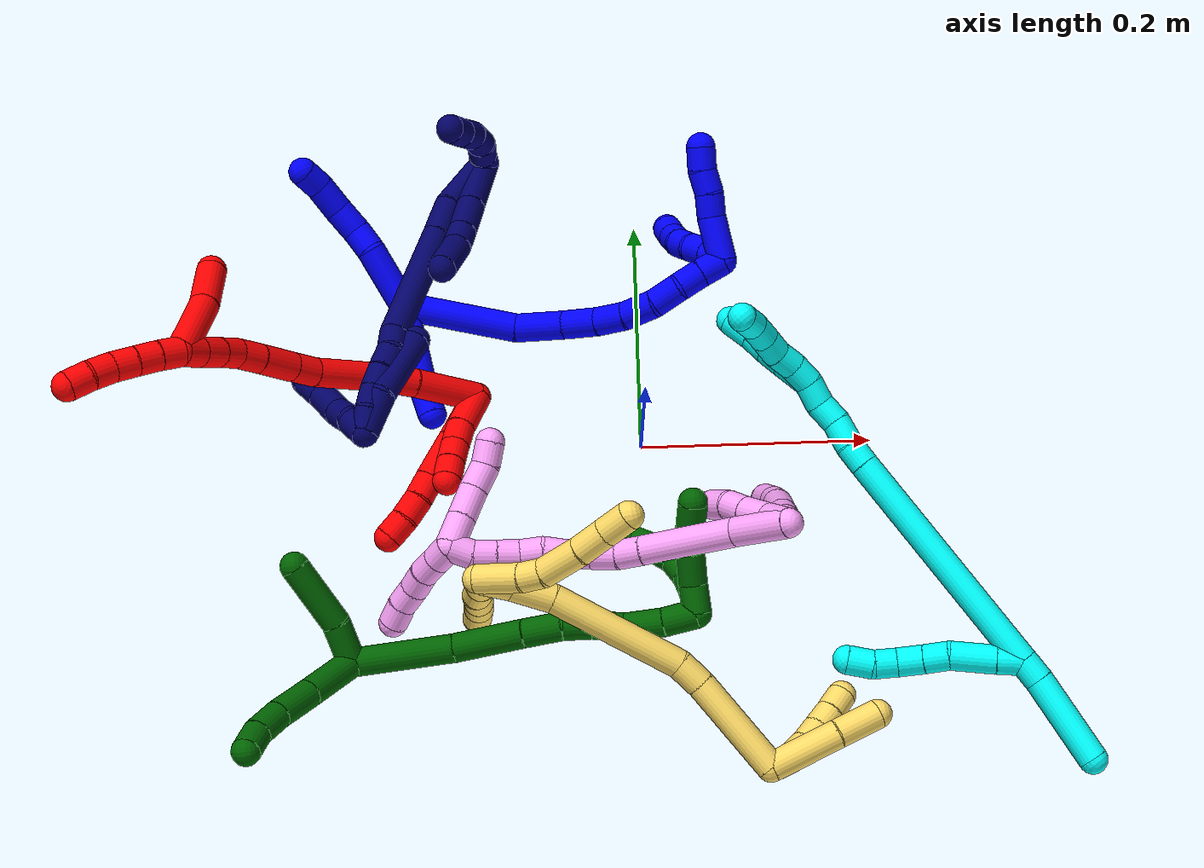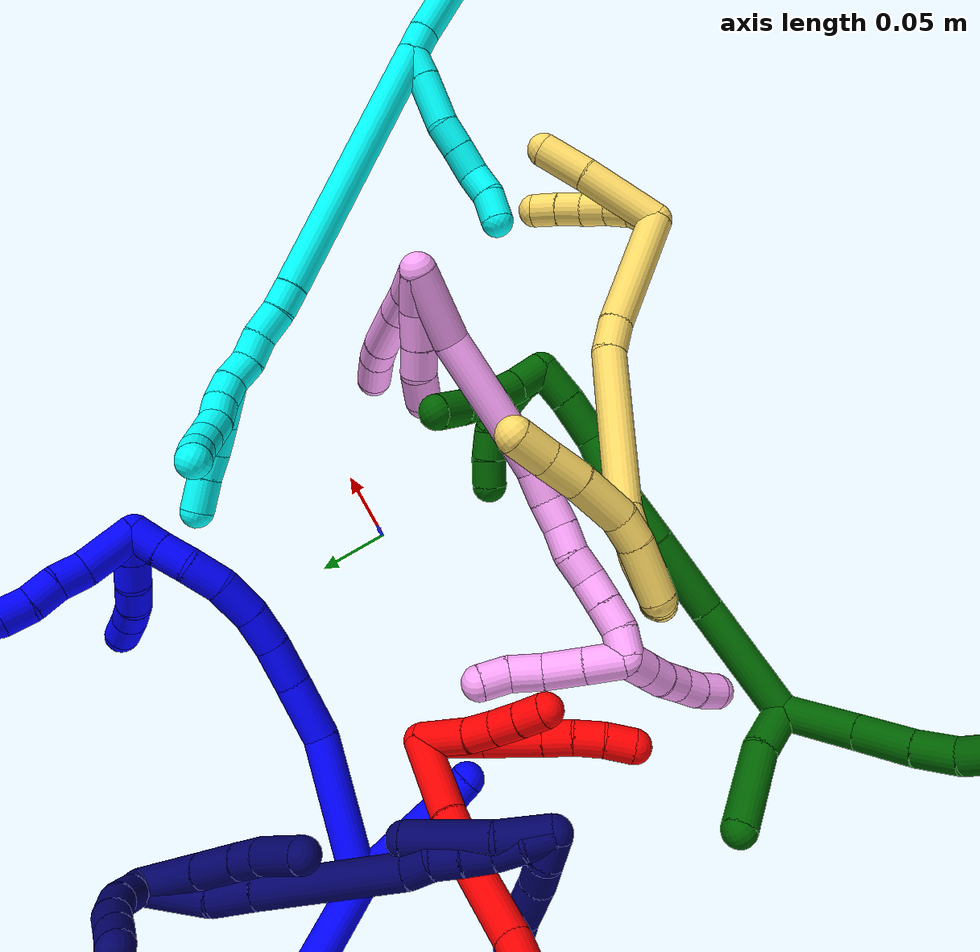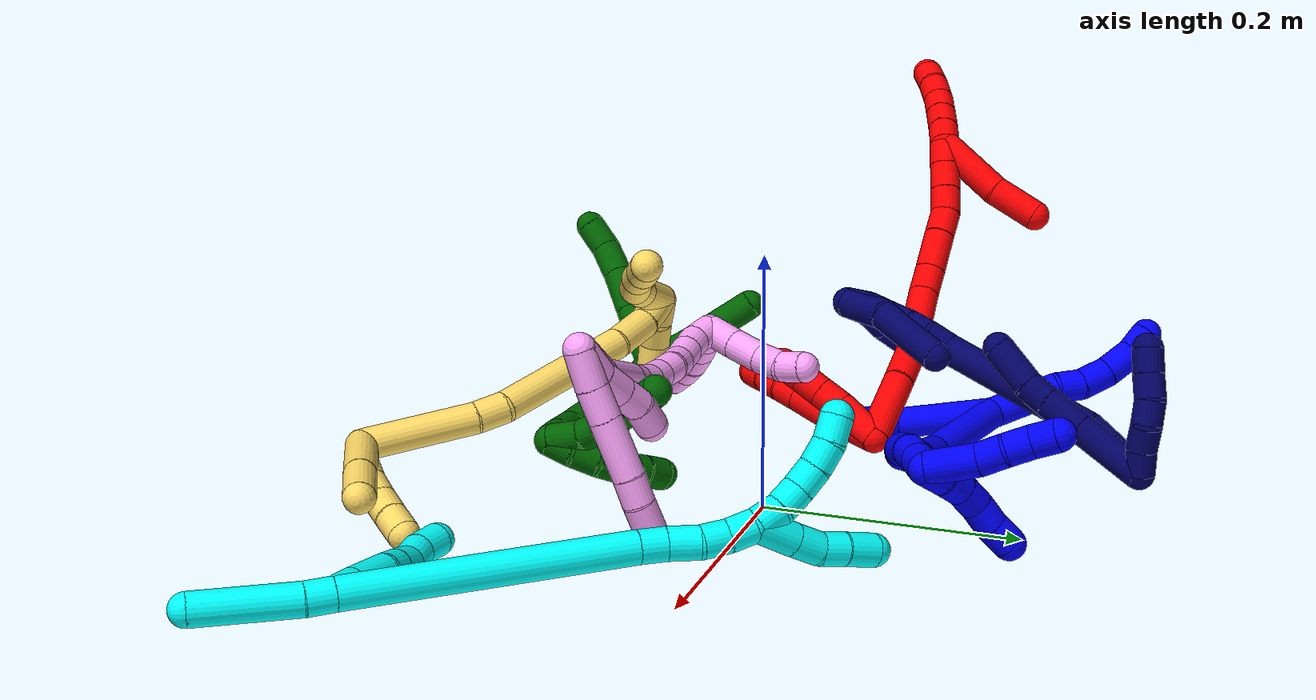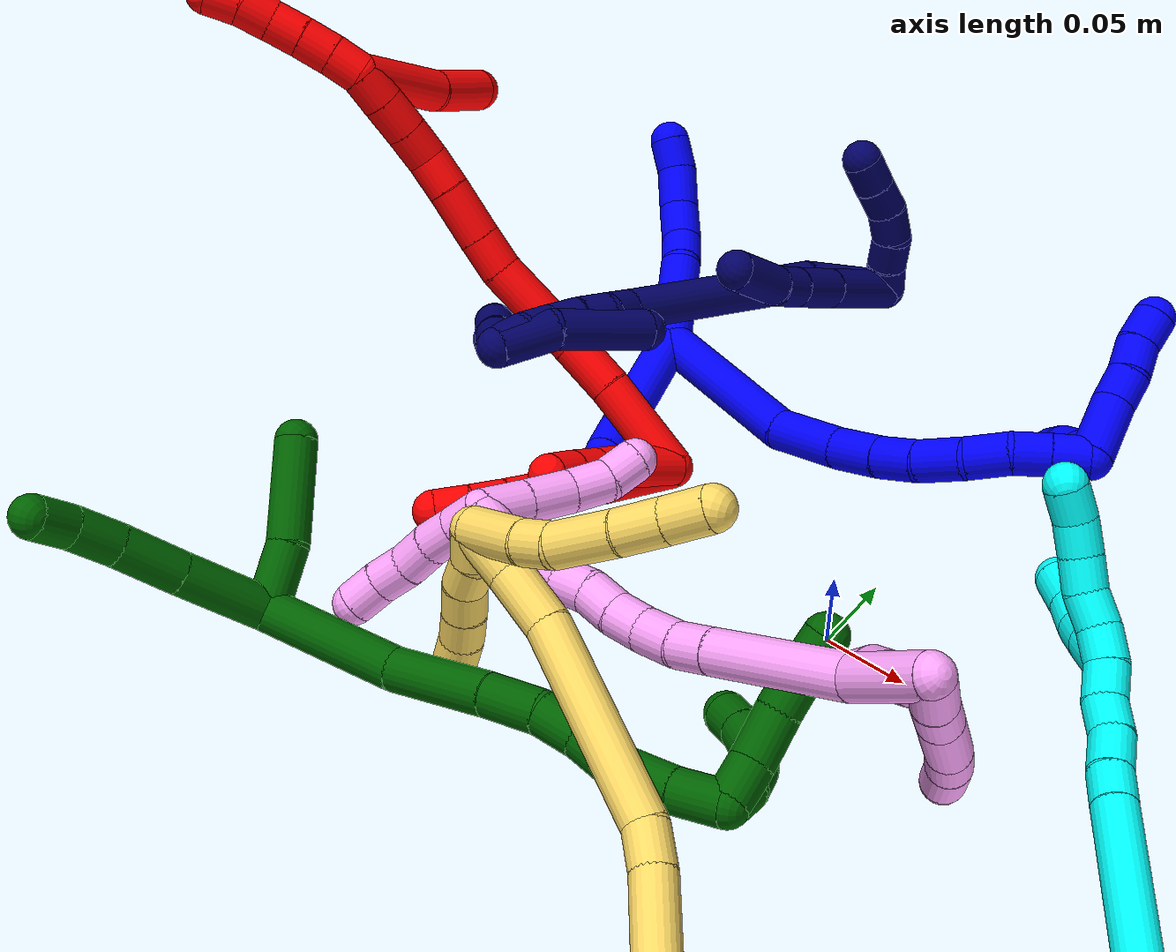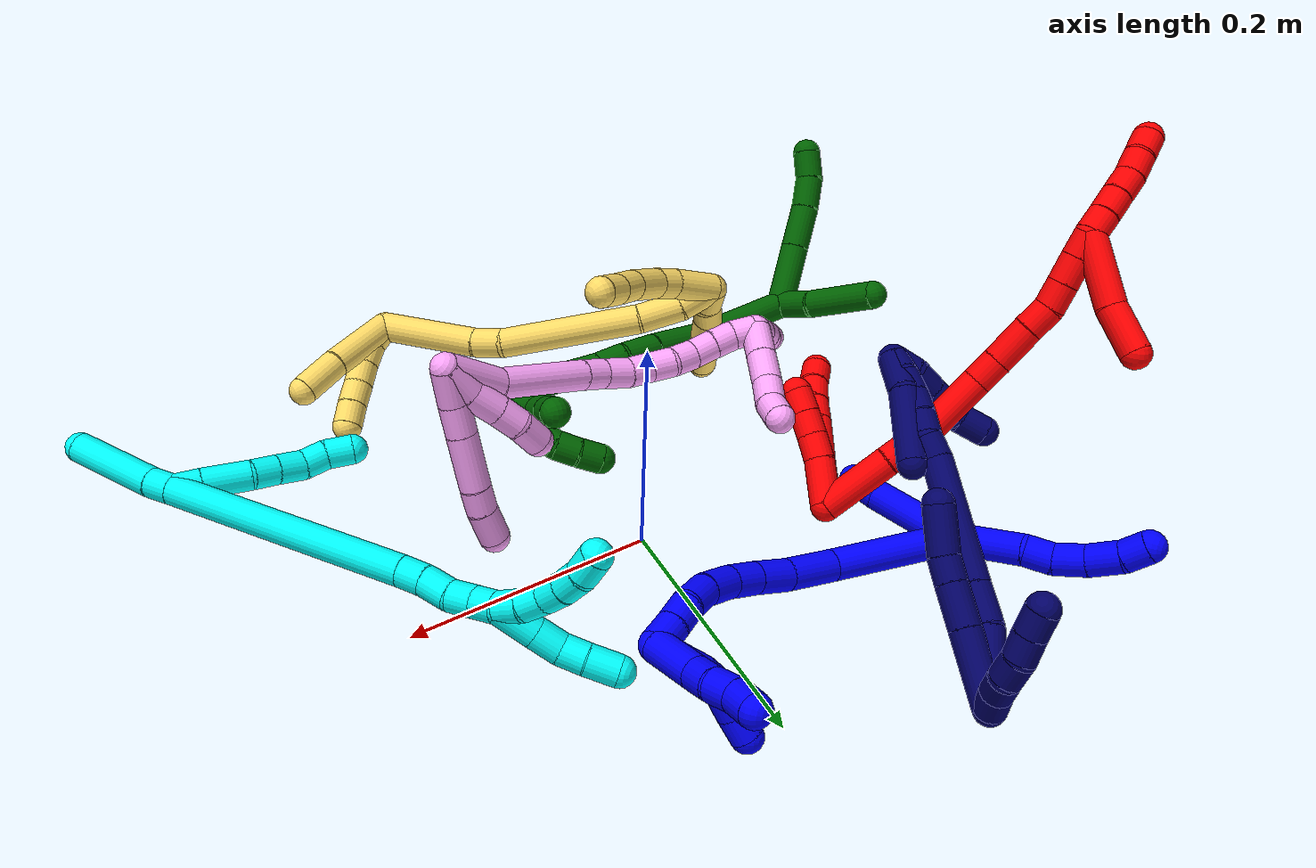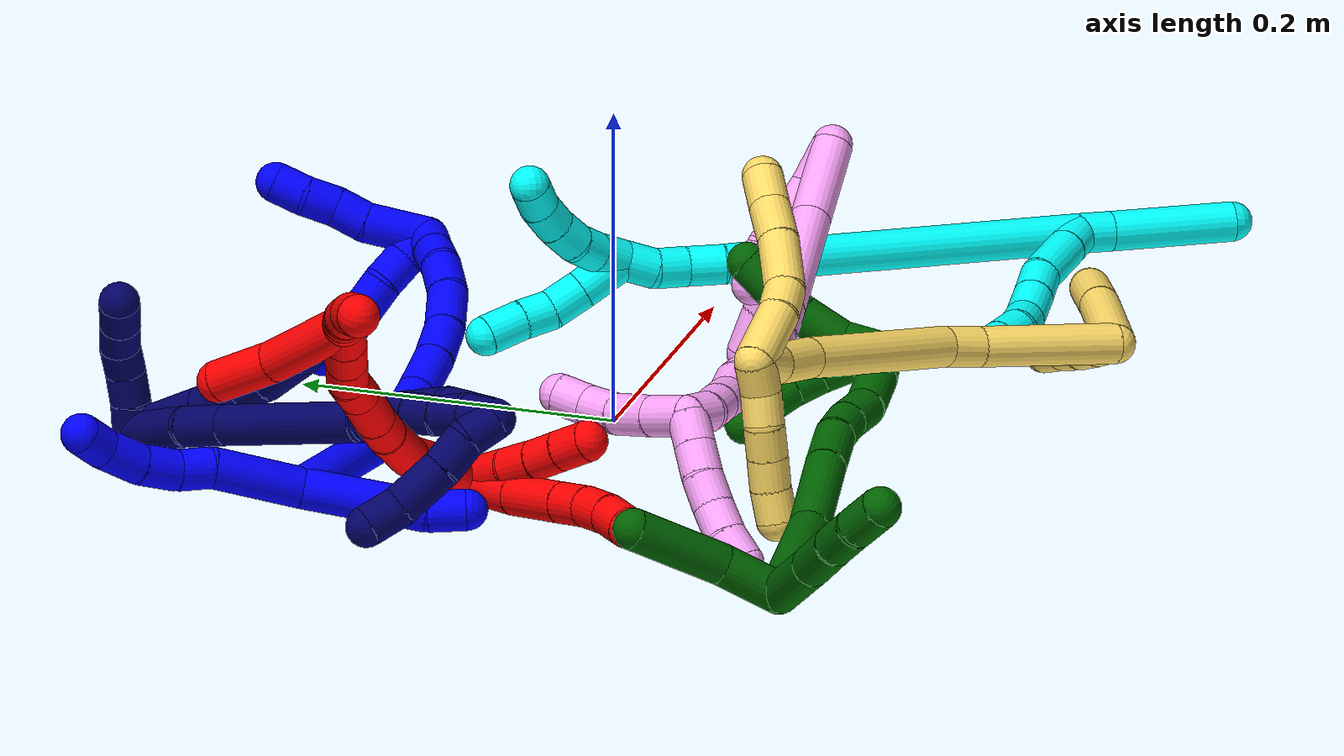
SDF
<sdf version="1.7">
 <world name="default">
  <plugin name="TubeGeneratorPlugin" filename="libtube_generator_plugin.so"/>
  <model name="photoneo_s_sensor">
   <static>1</static>
   <pose>0 0 2 1.57079 1.57079 3.14159</pose>
   <link name="link">
    <inertial><mass>0.1</mass></inertial>
    <sensor name="sensor" type="depth">
     <update_rate>30</update_rate>
     <camera>
      <horizontal_fov>1.22</horizontal_fov>
      <image><width>1920</width><height>1200</height><format>B8G8R8</format></image>
      <clip><near>0.1</near><far>4</far></clip>
      <depth_camera><output>points</output></depth_camera>
     </camera>
     <plugin name="camera_plugin" filename="libgazebo_ros_depth_camera.so">
      <baseline>0.2</baseline>
      <alwaysOn>1</alwaysOn>
      <updateRate>0.0</updateRate>
      <cameraName>camera_ir</cameraName>
      <imageTopicName>/camera/color/image_raw</imageTopicName>
      <cameraInfoTopicName>/camera/color/camera_info</cameraInfoTopicName>
      <depthImageTopicName>/camera/depth/image_raw</depthImageTopicName>
      <depthImageCameraInfoTopicName>/camera/depth/camera_info</depthImageCameraInfoTopicName>
      <pointCloudTopicName>/camera/depth/points</pointCloudTopicName>
      <frameName>fr_optical</frameName>
      <pointCloudCutoff>0.1</pointCloudCutoff>
      <pointCloudCutoffMax>2.0</pointCloudCutoffMax>
      <distortionK1>0</distortionK1>
      <distortionK2>0</distortionK2>
      <distortionK3>0</distortionK3>
      <distortionT1>0</distortionT1>
      <distortionT2>0</distortionT2>
      <CxPrime>0</CxPrime>
      <Cx>0</Cx>
      <Cy>0</Cy>
      <focalLength>0</focalLength>
      <hackBaseline>0</hackBaseline>
     </plugin>
    </sensor>
   </link>
  </model>
  <gravity>0 0 -9.8</gravity>
  <magnetic_field>6e-06 2.3e-05 -4.2e-05</magnetic_field>
  <atmosphere type="adiabatic"/>
  <physics name="default_physics" default="0" type="ode">
   <max_step_size>0.003</max_step_size>
   <real_time_factor>1</real_time_factor>
   <real_time_update_rate>1000</real_time_update_rate>
   <max_contacts>10000</max_contacts>
   <ode>
    <solver>
     <type>quick</type>
     <iters>100</iters>
     <sor>1.3</sor>
     <use_dynamic_moi_rescaling>0</use_dynamic_moi_rescaling>
    </solver>
    <constraints>
     <contact_max_correcting_vel>0</contact_max_correcting_vel>
     <contact_surface_layer>0.001</contact_surface_layer>
     <cfm>0</cfm>
     <erp>0.2</erp>
    </constraints>
   </ode>
  </physics>
  <scene><ambient>0.4 0.4 0.4 1</ambient><background>0.7 0.7 0.7 1</background><shadows>0</shadows></scene>
  <audio><device>default</device></audio>
  <spherical_coordinates>
   <surface_model>EARTH_WGS84</surface_model>
   <latitude_deg>0</latitude_deg>
   <longitude_deg>0</longitude_deg>
   <elevation>0</elevation>
   <heading_deg>0</heading_deg>
  </spherical_coordinates>
  <model name="bin">
   <static>1</static>
   <link name="bottom">
    <collision name="collision-bottom">
     <pose>0 0 -0.01 0 -0 0</pose>
     <geometry><box><size>0.8 0.6 0.02</size></box></geometry>
     <surface>
      <friction><ode><mu>100</mu><mu2>100</mu2></ode></friction>
      <contact><collide_bitmask>65535</collide_bitmask></contact>
     </surface>
    </collision>
   </link>
   <link name="west_wall">
    <collision name="collision-west_wall">
     <pose>-0.41 0 0.1 0 -0 0</pose>
     <geometry><box><size>0.02 0.6 0.2</size></box></geometry>
     <surface>
      <friction><ode><mu>100</mu><mu2>100</mu2></ode></friction>
      <contact><collide_bitmask>65535</collide_bitmask></contact>
     </surface>
    </collision>
   </link>
   <link name="east_wall">
    <collision name="collision-east_wall">
     <pose>0.41 0 0.1 0 -0 0</pose>
     <geometry><box><size>0.02 0.6 0.2</size></box></geometry>
     <surface>
      <friction><ode><mu>100</mu><mu2>100</mu2></ode></friction>
      <contact><collide_bitmask>65535</collide_bitmask></contact>
     </surface>
    </collision>
   </link>
   <link name="south_wall">
    <collision name="collision-south_wall">
     <pose>0 -0.31 0.1 0 -0 0</pose>
     <geometry><box><size>0.8 0.02 0.2</size></box></geometry>
     <surface>
      <friction><ode><mu>100</mu><mu2>100</mu2></ode></friction>
      <contact><collide_bitmask>65535</collide_bitmask></contact>
     </surface>
    </collision>
   </link>
   <link name="north_wall">
    <collision name="collision-north_wall">
     <pose>0 0.31 0.1 0 -0 0</pose>
     <geometry><box><size>0.8 0.02 0.2</size></box></geometry>
     <surface>
      <friction><ode><mu>100</mu><mu2>100</mu2></ode></friction>
      <contact><collide_bitmask>65535</collide_bitmask></contact>
     </surface>
    </collision>
   </link>
  </model>
  <model name="1">
   <static>0</static>
   <link name="1">
    <collision name="collision-cylinder-e_1_2_8">
     <pose>0.000116 -0.003127 0.028337 0.109904 0.004056 0.000223</pose>
     <geometry><cylinder><radius>0.0125</radius><length>0.057019</length></cylinder></geometry>
     <surface>
      <friction><ode><mu>1.16</mu><mu2>1.16</mu2><slip1>0</slip1><slip2>0</slip2></ode></friction>
      <contact><ode><kp>1e+06</kp><kd>1</kd><max_vel>0</max_vel><min_depth>0.001</min_depth></ode></contact>
     </surface>
    </collision>
    <visual name="visual-cylinder-e_1_2_8">
     <pose>0.000116 -0.003127 0.028337 0.109904 0.004056 0.000223</pose>
     <geometry><cylinder><radius>0.0125</radius><length>0.057019</length></cylinder></geometry>
     <material><ambient>0 0 1 1</ambient></material>
    </visual>
    <collision name="collision-cylinder-e_2_8_9">
     <pose>-0.002248 -0.005548 0.067047 -0.06798 -0.234077 0.007996</pose>
     <geometry><cylinder><radius>0.0125</radius><length>0.021377</length></cylinder></geometry>
     <surface>
      <friction><ode><mu>1.16</mu><mu2>1.16</mu2><slip1>0</slip1><slip2>0</slip2></ode></friction>
      <contact><ode><kp>1e+06</kp><kd>1</kd><max_vel>0</max_vel><min_depth>0.001</min_depth></ode></contact>
     </surface>
    </collision>
    <visual name="visual-cylinder-e_2_8_9">
     <pose>-0.002248 -0.005548 0.067047 -0.06798 -0.234077 0.007996</pose>
     <geometry><cylinder><radius>0.0125</radius><length>0.021377</length></cylinder></geometry>
     <material><ambient>0 0 1 1</ambient></material>
    </visual>
    <collision name="collision-cylinder-e_3_9_10">
     <pose>-0.006372 -0.007578 0.089479 0.223187 -0.132298 -0.014847</pose>
     <geometry><cylinder><radius>0.0125</radius><length>0.024949</length></cylinder></geometry>
     <surface>
      <friction><ode><mu>1.16</mu><mu2>1.16</mu2><slip1>0</slip1><slip2>0</slip2></ode></friction>
      <contact><ode><kp>1e+06</kp><kd>1</kd><max_vel>0</max_vel><min_depth>0.001</min_depth></ode></contact>
     </surface>
    </collision>
    <visual name="visual-cylinder-e_3_9_10">
     <pose>-0.006372 -0.007578 0.089479 0.223187 -0.132298 -0.014847</pose>
     <geometry><cylinder><radius>0.0125</radius><length>0.024949</length></cylinder></geometry>
     <material><ambient>0 0 1 1</ambient></material>
    </visual>
    <collision name="collision-cylinder-e_4_10_11">
     <pose>-0.007749 -0.015319 0.113801 0.387366 0.020342 0.00399</pose>
     <geometry><cylinder><radius>0.0125</radius><length>0.026495</length></cylinder></geometry>
     <surface>
      <friction><ode><mu>1.16</mu><mu2>1.16</mu2><slip1>0</slip1><slip2>0</slip2></ode></friction>
      <contact><ode><kp>1e+06</kp><kd>1</kd><max_vel>0</max_vel><min_depth>0.001</min_depth></ode></contact>
     </surface>
    </collision>
    <visual name="visual-cylinder-e_4_10_11">
     <pose>-0.007749 -0.015319 0.113801 0.387366 0.020342 0.00399</pose>
     <geometry><cylinder><radius>0.0125</radius><length>0.026495</length></cylinder></geometry>
     <material><ambient>0 0 1 1</ambient></material>
    </visual>
    <collision name="collision-cylinder-e_5_11_6">
     <pose>-0.00758 -0.026345 0.134146 0.640467 -0.010012 -0.00332</pose>
     <geometry><cylinder><radius>0.0125</radius><length>0.020161</length></cylinder></geometry>
     <surface>
      <friction><ode><mu>1.16</mu><mu2>1.16</mu2><slip1>0</slip1><slip2>0</slip2></ode></friction>
      <contact><ode><kp>1e+06</kp><kd>1</kd><max_vel>0</max_vel><min_depth>0.001</min_depth></ode></contact>
     </surface>
    </collision>
    <visual name="visual-cylinder-e_5_11_6">
     <pose>-0.00758 -0.026345 0.134146 0.640467 -0.010012 -0.00332</pose>
     <geometry><cylinder><radius>0.0125</radius><length>0.020161</length></cylinder></geometry>
     <material><ambient>0 0 1 1</ambient></material>
    </visual>
    <collision name="collision-cylinder-e_1_2_12">
     <pose>-0.006287 -0.007684 -0.036919 2.9364 -0.165208 -1.3545</pose>
     <geometry><cylinder><radius>0.0125</radius><length>0.07646</length></cylinder></geometry>
     <surface>
      <friction><ode><mu>1.16</mu><mu2>1.16</mu2><slip1>0</slip1><slip2>0</slip2></ode></friction>
      <contact><ode><kp>1e+06</kp><kd>1</kd><max_vel>0</max_vel><min_depth>0.001</min_depth></ode></contact>
     </surface>
    </collision>
    <visual name="visual-cylinder-e_1_2_12">
     <pose>-0.006287 -0.007684 -0.036919 2.9364 -0.165208 -1.3545</pose>
     <geometry><cylinder><radius>0.0125</radius><length>0.07646</length></cylinder></geometry>
     <material><ambient>0 0 1 1</ambient></material>
    </visual>
    <collision name="collision-cylinder-e_2_12_5">
     <pose>-0.012194 -0.019159 -0.084973 2.81345 0.032369 0.194907</pose>
     <geometry><cylinder><radius>0.0125</radius><length>0.02354</length></cylinder></geometry>
     <surface>
      <friction><ode><mu>1.16</mu><mu2>1.16</mu2><slip1>0</slip1><slip2>0</slip2></ode></friction>
      <contact><ode><kp>1e+06</kp><kd>1</kd><max_vel>0</max_vel><min_depth>0.001</min_depth></ode></contact>
     </surface>
    </collision>
    <visual name="visual-cylinder-e_2_12_5">
     <pose>-0.012194 -0.019159 -0.084973 2.81345 0.032369 0.194907</pose>
     <geometry><cylinder><radius>0.0125</radius><length>0.02354</length></cylinder></geometry>
     <material><ambient>0 0 1 1</ambient></material>
    </visual>
    <collision name="collision-cylinder-e_1_2_13">
     <pose>0.035361 0.017645 -0.031536 -2.63147 0.77455 -2.004</pose>
     <geometry><cylinder><radius>0.0125</radius><length>0.101119</length></cylinder></geometry>
     <surface>
      <friction><ode><mu>1.16</mu><mu2>1.16</mu2><slip1>0</slip1><slip2>0</slip2></ode></friction>
      <contact><ode><kp>1e+06</kp><kd>1</kd><max_vel>0</max_vel><min_depth>0.001</min_depth></ode></contact>
     </surface>
    </collision>
    <visual name="visual-cylinder-e_1_2_13">
     <pose>0.035361 0.017645 -0.031536 -2.63147 0.77455 -2.004</pose>
     <geometry><cylinder><radius>0.0125</radius><length>0.101119</length></cylinder></geometry>
     <material><ambient>0 0 1 1</ambient></material>
    </visual>
    <collision name="collision-cylinder-e_2_13_14">
     <pose>0.090005 0.040234 -0.071702 -2.62135 1.09457 -2.31802</pose>
     <geometry><cylinder><radius>0.0125</radius><length>0.043394</length></cylinder></geometry>
     <surface>
      <friction><ode><mu>1.16</mu><mu2>1.16</mu2><slip1>0</slip1><slip2>0</slip2></ode></friction>
      <contact><ode><kp>1e+06</kp><kd>1</kd><max_vel>0</max_vel><min_depth>0.001</min_depth></ode></contact>
     </surface>
    </collision>
    <visual name="visual-cylinder-e_2_13_14">
     <pose>0.090005 0.040234 -0.071702 -2.62135 1.09457 -2.31802</pose>
     <geometry><cylinder><radius>0.0125</radius><length>0.043394</length></cylinder></geometry>
     <material><ambient>0 0 1 1</ambient></material>
    </visual>
    <collision name="collision-cylinder-e_3_14_15">
     <pose>0.123573 0.047022 -0.085902 -2.822 1.18115 -2.66972</pose>
     <geometry><cylinder><radius>0.0125</radius><length>0.030886</length></cylinder></geometry>
     <surface>
      <friction><ode><mu>1.16</mu><mu2>1.16</mu2><slip1>0</slip1><slip2>0</slip2></ode></friction>
      <contact><ode><kp>1e+06</kp><kd>1</kd><max_vel>0</max_vel><min_depth>0.001</min_depth></ode></contact>
     </surface>
    </collision>
    <visual name="visual-cylinder-e_3_14_15">
     <pose>0.123573 0.047022 -0.085902 -2.822 1.18115 -2.66972</pose>
     <geometry><cylinder><radius>0.0125</radius><length>0.030886</length></cylinder></geometry>
     <material><ambient>0 0 1 1</ambient></material>
    </visual>
    <collision name="collision-cylinder-e_4_15_16">
     <pose>0.150436 0.050444 -0.094978 -2.71842 1.27405 -2.57652</pose>
     <geometry><cylinder><radius>0.0125</radius><length>0.026306</length></cylinder></geometry>
     <surface>
      <friction><ode><mu>1.16</mu><mu2>1.16</mu2><slip1>0</slip1><slip2>0</slip2></ode></friction>
      <contact><ode><kp>1e+06</kp><kd>1</kd><max_vel>0</max_vel><min_depth>0.001</min_depth></ode></contact>
     </surface>
    </collision>
    <visual name="visual-cylinder-e_4_15_16">
     <pose>0.150436 0.050444 -0.094978 -2.71842 1.27405 -2.57652</pose>
     <geometry><cylinder><radius>0.0125</radius><length>0.026306</length></cylinder></geometry>
     <material><ambient>0 0 1 1</ambient></material>
    </visual>
    <collision name="collision-cylinder-e_5_16_17">
     <pose>0.177363 0.054206 -0.099742 -2.09346 1.39701 -1.93596</pose>
     <geometry><cylinder><radius>0.0125</radius><length>0.029136</length></cylinder></geometry>
     <surface>
      <friction><ode><mu>1.16</mu><mu2>1.16</mu2><slip1>0</slip1><slip2>0</slip2></ode></friction>
      <contact><ode><kp>1e+06</kp><kd>1</kd><max_vel>0</max_vel><min_depth>0.001</min_depth></ode></contact>
     </surface>
    </collision>
    <visual name="visual-cylinder-e_5_16_17">
     <pose>0.177363 0.054206 -0.099742 -2.09346 1.39701 -1.93596</pose>
     <geometry><cylinder><radius>0.0125</radius><length>0.029136</length></cylinder></geometry>
     <material><ambient>0 0 1 1</ambient></material>
    </visual>
    <collision name="collision-cylinder-e_6_17_18">
     <pose>0.203876 0.060603 -0.099667 -1.26456 1.2223 -0.948444</pose>
     <geometry><cylinder><radius>0.0125</radius><length>0.025885</length></cylinder></geometry>
     <surface>
      <friction><ode><mu>1.16</mu><mu2>1.16</mu2><slip1>0</slip1><slip2>0</slip2></ode></friction>
      <contact><ode><kp>1e+06</kp><kd>1</kd><max_vel>0</max_vel><min_depth>0.001</min_depth></ode></contact>
     </surface>
    </collision>
    <visual name="visual-cylinder-e_6_17_18">
     <pose>0.203876 0.060603 -0.099667 -1.26456 1.2223 -0.948444</pose>
     <geometry><cylinder><radius>0.0125</radius><length>0.025885</length></cylinder></geometry>
     <material><ambient>0 0 1 1</ambient></material>
    </visual>
    <collision name="collision-cylinder-e_7_18_19">
     <pose>0.224932 0.070893 -0.097374 -1.41393 0.965619 -0.842037</pose>
     <geometry><cylinder><radius>0.0125</radius><length>0.021624</length></cylinder></geometry>
     <surface>
      <friction><ode><mu>1.16</mu><mu2>1.16</mu2><slip1>0</slip1><slip2>0</slip2></ode></friction>
      <contact><ode><kp>1e+06</kp><kd>1</kd><max_vel>0</max_vel><min_depth>0.001</min_depth></ode></contact>
     </surface>
    </collision>
    <visual name="visual-cylinder-e_7_18_19">
     <pose>0.224932 0.070893 -0.097374 -1.41393 0.965619 -0.842037</pose>
     <geometry><cylinder><radius>0.0125</radius><length>0.021624</length></cylinder></geometry>
     <material><ambient>0 0 1 1</ambient></material>
    </visual>
    <collision name="collision-cylinder-e_8_19_1">
     <pose>0.242823 0.082972 -0.096028 -1.50679 0.981498 -0.929208</pose>
     <geometry><cylinder><radius>0.0125</radius><length>0.021651</length></cylinder></geometry>
     <surface>
      <friction><ode><mu>1.16</mu><mu2>1.16</mu2><slip1>0</slip1><slip2>0</slip2></ode></friction>
      <contact><ode><kp>1e+06</kp><kd>1</kd><max_vel>0</max_vel><min_depth>0.001</min_depth></ode></contact>
     </surface>
    </collision>
    <visual name="visual-cylinder-e_8_19_1">
     <pose>0.242823 0.082972 -0.096028 -1.50679 0.981498 -0.929208</pose>
     <geometry><cylinder><radius>0.0125</radius><length>0.021651</length></cylinder></geometry>
     <material><ambient>0 0 1 1</ambient></material>
    </visual>
    <collision name="collision-cylinder-e_1_1_20">
     <pose>0.255507 0.091993 -0.07668 -0.15775 0.189577 -0.015029</pose>
     <geometry><cylinder><radius>0.0125</radius><length>0.039104</length></cylinder></geometry>
     <surface>
      <friction><ode><mu>1.16</mu><mu2>1.16</mu2><slip1>0</slip1><slip2>0</slip2></ode></friction>
      <contact><ode><kp>1e+06</kp><kd>1</kd><max_vel>0</max_vel><min_depth>0.001</min_depth></ode></contact>
     </surface>
    </collision>
    <visual name="visual-cylinder-e_1_1_20">
     <pose>0.255507 0.091993 -0.07668 -0.15775 0.189577 -0.015029</pose>
     <geometry><cylinder><radius>0.0125</radius><length>0.039104</length></cylinder></geometry>
     <material><ambient>0 0 1 1</ambient></material>
    </visual>
    <collision name="collision-cylinder-e_2_20_21">
     <pose>0.263395 0.095235 -0.048204 -0.023659 0.415966 -0.004993</pose>
     <geometry><cylinder><radius>0.0125</radius><length>0.020804</length></cylinder></geometry>
     <surface>
      <friction><ode><mu>1.16</mu><mu2>1.16</mu2><slip1>0</slip1><slip2>0</slip2></ode></friction>
      <contact><ode><kp>1e+06</kp><kd>1</kd><max_vel>0</max_vel><min_depth>0.001</min_depth></ode></contact>
     </surface>
    </collision>
    <visual name="visual-cylinder-e_2_20_21">
     <pose>0.263395 0.095235 -0.048204 -0.023659 0.415966 -0.004993</pose>
     <geometry><cylinder><radius>0.0125</radius><length>0.020804</length></cylinder></geometry>
     <material><ambient>0 0 1 1</ambient></material>
    </visual>
    <collision name="collision-cylinder-e_3_21_22">
     <pose>0.269591 0.095481 -0.028857 -0.002185 0.1999 -0.000219</pose>
     <geometry><cylinder><radius>0.0125</radius><length>0.020069</length></cylinder></geometry>
     <surface>
      <friction><ode><mu>1.16</mu><mu2>1.16</mu2><slip1>0</slip1><slip2>0</slip2></ode></friction>
      <contact><ode><kp>1e+06</kp><kd>1</kd><max_vel>0</max_vel><min_depth>0.001</min_depth></ode></contact>
     </surface>
    </collision>
    <visual name="visual-cylinder-e_3_21_22">
     <pose>0.269591 0.095481 -0.028857 -0.002185 0.1999 -0.000219</pose>
     <geometry><cylinder><radius>0.0125</radius><length>0.020069</length></cylinder></geometry>
     <material><ambient>0 0 1 1</ambient></material>
    </visual>
    <collision name="collision-cylinder-e_4_22_4">
     <pose>0.27561 0.096577 -0.00992 -0.117534 0.413981 -0.024709</pose>
     <geometry><cylinder><radius>0.0125</radius><length>0.020023</length></cylinder></geometry>
     <surface>
      <friction><ode><mu>1.16</mu><mu2>1.16</mu2><slip1>0</slip1><slip2>0</slip2></ode></friction>
      <contact><ode><kp>1e+06</kp><kd>1</kd><max_vel>0</max_vel><min_depth>0.001</min_depth></ode></contact>
     </surface>
    </collision>
    <visual name="visual-cylinder-e_4_22_4">
     <pose>0.27561 0.096577 -0.00992 -0.117534 0.413981 -0.024709</pose>
     <geometry><cylinder><radius>0.0125</radius><length>0.020023</length></cylinder></geometry>
     <material><ambient>0 0 1 1</ambient></material>
    </visual>
    <collision name="collision-cylinder-e_1_1_23">
     <pose>0.245299 0.09308 -0.089271 -0.572122 -0.710684 0.217438</pose>
     <geometry><cylinder><radius>0.0125</radius><length>0.02</length></cylinder></geometry>
     <surface>
      <friction><ode><mu>1.16</mu><mu2>1.16</mu2><slip1>0</slip1><slip2>0</slip2></ode></friction>
      <contact><ode><kp>1e+06</kp><kd>1</kd><max_vel>0</max_vel><min_depth>0.001</min_depth></ode></contact>
     </surface>
    </collision>
    <visual name="visual-cylinder-e_1_1_23">
     <pose>0.245299 0.09308 -0.089271 -0.572122 -0.710684 0.217438</pose>
     <geometry><cylinder><radius>0.0125</radius><length>0.02</length></cylinder></geometry>
     <material><ambient>0 0 1 1</ambient></material>
    </visual>
    <collision name="collision-cylinder-e_2_23_24">
     <pose>0.231265 0.100611 -0.077256 -0.545897 -0.84972 0.251952</pose>
     <geometry><cylinder><radius>0.0125</radius><length>0.02</length></cylinder></geometry>
     <surface>
      <friction><ode><mu>1.16</mu><mu2>1.16</mu2><slip1>0</slip1><slip2>0</slip2></ode></friction>
      <contact><ode><kp>1e+06</kp><kd>1</kd><max_vel>0</max_vel><min_depth>0.001</min_depth></ode></contact>
     </surface>
    </collision>
    <visual name="visual-cylinder-e_2_23_24">
     <pose>0.231265 0.100611 -0.077256 -0.545897 -0.84972 0.251952</pose>
     <geometry><cylinder><radius>0.0125</radius><length>0.02</length></cylinder></geometry>
     <material><ambient>0 0 1 1</ambient></material>
    </visual>
    <collision name="collision-cylinder-e_3_24_25">
     <pose>0.216749 0.109592 -0.067132 -0.89171 -0.776144 0.385915</pose>
     <geometry><cylinder><radius>0.0125</radius><length>0.02</length></cylinder></geometry>
     <surface>
      <friction><ode><mu>1.16</mu><mu2>1.16</mu2><slip1>0</slip1><slip2>0</slip2></ode></friction>
      <contact><ode><kp>1e+06</kp><kd>1</kd><max_vel>0</max_vel><min_depth>0.001</min_depth></ode></contact>
     </surface>
    </collision>
    <visual name="visual-cylinder-e_3_24_25">
     <pose>0.216749 0.109592 -0.067132 -0.89171 -0.776144 0.385915</pose>
     <geometry><cylinder><radius>0.0125</radius><length>0.02</length></cylinder></geometry>
     <material><ambient>0 0 1 1</ambient></material>
    </visual>
    <collision name="collision-cylinder-e_4_25_26">
     <pose>0.204679 0.122888 -0.058855 -1.11515 -0.531017 0.335943</pose>
     <geometry><cylinder><radius>0.0125</radius><length>0.02</length></cylinder></geometry>
     <surface>
      <friction><ode><mu>1.16</mu><mu2>1.16</mu2><slip1>0</slip1><slip2>0</slip2></ode></friction>
      <contact><ode><kp>1e+06</kp><kd>1</kd><max_vel>0</max_vel><min_depth>0.001</min_depth></ode></contact>
     </surface>
    </collision>
    <visual name="visual-cylinder-e_4_25_26">
     <pose>0.204679 0.122888 -0.058855 -1.11515 -0.531017 0.335943</pose>
     <geometry><cylinder><radius>0.0125</radius><length>0.02</length></cylinder></geometry>
     <material><ambient>0 0 1 1</ambient></material>
    </visual>
    <collision name="collision-cylinder-e_5_26_3">
     <pose>0.195243 0.138125 -0.050088 -0.984932 -0.452529 0.245794</pose>
     <geometry><cylinder><radius>0.0125</radius><length>0.02</length></cylinder></geometry>
     <surface>
      <friction><ode><mu>1.16</mu><mu2>1.16</mu2><slip1>0</slip1><slip2>0</slip2></ode></friction>
      <contact><ode><kp>1e+06</kp><kd>1</kd><max_vel>0</max_vel><min_depth>0.001</min_depth></ode></contact>
     </surface>
    </collision>
    <visual name="visual-cylinder-e_5_26_3">
     <pose>0.195243 0.138125 -0.050088 -0.984932 -0.452529 0.245794</pose>
     <geometry><cylinder><radius>0.0125</radius><length>0.02</length></cylinder></geometry>
     <material><ambient>0 0 1 1</ambient></material>
    </visual>
    <collision name="collision-sphere-3">
     <pose>0.19087 0.145618 -0.045115 0 -0 0</pose>
     <geometry><sphere><radius>0.0125</radius></sphere></geometry>
     <surface>
      <friction><ode><mu>1.16</mu><mu2>1.16</mu2><slip1>0</slip1><slip2>0</slip2></ode></friction>
      <contact><ode><kp>1e+06</kp><kd>1</kd><max_vel>0</max_vel><min_depth>0.001</min_depth></ode></contact>
     </surface>
    </collision>
    <visual name="visual-sphere-3">
     <pose>0.19087 0.145618 -0.045115 0 -0 0</pose>
     <geometry><sphere><radius>0.0125</radius></sphere></geometry>
     <material><ambient>0 0 1 1</ambient></material>
    </visual>
    <collision name="collision-sphere-26">
     <pose>0.199615 0.130631 -0.055061 0 -0 0</pose>
     <geometry><sphere><radius>0.0125</radius></sphere></geometry>
     <surface>
      <friction><ode><mu>1.16</mu><mu2>1.16</mu2><slip1>0</slip1><slip2>0</slip2></ode></friction>
      <contact><ode><kp>1e+06</kp><kd>1</kd><max_vel>0</max_vel><min_depth>0.001</min_depth></ode></contact>
     </surface>
    </collision>
    <visual name="visual-sphere-26">
     <pose>0.199615 0.130631 -0.055061 0 -0 0</pose>
     <geometry><sphere><radius>0.0125</radius></sphere></geometry>
     <material><ambient>0 0 1 1</ambient></material>
    </visual>
    <collision name="collision-sphere-25">
     <pose>0.209743 0.115145 -0.062649 0 -0 0</pose>
     <geometry><sphere><radius>0.0125</radius></sphere></geometry>
     <surface>
      <friction><ode><mu>1.16</mu><mu2>1.16</mu2><slip1>0</slip1><slip2>0</slip2></ode></friction>
      <contact><ode><kp>1e+06</kp><kd>1</kd><max_vel>0</max_vel><min_depth>0.001</min_depth></ode></contact>
     </surface>
    </collision>
    <visual name="visual-sphere-25">
     <pose>0.209743 0.115145 -0.062649 0 -0 0</pose>
     <geometry><sphere><radius>0.0125</radius></sphere></geometry>
     <material><ambient>0 0 1 1</ambient></material>
    </visual>
    <collision name="collision-sphere-24">
     <pose>0.223754 0.104039 -0.071614 0 -0 0</pose>
     <geometry><sphere><radius>0.0125</radius></sphere></geometry>
     <surface>
      <friction><ode><mu>1.16</mu><mu2>1.16</mu2><slip1>0</slip1><slip2>0</slip2></ode></friction>
      <contact><ode><kp>1e+06</kp><kd>1</kd><max_vel>0</max_vel><min_depth>0.001</min_depth></ode></contact>
     </surface>
    </collision>
    <visual name="visual-sphere-24">
     <pose>0.223754 0.104039 -0.071614 0 -0 0</pose>
     <geometry><sphere><radius>0.0125</radius></sphere></geometry>
     <material><ambient>0 0 1 1</ambient></material>
    </visual>
    <collision name="collision-sphere-23">
     <pose>0.238776 0.097183 -0.082899 0 -0 0</pose>
     <geometry><sphere><radius>0.0125</radius></sphere></geometry>
     <surface>
      <friction><ode><mu>1.16</mu><mu2>1.16</mu2><slip1>0</slip1><slip2>0</slip2></ode></friction>
      <contact><ode><kp>1e+06</kp><kd>1</kd><max_vel>0</max_vel><min_depth>0.001</min_depth></ode></contact>
     </surface>
    </collision>
    <visual name="visual-sphere-23">
     <pose>0.238776 0.097183 -0.082899 0 -0 0</pose>
     <geometry><sphere><radius>0.0125</radius></sphere></geometry>
     <material><ambient>0 0 1 1</ambient></material>
    </visual>
    <collision name="collision-sphere-4">
     <pose>0.279638 0.097652 -0.000817 0 -0 0</pose>
     <geometry><sphere><radius>0.0125</radius></sphere></geometry>
     <surface>
      <friction><ode><mu>1.16</mu><mu2>1.16</mu2><slip1>0</slip1><slip2>0</slip2></ode></friction>
      <contact><ode><kp>1e+06</kp><kd>1</kd><max_vel>0</max_vel><min_depth>0.001</min_depth></ode></contact>
     </surface>
    </collision>
    <visual name="visual-sphere-4">
     <pose>0.279638 0.097652 -0.000817 0 -0 0</pose>
     <geometry><sphere><radius>0.0125</radius></sphere></geometry>
     <material><ambient>0 0 1 1</ambient></material>
    </visual>
    <collision name="collision-sphere-22">
     <pose>0.271583 0.095503 -0.019023 0 -0 0</pose>
     <geometry><sphere><radius>0.0125</radius></sphere></geometry>
     <surface>
      <friction><ode><mu>1.16</mu><mu2>1.16</mu2><slip1>0</slip1><slip2>0</slip2></ode></friction>
      <contact><ode><kp>1e+06</kp><kd>1</kd><max_vel>0</max_vel><min_depth>0.001</min_depth></ode></contact>
     </surface>
    </collision>
    <visual name="visual-sphere-22">
     <pose>0.271583 0.095503 -0.019023 0 -0 0</pose>
     <geometry><sphere><radius>0.0125</radius></sphere></geometry>
     <material><ambient>0 0 1 1</ambient></material>
    </visual>
    <collision name="collision-sphere-21">
     <pose>0.267598 0.09546 -0.038692 0 -0 0</pose>
     <geometry><sphere><radius>0.0125</radius></sphere></geometry>
     <surface>
      <friction><ode><mu>1.16</mu><mu2>1.16</mu2><slip1>0</slip1><slip2>0</slip2></ode></friction>
      <contact><ode><kp>1e+06</kp><kd>1</kd><max_vel>0</max_vel><min_depth>0.001</min_depth></ode></contact>
     </surface>
    </collision>
    <visual name="visual-sphere-21">
     <pose>0.267598 0.09546 -0.038692 0 -0 0</pose>
     <geometry><sphere><radius>0.0125</radius></sphere></geometry>
     <material><ambient>0 0 1 1</ambient></material>
    </visual>
    <collision name="collision-sphere-20">
     <pose>0.259192 0.095009 -0.057716 0 -0 0</pose>
     <geometry><sphere><radius>0.0125</radius></sphere></geometry>
     <surface>
      <friction><ode><mu>1.16</mu><mu2>1.16</mu2><slip1>0</slip1><slip2>0</slip2></ode></friction>
      <contact><ode><kp>1e+06</kp><kd>1</kd><max_vel>0</max_vel><min_depth>0.001</min_depth></ode></contact>
     </surface>
    </collision>
    <visual name="visual-sphere-20">
     <pose>0.259192 0.095009 -0.057716 0 -0 0</pose>
     <geometry><sphere><radius>0.0125</radius></sphere></geometry>
     <material><ambient>0 0 1 1</ambient></material>
    </visual>
    <collision name="collision-sphere-6">
     <pose>-0.007681 -0.032369 0.142229 0 -0 0</pose>
     <geometry><sphere><radius>0.0125</radius></sphere></geometry>
     <surface>
      <friction><ode><mu>1.16</mu><mu2>1.16</mu2><slip1>0</slip1><slip2>0</slip2></ode></friction>
      <contact><ode><kp>1e+06</kp><kd>1</kd><max_vel>0</max_vel><min_depth>0.001</min_depth></ode></contact>
     </surface>
    </collision>
    <visual name="visual-sphere-6">
     <pose>-0.007681 -0.032369 0.142229 0 -0 0</pose>
     <geometry><sphere><radius>0.0125</radius></sphere></geometry>
     <material><ambient>0 0 1 1</ambient></material>
    </visual>
    <collision name="collision-sphere-11">
     <pose>-0.007479 -0.020322 0.126064 0 -0 0</pose>
     <geometry><sphere><radius>0.0125</radius></sphere></geometry>
     <surface>
      <friction><ode><mu>1.16</mu><mu2>1.16</mu2><slip1>0</slip1><slip2>0</slip2></ode></friction>
      <contact><ode><kp>1e+06</kp><kd>1</kd><max_vel>0</max_vel><min_depth>0.001</min_depth></ode></contact>
     </surface>
    </collision>
    <visual name="visual-sphere-11">
     <pose>-0.007479 -0.020322 0.126064 0 -0 0</pose>
     <geometry><sphere><radius>0.0125</radius></sphere></geometry>
     <material><ambient>0 0 1 1</ambient></material>
    </visual>
    <collision name="collision-sphere-10">
     <pose>-0.008018 -0.010315 0.101537 0 -0 0</pose>
     <geometry><sphere><radius>0.0125</radius></sphere></geometry>
     <surface>
      <friction><ode><mu>1.16</mu><mu2>1.16</mu2><slip1>0</slip1><slip2>0</slip2></ode></friction>
      <contact><ode><kp>1e+06</kp><kd>1</kd><max_vel>0</max_vel><min_depth>0.001</min_depth></ode></contact>
     </surface>
    </collision>
    <visual name="visual-sphere-10">
     <pose>-0.008018 -0.010315 0.101537 0 -0 0</pose>
     <geometry><sphere><radius>0.0125</radius></sphere></geometry>
     <material><ambient>0 0 1 1</ambient></material>
    </visual>
    <collision name="collision-sphere-9">
     <pose>-0.004727 -0.004841 0.07742 0 -0 0</pose>
     <geometry><sphere><radius>0.0125</radius></sphere></geometry>
     <surface>
      <friction><ode><mu>1.16</mu><mu2>1.16</mu2><slip1>0</slip1><slip2>0</slip2></ode></friction>
      <contact><ode><kp>1e+06</kp><kd>1</kd><max_vel>0</max_vel><min_depth>0.001</min_depth></ode></contact>
     </surface>
    </collision>
    <visual name="visual-sphere-9">
     <pose>-0.004727 -0.004841 0.07742 0 -0 0</pose>
     <geometry><sphere><radius>0.0125</radius></sphere></geometry>
     <material><ambient>0 0 1 1</ambient></material>
    </visual>
    <collision name="collision-sphere-2">
     <geometry><sphere><radius>0.0125</radius></sphere></geometry>
     <surface>
      <friction><ode><mu>1.16</mu><mu2>1.16</mu2><slip1>0</slip1><slip2>0</slip2></ode></friction>
      <contact><ode><kp>1e+06</kp><kd>1</kd><max_vel>0</max_vel><min_depth>0.001</min_depth></ode></contact>
     </surface>
    </collision>
    <visual name="visual-sphere-2">
     <geometry><sphere><radius>0.0125</radius></sphere></geometry>
     <material><ambient>0 0 1 1</ambient></material>
    </visual>
    <collision name="collision-sphere-19">
     <pose>0.233824 0.076968 -0.096413 0 -0 0</pose>
     <geometry><sphere><radius>0.0125</radius></sphere></geometry>
     <surface>
      <friction><ode><mu>1.16</mu><mu2>1.16</mu2><slip1>0</slip1><slip2>0</slip2></ode></friction>
      <contact><ode><kp>1e+06</kp><kd>1</kd><max_vel>0</max_vel><min_depth>0.001</min_depth></ode></contact>
     </surface>
    </collision>
    <visual name="visual-sphere-19">
     <pose>0.233824 0.076968 -0.096413 0 -0 0</pose>
     <geometry><sphere><radius>0.0125</radius></sphere></geometry>
     <material><ambient>0 0 1 1</ambient></material>
    </visual>
    <collision name="collision-sphere-8">
     <pose>0.000231 -0.006254 0.056674 0 -0 0</pose>
     <geometry><sphere><radius>0.0125</radius></sphere></geometry>
     <surface>
      <friction><ode><mu>1.16</mu><mu2>1.16</mu2><slip1>0</slip1><slip2>0</slip2></ode></friction>
      <contact><ode><kp>1e+06</kp><kd>1</kd><max_vel>0</max_vel><min_depth>0.001</min_depth></ode></contact>
     </surface>
    </collision>
    <visual name="visual-sphere-8">
     <pose>0.000231 -0.006254 0.056674 0 -0 0</pose>
     <geometry><sphere><radius>0.0125</radius></sphere></geometry>
     <material><ambient>0 0 1 1</ambient></material>
    </visual>
    <collision name="collision-sphere-12">
     <pose>-0.012575 -0.015367 -0.073837 0 -0 0</pose>
     <geometry><sphere><radius>0.0125</radius></sphere></geometry>
     <surface>
      <friction><ode><mu>1.16</mu><mu2>1.16</mu2><slip1>0</slip1><slip2>0</slip2></ode></friction>
      <contact><ode><kp>1e+06</kp><kd>1</kd><max_vel>0</max_vel><min_depth>0.001</min_depth></ode></contact>
     </surface>
    </collision>
    <visual name="visual-sphere-12">
     <pose>-0.012575 -0.015367 -0.073837 0 -0 0</pose>
     <geometry><sphere><radius>0.0125</radius></sphere></geometry>
     <material><ambient>0 0 1 1</ambient></material>
    </visual>
    <collision name="collision-sphere-5">
     <pose>-0.011813 -0.02295 -0.096109 0 -0 0</pose>
     <geometry><sphere><radius>0.0125</radius></sphere></geometry>
     <surface>
      <friction><ode><mu>1.16</mu><mu2>1.16</mu2><slip1>0</slip1><slip2>0</slip2></ode></friction>
      <contact><ode><kp>1e+06</kp><kd>1</kd><max_vel>0</max_vel><min_depth>0.001</min_depth></ode></contact>
     </surface>
    </collision>
    <visual name="visual-sphere-5">
     <pose>-0.011813 -0.02295 -0.096109 0 -0 0</pose>
     <geometry><sphere><radius>0.0125</radius></sphere></geometry>
     <material><ambient>0 0 1 1</ambient></material>
    </visual>
    <collision name="collision-sphere-13">
     <pose>0.070722 0.03529 -0.063072 0 -0 0</pose>
     <geometry><sphere><radius>0.0125</radius></sphere></geometry>
     <surface>
      <friction><ode><mu>1.16</mu><mu2>1.16</mu2><slip1>0</slip1><slip2>0</slip2></ode></friction>
      <contact><ode><kp>1e+06</kp><kd>1</kd><max_vel>0</max_vel><min_depth>0.001</min_depth></ode></contact>
     </surface>
    </collision>
    <visual name="visual-sphere-13">
     <pose>0.070722 0.03529 -0.063072 0 -0 0</pose>
     <geometry><sphere><radius>0.0125</radius></sphere></geometry>
     <material><ambient>0 0 1 1</ambient></material>
    </visual>
    <collision name="collision-sphere-14">
     <pose>0.109288 0.045179 -0.080333 0 -0 0</pose>
     <geometry><sphere><radius>0.0125</radius></sphere></geometry>
     <surface>
      <friction><ode><mu>1.16</mu><mu2>1.16</mu2><slip1>0</slip1><slip2>0</slip2></ode></friction>
      <contact><ode><kp>1e+06</kp><kd>1</kd><max_vel>0</max_vel><min_depth>0.001</min_depth></ode></contact>
     </surface>
    </collision>
    <visual name="visual-sphere-14">
     <pose>0.109288 0.045179 -0.080333 0 -0 0</pose>
     <geometry><sphere><radius>0.0125</radius></sphere></geometry>
     <material><ambient>0 0 1 1</ambient></material>
    </visual>
    <collision name="collision-sphere-15">
     <pose>0.137858 0.048865 -0.091471 0 -0 0</pose>
     <geometry><sphere><radius>0.0125</radius></sphere></geometry>
     <surface>
      <friction><ode><mu>1.16</mu><mu2>1.16</mu2><slip1>0</slip1><slip2>0</slip2></ode></friction>
      <contact><ode><kp>1e+06</kp><kd>1</kd><max_vel>0</max_vel><min_depth>0.001</min_depth></ode></contact>
     </surface>
    </collision>
    <visual name="visual-sphere-15">
     <pose>0.137858 0.048865 -0.091471 0 -0 0</pose>
     <geometry><sphere><radius>0.0125</radius></sphere></geometry>
     <material><ambient>0 0 1 1</ambient></material>
    </visual>
    <collision name="collision-sphere-16">
     <pose>0.163014 0.052024 -0.098484 0 -0 0</pose>
     <geometry><sphere><radius>0.0125</radius></sphere></geometry>
     <surface>
      <friction><ode><mu>1.16</mu><mu2>1.16</mu2><slip1>0</slip1><slip2>0</slip2></ode></friction>
      <contact><ode><kp>1e+06</kp><kd>1</kd><max_vel>0</max_vel><min_depth>0.001</min_depth></ode></contact>
     </surface>
    </collision>
    <visual name="visual-sphere-16">
     <pose>0.163014 0.052024 -0.098484 0 -0 0</pose>
     <geometry><sphere><radius>0.0125</radius></sphere></geometry>
     <material><ambient>0 0 1 1</ambient></material>
    </visual>
    <collision name="collision-sphere-17">
     <pose>0.191711 0.056389 -0.100999 0 -0 0</pose>
     <geometry><sphere><radius>0.0125</radius></sphere></geometry>
     <surface>
      <friction><ode><mu>1.16</mu><mu2>1.16</mu2><slip1>0</slip1><slip2>0</slip2></ode></friction>
      <contact><ode><kp>1e+06</kp><kd>1</kd><max_vel>0</max_vel><min_depth>0.001</min_depth></ode></contact>
     </surface>
    </collision>
    <visual name="visual-sphere-17">
     <pose>0.191711 0.056389 -0.100999 0 -0 0</pose>
     <geometry><sphere><radius>0.0125</radius></sphere></geometry>
     <material><ambient>0 0 1 1</ambient></material>
    </visual>
    <collision name="collision-sphere-18">
     <pose>0.216041 0.064817 -0.098335 0 -0 0</pose>
     <geometry><sphere><radius>0.0125</radius></sphere></geometry>
     <surface>
      <friction><ode><mu>1.16</mu><mu2>1.16</mu2><slip1>0</slip1><slip2>0</slip2></ode></friction>
      <contact><ode><kp>1e+06</kp><kd>1</kd><max_vel>0</max_vel><min_depth>0.001</min_depth></ode></contact>
     </surface>
    </collision>
    <visual name="visual-sphere-18">
     <pose>0.216041 0.064817 -0.098335 0 -0 0</pose>
     <geometry><sphere><radius>0.0125</radius></sphere></geometry>
     <material><ambient>0 0 1 1</ambient></material>
    </visual>
    <collision name="collision-sphere-1">
     <pose>0.251823 0.088976 -0.095643 0 -0 0</pose>
     <geometry><sphere><radius>0.0125</radius></sphere></geometry>
     <surface>
      <friction><ode><mu>1.16</mu><mu2>1.16</mu2><slip1>0</slip1><slip2>0</slip2></ode></friction>
      <contact><ode><kp>1e+06</kp><kd>1</kd><max_vel>0</max_vel><min_depth>0.001</min_depth></ode></contact>
     </surface>
    </collision>
    <visual name="visual-sphere-1">
     <pose>0.251823 0.088976 -0.095643 0 -0 0</pose>
     <geometry><sphere><radius>0.0125</radius></sphere></geometry>
     <material><ambient>0 0 1 1</ambient></material>
    </visual>
    <inertial>
     <pose>0.110346 0.041387 -0.035434 0 -0 0</pose>
     <mass>0.75</mass>
     <inertia>
      <ixx>-6.4e-05</ixx>
      <ixy>0</ixy>
      <ixz>0</ixz>
      <iyy>2.1e-05</iyy>
      <iyz>0</iyz>
      <izz>-9.8e-05</izz>
     </inertia>
    </inertial>
   </link>
   <pose>-0.204565 0.129062 0.02037 -1.28729 -0.624164 0.296211</pose>
  </model>
  <model name="2">
   <static>0</static>
   <link name="2">
    <collision name="collision-cylinder-e_1_2_8">
     <pose>-0.009734 -0.018061 0.00874 1.12007 -0.451677 -0.286148</pose>
     <geometry><cylinder><radius>0.0125</radius><length>0.044602</length></cylinder></geometry>
     <surface>
      <friction><ode><mu>1.16</mu><mu2>1.16</mu2><slip1>0</slip1><slip2>0</slip2></ode></friction>
      <contact><ode><kp>1e+06</kp><kd>1</kd><max_vel>0</max_vel><min_depth>0.001</min_depth></ode></contact>
     </surface>
    </collision>
    <visual name="visual-cylinder-e_1_2_8">
     <pose>-0.009734 -0.018061 0.00874 1.12007 -0.451677 -0.286148</pose>
     <geometry><cylinder><radius>0.0125</radius><length>0.044602</length></cylinder></geometry>
     <material><ambient>1 0 0 1</ambient></material>
    </visual>
    <collision name="collision-cylinder-e_2_8_9">
     <pose>-0.028168 -0.052497 0.027318 1.02984 -0.427371 -0.244349</pose>
     <geometry><cylinder><radius>0.0125</radius><length>0.041982</length></cylinder></geometry>
     <surface>
      <friction><ode><mu>1.16</mu><mu2>1.16</mu2><slip1>0</slip1><slip2>0</slip2></ode></friction>
      <contact><ode><kp>1e+06</kp><kd>1</kd><max_vel>0</max_vel><min_depth>0.001</min_depth></ode></contact>
     </surface>
    </collision>
    <visual name="visual-cylinder-e_2_8_9">
     <pose>-0.028168 -0.052497 0.027318 1.02984 -0.427371 -0.244349</pose>
     <geometry><cylinder><radius>0.0125</radius><length>0.041982</length></cylinder></geometry>
     <material><ambient>1 0 0 1</ambient></material>
    </visual>
    <collision name="collision-cylinder-e_3_9_10">
     <pose>-0.040953 -0.077201 0.042034 1.0409 -0.400299 -0.231511</pose>
     <geometry><cylinder><radius>0.0125</radius><length>0.020961</length></cylinder></geometry>
     <surface>
      <friction><ode><mu>1.16</mu><mu2>1.16</mu2><slip1>0</slip1><slip2>0</slip2></ode></friction>
      <contact><ode><kp>1e+06</kp><kd>1</kd><max_vel>0</max_vel><min_depth>0.001</min_depth></ode></contact>
     </surface>
    </collision>
    <visual name="visual-cylinder-e_3_9_10">
     <pose>-0.040953 -0.077201 0.042034 1.0409 -0.400299 -0.231511</pose>
     <geometry><cylinder><radius>0.0125</radius><length>0.020961</length></cylinder></geometry>
     <material><ambient>1 0 0 1</ambient></material>
    </visual>
    <collision name="collision-cylinder-e_4_10_11">
     <pose>-0.050483 -0.093662 0.051038 1.10127 -0.538372 -0.335586</pose>
     <geometry><cylinder><radius>0.0125</radius><length>0.021243</length></cylinder></geometry>
     <surface>
      <friction><ode><mu>1.16</mu><mu2>1.16</mu2><slip1>0</slip1><slip2>0</slip2></ode></friction>
      <contact><ode><kp>1e+06</kp><kd>1</kd><max_vel>0</max_vel><min_depth>0.001</min_depth></ode></contact>
     </surface>
    </collision>
    <visual name="visual-cylinder-e_4_10_11">
     <pose>-0.050483 -0.093662 0.051038 1.10127 -0.538372 -0.335586</pose>
     <geometry><cylinder><radius>0.0125</radius><length>0.021243</length></cylinder></geometry>
     <material><ambient>1 0 0 1</ambient></material>
    </visual>
    <collision name="collision-cylinder-e_5_11_6">
     <pose>-0.062657 -0.109394 0.058239 1.18639 -0.687174 -0.473381</pose>
     <geometry><cylinder><radius>0.0125</radius><length>0.021211</length></cylinder></geometry>
     <surface>
      <friction><ode><mu>1.16</mu><mu2>1.16</mu2><slip1>0</slip1><slip2>0</slip2></ode></friction>
      <contact><ode><kp>1e+06</kp><kd>1</kd><max_vel>0</max_vel><min_depth>0.001</min_depth></ode></contact>
     </surface>
    </collision>
    <visual name="visual-cylinder-e_5_11_6">
     <pose>-0.062657 -0.109394 0.058239 1.18639 -0.687174 -0.473381</pose>
     <geometry><cylinder><radius>0.0125</radius><length>0.021211</length></cylinder></geometry>
     <material><ambient>1 0 0 1</ambient></material>
    </visual>
    <collision name="collision-cylinder-e_1_2_12">
     <pose>-0.004739 -0.012997 0.013399 0.770163 -0.248598 -0.101197</pose>
     <geometry><cylinder><radius>0.0125</radius><length>0.038518</length></cylinder></geometry>
     <surface>
      <friction><ode><mu>1.16</mu><mu2>1.16</mu2><slip1>0</slip1><slip2>0</slip2></ode></friction>
      <contact><ode><kp>1e+06</kp><kd>1</kd><max_vel>0</max_vel><min_depth>0.001</min_depth></ode></contact>
     </surface>
    </collision>
    <visual name="visual-cylinder-e_1_2_12">
     <pose>-0.004739 -0.012997 0.013399 0.770163 -0.248598 -0.101197</pose>
     <geometry><cylinder><radius>0.0125</radius><length>0.038518</length></cylinder></geometry>
     <material><ambient>1 0 0 1</ambient></material>
    </visual>
    <collision name="collision-cylinder-e_2_12_13">
     <pose>-0.010699 -0.033832 0.03396 0.830488 -0.114551 -0.050548</pose>
     <geometry><cylinder><radius>0.0125</radius><length>0.021375</length></cylinder></geometry>
     <surface>
      <friction><ode><mu>1.16</mu><mu2>1.16</mu2><slip1>0</slip1><slip2>0</slip2></ode></friction>
      <contact><ode><kp>1e+06</kp><kd>1</kd><max_vel>0</max_vel><min_depth>0.001</min_depth></ode></contact>
     </surface>
    </collision>
    <visual name="visual-cylinder-e_2_12_13">
     <pose>-0.010699 -0.033832 0.03396 0.830488 -0.114551 -0.050548</pose>
     <geometry><cylinder><radius>0.0125</radius><length>0.021375</length></cylinder></geometry>
     <material><ambient>1 0 0 1</ambient></material>
    </visual>
    <collision name="collision-cylinder-e_3_13_14">
     <pose>-0.012479 -0.048842 0.048141 0.79612 -0.055626 -0.023396</pose>
     <geometry><cylinder><radius>0.0125</radius><length>0.0201</length></cylinder></geometry>
     <surface>
      <friction><ode><mu>1.16</mu><mu2>1.16</mu2><slip1>0</slip1><slip2>0</slip2></ode></friction>
      <contact><ode><kp>1e+06</kp><kd>1</kd><max_vel>0</max_vel><min_depth>0.001</min_depth></ode></contact>
     </surface>
    </collision>
    <visual name="visual-cylinder-e_3_13_14">
     <pose>-0.012479 -0.048842 0.048141 0.79612 -0.055626 -0.023396</pose>
     <geometry><cylinder><radius>0.0125</radius><length>0.0201</length></cylinder></geometry>
     <material><ambient>1 0 0 1</ambient></material>
    </visual>
    <collision name="collision-cylinder-e_4_14_5">
     <pose>-0.013308 -0.06332 0.061987 0.819313 -0.027 -0.011724</pose>
     <geometry><cylinder><radius>0.0125</radius><length>0.020006</length></cylinder></geometry>
     <surface>
      <friction><ode><mu>1.16</mu><mu2>1.16</mu2><slip1>0</slip1><slip2>0</slip2></ode></friction>
      <contact><ode><kp>1e+06</kp><kd>1</kd><max_vel>0</max_vel><min_depth>0.001</min_depth></ode></contact>
     </surface>
    </collision>
    <visual name="visual-cylinder-e_4_14_5">
     <pose>-0.013308 -0.06332 0.061987 0.819313 -0.027 -0.011724</pose>
     <geometry><cylinder><radius>0.0125</radius><length>0.020006</length></cylinder></geometry>
     <material><ambient>1 0 0 1</ambient></material>
    </visual>
    <collision name="collision-cylinder-e_1_2_15">
     <pose>-0.022505 0.007185 0.019013 -0.361292 -0.836229 0.161941</pose>
     <geometry><cylinder><radius>0.0125</radius><length>0.060649</length></cylinder></geometry>
     <surface>
      <friction><ode><mu>1.16</mu><mu2>1.16</mu2><slip1>0</slip1><slip2>0</slip2></ode></friction>
      <contact><ode><kp>1e+06</kp><kd>1</kd><max_vel>0</max_vel><min_depth>0.001</min_depth></ode></contact>
     </surface>
    </collision>
    <visual name="visual-cylinder-e_1_2_15">
     <pose>-0.022505 0.007185 0.019013 -0.361292 -0.836229 0.161941</pose>
     <geometry><cylinder><radius>0.0125</radius><length>0.060649</length></cylinder></geometry>
     <material><ambient>1 0 0 1</ambient></material>
    </visual>
    <collision name="collision-cylinder-e_2_15_16">
     <pose>-0.058393 0.017528 0.047974 -0.307449 -0.908504 0.151036</pose>
     <geometry><cylinder><radius>0.0125</radius><length>0.033943</length></cylinder></geometry>
     <surface>
      <friction><ode><mu>1.16</mu><mu2>1.16</mu2><slip1>0</slip1><slip2>0</slip2></ode></friction>
      <contact><ode><kp>1e+06</kp><kd>1</kd><max_vel>0</max_vel><min_depth>0.001</min_depth></ode></contact>
     </surface>
    </collision>
    <visual name="visual-cylinder-e_2_15_16">
     <pose>-0.058393 0.017528 0.047974 -0.307449 -0.908504 0.151036</pose>
     <geometry><cylinder><radius>0.0125</radius><length>0.033943</length></cylinder></geometry>
     <material><ambient>1 0 0 1</ambient></material>
    </visual>
    <collision name="collision-cylinder-e_3_16_17">
     <pose>-0.093572 0.02374 0.079447 -0.140938 -0.786647 0.058562</pose>
     <geometry><cylinder><radius>0.0125</radius><length>0.061571</length></cylinder></geometry>
     <surface>
      <friction><ode><mu>1.16</mu><mu2>1.16</mu2><slip1>0</slip1><slip2>0</slip2></ode></friction>
      <contact><ode><kp>1e+06</kp><kd>1</kd><max_vel>0</max_vel><min_depth>0.001</min_depth></ode></contact>
     </surface>
    </collision>
    <visual name="visual-cylinder-e_3_16_17">
     <pose>-0.093572 0.02374 0.079447 -0.140938 -0.786647 0.058562</pose>
     <geometry><cylinder><radius>0.0125</radius><length>0.061571</length></cylinder></geometry>
     <material><ambient>1 0 0 1</ambient></material>
    </visual>
    <collision name="collision-cylinder-e_4_17_18">
     <pose>-0.122273 0.02933 0.109973 -0.274616 -0.636091 0.090919</pose>
     <geometry><cylinder><radius>0.0125</radius><length>0.023248</length></cylinder></geometry>
     <surface>
      <friction><ode><mu>1.16</mu><mu2>1.16</mu2><slip1>0</slip1><slip2>0</slip2></ode></friction>
      <contact><ode><kp>1e+06</kp><kd>1</kd><max_vel>0</max_vel><min_depth>0.001</min_depth></ode></contact>
     </surface>
    </collision>
    <visual name="visual-cylinder-e_4_17_18">
     <pose>-0.122273 0.02933 0.109973 -0.274616 -0.636091 0.090919</pose>
     <geometry><cylinder><radius>0.0125</radius><length>0.023248</length></cylinder></geometry>
     <material><ambient>1 0 0 1</ambient></material>
    </visual>
    <collision name="collision-cylinder-e_5_18_19">
     <pose>-0.138733 0.035654 0.132567 -0.271779 -0.595168 0.08382</pose>
     <geometry><cylinder><radius>0.0125</radius><length>0.034084</length></cylinder></geometry>
     <surface>
      <friction><ode><mu>1.16</mu><mu2>1.16</mu2><slip1>0</slip1><slip2>0</slip2></ode></friction>
      <contact><ode><kp>1e+06</kp><kd>1</kd><max_vel>0</max_vel><min_depth>0.001</min_depth></ode></contact>
     </surface>
    </collision>
    <visual name="visual-cylinder-e_5_18_19">
     <pose>-0.138733 0.035654 0.132567 -0.271779 -0.595168 0.08382</pose>
     <geometry><cylinder><radius>0.0125</radius><length>0.034084</length></cylinder></geometry>
     <material><ambient>1 0 0 1</ambient></material>
    </visual>
    <collision name="collision-cylinder-e_6_19_20">
     <pose>-0.155105 0.041882 0.154796 -0.275354 -0.649658 0.09325</pose>
     <geometry><cylinder><radius>0.0125</radius><length>0.022539</length></cylinder></geometry>
     <surface>
      <friction><ode><mu>1.16</mu><mu2>1.16</mu2><slip1>0</slip1><slip2>0</slip2></ode></friction>
      <contact><ode><kp>1e+06</kp><kd>1</kd><max_vel>0</max_vel><min_depth>0.001</min_depth></ode></contact>
     </surface>
    </collision>
    <visual name="visual-cylinder-e_6_19_20">
     <pose>-0.155105 0.041882 0.154796 -0.275354 -0.649658 0.09325</pose>
     <geometry><cylinder><radius>0.0125</radius><length>0.022539</length></cylinder></geometry>
     <material><ambient>1 0 0 1</ambient></material>
    </visual>
    <collision name="collision-cylinder-e_7_20_21">
     <pose>-0.166418 0.044751 0.17311 -0.044329 -0.434517 0.009787</pose>
     <geometry><cylinder><radius>0.0125</radius><length>0.02136</length></cylinder></geometry>
     <surface>
      <friction><ode><mu>1.16</mu><mu2>1.16</mu2><slip1>0</slip1><slip2>0</slip2></ode></friction>
      <contact><ode><kp>1e+06</kp><kd>1</kd><max_vel>0</max_vel><min_depth>0.001</min_depth></ode></contact>
     </surface>
    </collision>
    <visual name="visual-cylinder-e_7_20_21">
     <pose>-0.166418 0.044751 0.17311 -0.044329 -0.434517 0.009787</pose>
     <geometry><cylinder><radius>0.0125</radius><length>0.02136</length></cylinder></geometry>
     <material><ambient>1 0 0 1</ambient></material>
    </visual>
    <collision name="collision-cylinder-e_8_21_22">
     <pose>-0.175746 0.045405 0.192881 -0.022257 -0.446416 0.005052</pose>
     <geometry><cylinder><radius>0.0125</radius><length>0.022386</length></cylinder></geometry>
     <surface>
      <friction><ode><mu>1.16</mu><mu2>1.16</mu2><slip1>0</slip1><slip2>0</slip2></ode></friction>
      <contact><ode><kp>1e+06</kp><kd>1</kd><max_vel>0</max_vel><min_depth>0.001</min_depth></ode></contact>
     </surface>
    </collision>
    <visual name="visual-cylinder-e_8_21_22">
     <pose>-0.175746 0.045405 0.192881 -0.022257 -0.446416 0.005052</pose>
     <geometry><cylinder><radius>0.0125</radius><length>0.022386</length></cylinder></geometry>
     <material><ambient>1 0 0 1</ambient></material>
    </visual>
    <collision name="collision-cylinder-e_9_22_1">
     <pose>-0.18499 0.046 0.212064 -0.040686 -0.451556 0.009347</pose>
     <geometry><cylinder><radius>0.0125</radius><length>0.02022</length></cylinder></geometry>
     <surface>
      <friction><ode><mu>1.16</mu><mu2>1.16</mu2><slip1>0</slip1><slip2>0</slip2></ode></friction>
      <contact><ode><kp>1e+06</kp><kd>1</kd><max_vel>0</max_vel><min_depth>0.001</min_depth></ode></contact>
     </surface>
    </collision>
    <visual name="visual-cylinder-e_9_22_1">
     <pose>-0.18499 0.046 0.212064 -0.040686 -0.451556 0.009347</pose>
     <geometry><cylinder><radius>0.0125</radius><length>0.02022</length></cylinder></geometry>
     <material><ambient>1 0 0 1</ambient></material>
    </visual>
    <collision name="collision-cylinder-e_1_1_23">
     <pose>-0.186684 0.065607 0.198117 -2.44582 0.090309 -0.247924</pose>
     <geometry><cylinder><radius>0.0125</radius><length>0.06027</length></cylinder></geometry>
     <surface>
      <friction><ode><mu>1.16</mu><mu2>1.16</mu2><slip1>0</slip1><slip2>0</slip2></ode></friction>
      <contact><ode><kp>1e+06</kp><kd>1</kd><max_vel>0</max_vel><min_depth>0.001</min_depth></ode></contact>
     </surface>
    </collision>
    <visual name="visual-cylinder-e_1_1_23">
     <pose>-0.186684 0.065607 0.198117 -2.44582 0.090309 -0.247924</pose>
     <geometry><cylinder><radius>0.0125</radius><length>0.06027</length></cylinder></geometry>
     <material><ambient>1 0 0 1</ambient></material>
    </visual>
    <collision name="collision-cylinder-e_2_23_4">
     <pose>-0.184536 0.099738 0.161948 -2.29343 -0.028676 0.063499</pose>
     <geometry><cylinder><radius>0.0125</radius><length>0.03973</length></cylinder></geometry>
     <surface>
      <friction><ode><mu>1.16</mu><mu2>1.16</mu2><slip1>0</slip1><slip2>0</slip2></ode></friction>
      <contact><ode><kp>1e+06</kp><kd>1</kd><max_vel>0</max_vel><min_depth>0.001</min_depth></ode></contact>
     </surface>
    </collision>
    <visual name="visual-cylinder-e_2_23_4">
     <pose>-0.184536 0.099738 0.161948 -2.29343 -0.028676 0.063499</pose>
     <geometry><cylinder><radius>0.0125</radius><length>0.03973</length></cylinder></geometry>
     <material><ambient>1 0 0 1</ambient></material>
    </visual>
    <collision name="collision-cylinder-e_1_1_24">
     <pose>-0.196577 0.044939 0.22797 0.206934 -0.800226 -0.087775</pose>
     <geometry><cylinder><radius>0.0125</radius><length>0.02</length></cylinder></geometry>
     <surface>
      <friction><ode><mu>1.16</mu><mu2>1.16</mu2><slip1>0</slip1><slip2>0</slip2></ode></friction>
      <contact><ode><kp>1e+06</kp><kd>1</kd><max_vel>0</max_vel><min_depth>0.001</min_depth></ode></contact>
     </surface>
    </collision>
    <visual name="visual-cylinder-e_1_1_24">
     <pose>-0.196577 0.044939 0.22797 0.206934 -0.800226 -0.087775</pose>
     <geometry><cylinder><radius>0.0125</radius><length>0.02</length></cylinder></geometry>
     <material><ambient>1 0 0 1</ambient></material>
    </visual>
    <collision name="collision-cylinder-e_2_24_25">
     <pose>-0.211052 0.041577 0.241343 0.286395 -0.818323 -0.124884</pose>
     <geometry><cylinder><radius>0.0125</radius><length>0.02</length></cylinder></geometry>
     <surface>
      <friction><ode><mu>1.16</mu><mu2>1.16</mu2><slip1>0</slip1><slip2>0</slip2></ode></friction>
      <contact><ode><kp>1e+06</kp><kd>1</kd><max_vel>0</max_vel><min_depth>0.001</min_depth></ode></contact>
     </surface>
    </collision>
    <visual name="visual-cylinder-e_2_24_25">
     <pose>-0.211052 0.041577 0.241343 0.286395 -0.818323 -0.124884</pose>
     <geometry><cylinder><radius>0.0125</radius><length>0.02</length></cylinder></geometry>
     <material><ambient>1 0 0 1</ambient></material>
    </visual>
    <collision name="collision-cylinder-e_3_25_26">
     <pose>-0.2259 0.037542 0.254111 0.326573 -0.855423 -0.149926</pose>
     <geometry><cylinder><radius>0.0125</radius><length>0.02</length></cylinder></geometry>
     <surface>
      <friction><ode><mu>1.16</mu><mu2>1.16</mu2><slip1>0</slip1><slip2>0</slip2></ode></friction>
      <contact><ode><kp>1e+06</kp><kd>1</kd><max_vel>0</max_vel><min_depth>0.001</min_depth></ode></contact>
     </surface>
    </collision>
    <visual name="visual-cylinder-e_3_25_26">
     <pose>-0.2259 0.037542 0.254111 0.326573 -0.855423 -0.149926</pose>
     <geometry><cylinder><radius>0.0125</radius><length>0.02</length></cylinder></geometry>
     <material><ambient>1 0 0 1</ambient></material>
    </visual>
    <collision name="collision-cylinder-e_4_26_27">
     <pose>-0.240051 0.032523 0.267245 0.3985 -0.721149 -0.151985</pose>
     <geometry><cylinder><radius>0.0125</radius><length>0.02</length></cylinder></geometry>
     <surface>
      <friction><ode><mu>1.16</mu><mu2>1.16</mu2><slip1>0</slip1><slip2>0</slip2></ode></friction>
      <contact><ode><kp>1e+06</kp><kd>1</kd><max_vel>0</max_vel><min_depth>0.001</min_depth></ode></contact>
     </surface>
    </collision>
    <visual name="visual-cylinder-e_4_26_27">
     <pose>-0.240051 0.032523 0.267245 0.3985 -0.721149 -0.151985</pose>
     <geometry><cylinder><radius>0.0125</radius><length>0.02</length></cylinder></geometry>
     <material><ambient>1 0 0 1</ambient></material>
    </visual>
    <collision name="collision-cylinder-e_5_27_3">
     <pose>-0.254007 0.025816 0.279784 0.593895 -0.826078 -0.266613</pose>
     <geometry><cylinder><radius>0.0125</radius><length>0.02</length></cylinder></geometry>
     <surface>
      <friction><ode><mu>1.16</mu><mu2>1.16</mu2><slip1>0</slip1><slip2>0</slip2></ode></friction>
      <contact><ode><kp>1e+06</kp><kd>1</kd><max_vel>0</max_vel><min_depth>0.001</min_depth></ode></contact>
     </surface>
    </collision>
    <visual name="visual-cylinder-e_5_27_3">
     <pose>-0.254007 0.025816 0.279784 0.593895 -0.826078 -0.266613</pose>
     <geometry><cylinder><radius>0.0125</radius><length>0.02</length></cylinder></geometry>
     <material><ambient>1 0 0 1</ambient></material>
    </visual>
    <collision name="collision-sphere-3">
     <pose>-0.261359 0.022024 0.285401 0 -0 0</pose>
     <geometry><sphere><radius>0.0125</radius></sphere></geometry>
     <surface>
      <friction><ode><mu>1.16</mu><mu2>1.16</mu2><slip1>0</slip1><slip2>0</slip2></ode></friction>
      <contact><ode><kp>1e+06</kp><kd>1</kd><max_vel>0</max_vel><min_depth>0.001</min_depth></ode></contact>
     </surface>
    </collision>
    <visual name="visual-sphere-3">
     <pose>-0.261359 0.022024 0.285401 0 -0 0</pose>
     <geometry><sphere><radius>0.0125</radius></sphere></geometry>
     <material><ambient>1 0 0 1</ambient></material>
    </visual>
    <collision name="collision-sphere-27">
     <pose>-0.246654 0.029609 0.274167 0 -0 0</pose>
     <geometry><sphere><radius>0.0125</radius></sphere></geometry>
     <surface>
      <friction><ode><mu>1.16</mu><mu2>1.16</mu2><slip1>0</slip1><slip2>0</slip2></ode></friction>
      <contact><ode><kp>1e+06</kp><kd>1</kd><max_vel>0</max_vel><min_depth>0.001</min_depth></ode></contact>
     </surface>
    </collision>
    <visual name="visual-sphere-27">
     <pose>-0.246654 0.029609 0.274167 0 -0 0</pose>
     <geometry><sphere><radius>0.0125</radius></sphere></geometry>
     <material><ambient>1 0 0 1</ambient></material>
    </visual>
    <collision name="collision-sphere-26">
     <pose>-0.233449 0.035438 0.260323 0 -0 0</pose>
     <geometry><sphere><radius>0.0125</radius></sphere></geometry>
     <surface>
      <friction><ode><mu>1.16</mu><mu2>1.16</mu2><slip1>0</slip1><slip2>0</slip2></ode></friction>
      <contact><ode><kp>1e+06</kp><kd>1</kd><max_vel>0</max_vel><min_depth>0.001</min_depth></ode></contact>
     </surface>
    </collision>
    <visual name="visual-sphere-26">
     <pose>-0.233449 0.035438 0.260323 0 -0 0</pose>
     <geometry><sphere><radius>0.0125</radius></sphere></geometry>
     <material><ambient>1 0 0 1</ambient></material>
    </visual>
    <collision name="collision-sphere-25">
     <pose>-0.218352 0.039646 0.247899 0 -0 0</pose>
     <geometry><sphere><radius>0.0125</radius></sphere></geometry>
     <surface>
      <friction><ode><mu>1.16</mu><mu2>1.16</mu2><slip1>0</slip1><slip2>0</slip2></ode></friction>
      <contact><ode><kp>1e+06</kp><kd>1</kd><max_vel>0</max_vel><min_depth>0.001</min_depth></ode></contact>
     </surface>
    </collision>
    <visual name="visual-sphere-25">
     <pose>-0.218352 0.039646 0.247899 0 -0 0</pose>
     <geometry><sphere><radius>0.0125</radius></sphere></geometry>
     <material><ambient>1 0 0 1</ambient></material>
    </visual>
    <collision name="collision-sphere-24">
     <pose>-0.203752 0.043507 0.234786 0 -0 0</pose>
     <geometry><sphere><radius>0.0125</radius></sphere></geometry>
     <surface>
      <friction><ode><mu>1.16</mu><mu2>1.16</mu2><slip1>0</slip1><slip2>0</slip2></ode></friction>
      <contact><ode><kp>1e+06</kp><kd>1</kd><max_vel>0</max_vel><min_depth>0.001</min_depth></ode></contact>
     </surface>
    </collision>
    <visual name="visual-sphere-24">
     <pose>-0.203752 0.043507 0.234786 0 -0 0</pose>
     <geometry><sphere><radius>0.0125</radius></sphere></geometry>
     <material><ambient>1 0 0 1</ambient></material>
    </visual>
    <collision name="collision-sphere-4">
     <pose>-0.185105 0.114632 0.148816 0 -0 0</pose>
     <geometry><sphere><radius>0.0125</radius></sphere></geometry>
     <surface>
      <friction><ode><mu>1.16</mu><mu2>1.16</mu2><slip1>0</slip1><slip2>0</slip2></ode></friction>
      <contact><ode><kp>1e+06</kp><kd>1</kd><max_vel>0</max_vel><min_depth>0.001</min_depth></ode></contact>
     </surface>
    </collision>
    <visual name="visual-sphere-4">
     <pose>-0.185105 0.114632 0.148816 0 -0 0</pose>
     <geometry><sphere><radius>0.0125</radius></sphere></geometry>
     <material><ambient>1 0 0 1</ambient></material>
    </visual>
    <collision name="collision-sphere-23">
     <pose>-0.183966 0.084844 0.175081 0 -0 0</pose>
     <geometry><sphere><radius>0.0125</radius></sphere></geometry>
     <surface>
      <friction><ode><mu>1.16</mu><mu2>1.16</mu2><slip1>0</slip1><slip2>0</slip2></ode></friction>
      <contact><ode><kp>1e+06</kp><kd>1</kd><max_vel>0</max_vel><min_depth>0.001</min_depth></ode></contact>
     </surface>
    </collision>
    <visual name="visual-sphere-23">
     <pose>-0.183966 0.084844 0.175081 0 -0 0</pose>
     <geometry><sphere><radius>0.0125</radius></sphere></geometry>
     <material><ambient>1 0 0 1</ambient></material>
    </visual>
    <collision name="collision-sphere-1">
     <pose>-0.189402 0.04637 0.221153 0 -0 0</pose>
     <geometry><sphere><radius>0.0125</radius></sphere></geometry>
     <surface>
      <friction><ode><mu>1.16</mu><mu2>1.16</mu2><slip1>0</slip1><slip2>0</slip2></ode></friction>
      <contact><ode><kp>1e+06</kp><kd>1</kd><max_vel>0</max_vel><min_depth>0.001</min_depth></ode></contact>
     </surface>
    </collision>
    <visual name="visual-sphere-1">
     <pose>-0.189402 0.04637 0.221153 0 -0 0</pose>
     <geometry><sphere><radius>0.0125</radius></sphere></geometry>
     <material><ambient>1 0 0 1</ambient></material>
    </visual>
    <collision name="collision-sphere-22">
     <pose>-0.180578 0.04563 0.202975 0 -0 0</pose>
     <geometry><sphere><radius>0.0125</radius></sphere></geometry>
     <surface>
      <friction><ode><mu>1.16</mu><mu2>1.16</mu2><slip1>0</slip1><slip2>0</slip2></ode></friction>
      <contact><ode><kp>1e+06</kp><kd>1</kd><max_vel>0</max_vel><min_depth>0.001</min_depth></ode></contact>
     </surface>
    </collision>
    <visual name="visual-sphere-22">
     <pose>-0.180578 0.04563 0.202975 0 -0 0</pose>
     <geometry><sphere><radius>0.0125</radius></sphere></geometry>
     <material><ambient>1 0 0 1</ambient></material>
    </visual>
    <collision name="collision-sphere-21">
     <pose>-0.170914 0.04518 0.182788 0 -0 0</pose>
     <geometry><sphere><radius>0.0125</radius></sphere></geometry>
     <surface>
      <friction><ode><mu>1.16</mu><mu2>1.16</mu2><slip1>0</slip1><slip2>0</slip2></ode></friction>
      <contact><ode><kp>1e+06</kp><kd>1</kd><max_vel>0</max_vel><min_depth>0.001</min_depth></ode></contact>
     </surface>
    </collision>
    <visual name="visual-sphere-21">
     <pose>-0.170914 0.04518 0.182788 0 -0 0</pose>
     <geometry><sphere><radius>0.0125</radius></sphere></geometry>
     <material><ambient>1 0 0 1</ambient></material>
    </visual>
    <collision name="collision-sphere-6">
     <pose>-0.069385 -0.116995 0.061314 0 -0 0</pose>
     <geometry><sphere><radius>0.0125</radius></sphere></geometry>
     <surface>
      <friction><ode><mu>1.16</mu><mu2>1.16</mu2><slip1>0</slip1><slip2>0</slip2></ode></friction>
      <contact><ode><kp>1e+06</kp><kd>1</kd><max_vel>0</max_vel><min_depth>0.001</min_depth></ode></contact>
     </surface>
    </collision>
    <visual name="visual-sphere-6">
     <pose>-0.069385 -0.116995 0.061314 0 -0 0</pose>
     <geometry><sphere><radius>0.0125</radius></sphere></geometry>
     <material><ambient>1 0 0 1</ambient></material>
    </visual>
    <collision name="collision-sphere-11">
     <pose>-0.055929 -0.101794 0.055165 0 -0 0</pose>
     <geometry><sphere><radius>0.0125</radius></sphere></geometry>
     <surface>
      <friction><ode><mu>1.16</mu><mu2>1.16</mu2><slip1>0</slip1><slip2>0</slip2></ode></friction>
      <contact><ode><kp>1e+06</kp><kd>1</kd><max_vel>0</max_vel><min_depth>0.001</min_depth></ode></contact>
     </surface>
    </collision>
    <visual name="visual-sphere-11">
     <pose>-0.055929 -0.101794 0.055165 0 -0 0</pose>
     <geometry><sphere><radius>0.0125</radius></sphere></geometry>
     <material><ambient>1 0 0 1</ambient></material>
    </visual>
    <collision name="collision-sphere-10">
     <pose>-0.045037 -0.085529 0.046912 0 -0 0</pose>
     <geometry><sphere><radius>0.0125</radius></sphere></geometry>
     <surface>
      <friction><ode><mu>1.16</mu><mu2>1.16</mu2><slip1>0</slip1><slip2>0</slip2></ode></friction>
      <contact><ode><kp>1e+06</kp><kd>1</kd><max_vel>0</max_vel><min_depth>0.001</min_depth></ode></contact>
     </surface>
    </collision>
    <visual name="visual-sphere-10">
     <pose>-0.045037 -0.085529 0.046912 0 -0 0</pose>
     <geometry><sphere><radius>0.0125</radius></sphere></geometry>
     <material><ambient>1 0 0 1</ambient></material>
    </visual>
    <collision name="collision-sphere-9">
     <pose>-0.036868 -0.068872 0.037155 0 -0 0</pose>
     <geometry><sphere><radius>0.0125</radius></sphere></geometry>
     <surface>
      <friction><ode><mu>1.16</mu><mu2>1.16</mu2><slip1>0</slip1><slip2>0</slip2></ode></friction>
      <contact><ode><kp>1e+06</kp><kd>1</kd><max_vel>0</max_vel><min_depth>0.001</min_depth></ode></contact>
     </surface>
    </collision>
    <visual name="visual-sphere-9">
     <pose>-0.036868 -0.068872 0.037155 0 -0 0</pose>
     <geometry><sphere><radius>0.0125</radius></sphere></geometry>
     <material><ambient>1 0 0 1</ambient></material>
    </visual>
    <collision name="collision-sphere-2">
     <geometry><sphere><radius>0.0125</radius></sphere></geometry>
     <surface>
      <friction><ode><mu>1.16</mu><mu2>1.16</mu2><slip1>0</slip1><slip2>0</slip2></ode></friction>
      <contact><ode><kp>1e+06</kp><kd>1</kd><max_vel>0</max_vel><min_depth>0.001</min_depth></ode></contact>
     </surface>
    </collision>
    <visual name="visual-sphere-2">
     <geometry><sphere><radius>0.0125</radius></sphere></geometry>
     <material><ambient>1 0 0 1</ambient></material>
    </visual>
    <collision name="collision-sphere-19">
     <pose>-0.148288 0.039442 0.14616 0 -0 0</pose>
     <geometry><sphere><radius>0.0125</radius></sphere></geometry>
     <surface>
      <friction><ode><mu>1.16</mu><mu2>1.16</mu2><slip1>0</slip1><slip2>0</slip2></ode></friction>
      <contact><ode><kp>1e+06</kp><kd>1</kd><max_vel>0</max_vel><min_depth>0.001</min_depth></ode></contact>
     </surface>
    </collision>
    <visual name="visual-sphere-19">
     <pose>-0.148288 0.039442 0.14616 0 -0 0</pose>
     <geometry><sphere><radius>0.0125</radius></sphere></geometry>
     <material><ambient>1 0 0 1</ambient></material>
    </visual>
    <collision name="collision-sphere-8">
     <pose>-0.019468 -0.036121 0.017481 0 -0 0</pose>
     <geometry><sphere><radius>0.0125</radius></sphere></geometry>
     <surface>
      <friction><ode><mu>1.16</mu><mu2>1.16</mu2><slip1>0</slip1><slip2>0</slip2></ode></friction>
      <contact><ode><kp>1e+06</kp><kd>1</kd><max_vel>0</max_vel><min_depth>0.001</min_depth></ode></contact>
     </surface>
    </collision>
    <visual name="visual-sphere-8">
     <pose>-0.019468 -0.036121 0.017481 0 -0 0</pose>
     <geometry><sphere><radius>0.0125</radius></sphere></geometry>
     <material><ambient>1 0 0 1</ambient></material>
    </visual>
    <collision name="collision-sphere-12">
     <pose>-0.009477 -0.025994 0.026798 0 -0 0</pose>
     <geometry><sphere><radius>0.0125</radius></sphere></geometry>
     <surface>
      <friction><ode><mu>1.16</mu><mu2>1.16</mu2><slip1>0</slip1><slip2>0</slip2></ode></friction>
      <contact><ode><kp>1e+06</kp><kd>1</kd><max_vel>0</max_vel><min_depth>0.001</min_depth></ode></contact>
     </surface>
    </collision>
    <visual name="visual-sphere-12">
     <pose>-0.009477 -0.025994 0.026798 0 -0 0</pose>
     <geometry><sphere><radius>0.0125</radius></sphere></geometry>
     <material><ambient>1 0 0 1</ambient></material>
    </visual>
    <collision name="collision-sphere-13">
     <pose>-0.01192 -0.041671 0.041122 0 -0 0</pose>
     <geometry><sphere><radius>0.0125</radius></sphere></geometry>
     <surface>
      <friction><ode><mu>1.16</mu><mu2>1.16</mu2><slip1>0</slip1><slip2>0</slip2></ode></friction>
      <contact><ode><kp>1e+06</kp><kd>1</kd><max_vel>0</max_vel><min_depth>0.001</min_depth></ode></contact>
     </surface>
    </collision>
    <visual name="visual-sphere-13">
     <pose>-0.01192 -0.041671 0.041122 0 -0 0</pose>
     <geometry><sphere><radius>0.0125</radius></sphere></geometry>
     <material><ambient>1 0 0 1</ambient></material>
    </visual>
    <collision name="collision-sphere-14">
     <pose>-0.013038 -0.056014 0.05516 0 -0 0</pose>
     <geometry><sphere><radius>0.0125</radius></sphere></geometry>
     <surface>
      <friction><ode><mu>1.16</mu><mu2>1.16</mu2><slip1>0</slip1><slip2>0</slip2></ode></friction>
      <contact><ode><kp>1e+06</kp><kd>1</kd><max_vel>0</max_vel><min_depth>0.001</min_depth></ode></contact>
     </surface>
    </collision>
    <visual name="visual-sphere-14">
     <pose>-0.013038 -0.056014 0.05516 0 -0 0</pose>
     <geometry><sphere><radius>0.0125</radius></sphere></geometry>
     <material><ambient>1 0 0 1</ambient></material>
    </visual>
    <collision name="collision-sphere-5">
     <pose>-0.013578 -0.070626 0.068814 0 -0 0</pose>
     <geometry><sphere><radius>0.0125</radius></sphere></geometry>
     <surface>
      <friction><ode><mu>1.16</mu><mu2>1.16</mu2><slip1>0</slip1><slip2>0</slip2></ode></friction>
      <contact><ode><kp>1e+06</kp><kd>1</kd><max_vel>0</max_vel><min_depth>0.001</min_depth></ode></contact>
     </surface>
    </collision>
    <visual name="visual-sphere-5">
     <pose>-0.013578 -0.070626 0.068814 0 -0 0</pose>
     <geometry><sphere><radius>0.0125</radius></sphere></geometry>
     <material><ambient>1 0 0 1</ambient></material>
    </visual>
    <collision name="collision-sphere-15">
     <pose>-0.045009 0.01437 0.038027 0 -0 0</pose>
     <geometry><sphere><radius>0.0125</radius></sphere></geometry>
     <surface>
      <friction><ode><mu>1.16</mu><mu2>1.16</mu2><slip1>0</slip1><slip2>0</slip2></ode></friction>
      <contact><ode><kp>1e+06</kp><kd>1</kd><max_vel>0</max_vel><min_depth>0.001</min_depth></ode></contact>
     </surface>
    </collision>
    <visual name="visual-sphere-15">
     <pose>-0.045009 0.01437 0.038027 0 -0 0</pose>
     <geometry><sphere><radius>0.0125</radius></sphere></geometry>
     <material><ambient>1 0 0 1</ambient></material>
    </visual>
    <collision name="collision-sphere-16">
     <pose>-0.071776 0.020686 0.057921 0 -0 0</pose>
     <geometry><sphere><radius>0.0125</radius></sphere></geometry>
     <surface>
      <friction><ode><mu>1.16</mu><mu2>1.16</mu2><slip1>0</slip1><slip2>0</slip2></ode></friction>
      <contact><ode><kp>1e+06</kp><kd>1</kd><max_vel>0</max_vel><min_depth>0.001</min_depth></ode></contact>
     </surface>
    </collision>
    <visual name="visual-sphere-16">
     <pose>-0.071776 0.020686 0.057921 0 -0 0</pose>
     <geometry><sphere><radius>0.0125</radius></sphere></geometry>
     <material><ambient>1 0 0 1</ambient></material>
    </visual>
    <collision name="collision-sphere-17">
     <pose>-0.115368 0.026794 0.100972 0 -0 0</pose>
     <geometry><sphere><radius>0.0125</radius></sphere></geometry>
     <surface>
      <friction><ode><mu>1.16</mu><mu2>1.16</mu2><slip1>0</slip1><slip2>0</slip2></ode></friction>
      <contact><ode><kp>1e+06</kp><kd>1</kd><max_vel>0</max_vel><min_depth>0.001</min_depth></ode></contact>
     </surface>
    </collision>
    <visual name="visual-sphere-17">
     <pose>-0.115368 0.026794 0.100972 0 -0 0</pose>
     <geometry><sphere><radius>0.0125</radius></sphere></geometry>
     <material><ambient>1 0 0 1</ambient></material>
    </visual>
    <collision name="collision-sphere-18">
     <pose>-0.129179 0.031866 0.118973 0 -0 0</pose>
     <geometry><sphere><radius>0.0125</radius></sphere></geometry>
     <surface>
      <friction><ode><mu>1.16</mu><mu2>1.16</mu2><slip1>0</slip1><slip2>0</slip2></ode></friction>
      <contact><ode><kp>1e+06</kp><kd>1</kd><max_vel>0</max_vel><min_depth>0.001</min_depth></ode></contact>
     </surface>
    </collision>
    <visual name="visual-sphere-18">
     <pose>-0.129179 0.031866 0.118973 0 -0 0</pose>
     <geometry><sphere><radius>0.0125</radius></sphere></geometry>
     <material><ambient>1 0 0 1</ambient></material>
    </visual>
    <collision name="collision-sphere-20">
     <pose>-0.161922 0.044322 0.163432 0 -0 0</pose>
     <geometry><sphere><radius>0.0125</radius></sphere></geometry>
     <surface>
      <friction><ode><mu>1.16</mu><mu2>1.16</mu2><slip1>0</slip1><slip2>0</slip2></ode></friction>
      <contact><ode><kp>1e+06</kp><kd>1</kd><max_vel>0</max_vel><min_depth>0.001</min_depth></ode></contact>
     </surface>
    </collision>
    <visual name="visual-sphere-20">
     <pose>-0.161922 0.044322 0.163432 0 -0 0</pose>
     <geometry><sphere><radius>0.0125</radius></sphere></geometry>
     <material><ambient>1 0 0 1</ambient></material>
    </visual>
    <inertial>
     <pose>-0.104459 0.009854 0.110015 0 -0 0</pose>
     <mass>0.75</mass>
     <inertia><ixx>7e-05</ixx><ixy>0</ixy><ixz>0</ixz><iyy>5.2e-05</iyy><iyz>0</iyz><izz>8.2e-05</izz></inertia>
    </inertial>
   </link>
   <pose>-0.142897 0.047092 0.011366 0.255393 -0.189827 -0.027413</pose>
  </model>
  <model name="3">
   <static>0</static>
   <link name="3">
    <collision name="collision-cylinder-e_1_2_8">
     <pose>0.000132 0.008292 -0.007292 -2.29215 0.011968 -0.026463</pose>
     <geometry><cylinder><radius>0.0125</radius><length>0.022086</length></cylinder></geometry>
     <surface>
      <friction><ode><mu>1.16</mu><mu2>1.16</mu2><slip1>0</slip1><slip2>0</slip2></ode></friction>
      <contact><ode><kp>1e+06</kp><kd>1</kd><max_vel>0</max_vel><min_depth>0.001</min_depth></ode></contact>
     </surface>
    </collision>
    <visual name="visual-cylinder-e_1_2_8">
     <pose>0.000132 0.008292 -0.007292 -2.29215 0.011968 -0.026463</pose>
     <geometry><cylinder><radius>0.0125</radius><length>0.022086</length></cylinder></geometry>
     <material><ambient>0.003922 1 0.996078 1</ambient></material>
    </visual>
    <collision name="collision-cylinder-e_2_8_9">
     <pose>3e-06 0.030826 -0.028237 -2.33503 -0.013257 0.031069</pose>
     <geometry><cylinder><radius>0.0125</radius><length>0.039461</length></cylinder></geometry>
     <surface>
      <friction><ode><mu>1.16</mu><mu2>1.16</mu2><slip1>0</slip1><slip2>0</slip2></ode></friction>
      <contact><ode><kp>1e+06</kp><kd>1</kd><max_vel>0</max_vel><min_depth>0.001</min_depth></ode></contact>
     </surface>
    </collision>
    <visual name="visual-cylinder-e_2_8_9">
     <pose>3e-06 0.030826 -0.028237 -2.33503 -0.013257 0.031069</pose>
     <geometry><cylinder><radius>0.0125</radius><length>0.039461</length></cylinder></geometry>
     <material><ambient>0.003922 1 0.996078 1</ambient></material>
    </visual>
    <collision name="collision-cylinder-e_3_9_10">
     <pose>-0.001607 0.054325 -0.047343 -2.10325 -0.124838 0.217873</pose>
     <geometry><cylinder><radius>0.0125</radius><length>0.021657</length></cylinder></geometry>
     <surface>
      <friction><ode><mu>1.16</mu><mu2>1.16</mu2><slip1>0</slip1><slip2>0</slip2></ode></friction>
      <contact><ode><kp>1e+06</kp><kd>1</kd><max_vel>0</max_vel><min_depth>0.001</min_depth></ode></contact>
     </surface>
    </collision>
    <visual name="visual-cylinder-e_3_9_10">
     <pose>-0.001607 0.054325 -0.047343 -2.10325 -0.124838 0.217873</pose>
     <geometry><cylinder><radius>0.0125</radius><length>0.021657</length></cylinder></geometry>
     <material><ambient>0.003922 1 0.996078 1</ambient></material>
    </visual>
    <collision name="collision-cylinder-e_4_10_11">
     <pose>-0.004659 0.073413 -0.058971 -2.13153 -0.1457 0.262491</pose>
     <geometry><cylinder><radius>0.0125</radius><length>0.023467</length></cylinder></geometry>
     <surface>
      <friction><ode><mu>1.16</mu><mu2>1.16</mu2><slip1>0</slip1><slip2>0</slip2></ode></friction>
      <contact><ode><kp>1e+06</kp><kd>1</kd><max_vel>0</max_vel><min_depth>0.001</min_depth></ode></contact>
     </surface>
    </collision>
    <visual name="visual-cylinder-e_4_10_11">
     <pose>-0.004659 0.073413 -0.058971 -2.13153 -0.1457 0.262491</pose>
     <geometry><cylinder><radius>0.0125</radius><length>0.023467</length></cylinder></geometry>
     <material><ambient>0.003922 1 0.996078 1</ambient></material>
    </visual>
    <collision name="collision-cylinder-e_5_11_12">
     <pose>-0.004397 0.091751 -0.070788 -2.1565 0.190248 -0.351897</pose>
     <geometry><cylinder><radius>0.0125</radius><length>0.020791</length></cylinder></geometry>
     <surface>
      <friction><ode><mu>1.16</mu><mu2>1.16</mu2><slip1>0</slip1><slip2>0</slip2></ode></friction>
      <contact><ode><kp>1e+06</kp><kd>1</kd><max_vel>0</max_vel><min_depth>0.001</min_depth></ode></contact>
     </surface>
    </collision>
    <visual name="visual-cylinder-e_5_11_12">
     <pose>-0.004397 0.091751 -0.070788 -2.1565 0.190248 -0.351897</pose>
     <geometry><cylinder><radius>0.0125</radius><length>0.020791</length></cylinder></geometry>
     <material><ambient>0.003922 1 0.996078 1</ambient></material>
    </visual>
    <collision name="collision-cylinder-e_6_12_6">
     <pose>-0.0015 0.10758 -0.084945 -2.43133 0.082691 -0.222185</pose>
     <geometry><cylinder><radius>0.0125</radius><length>0.022538</length></cylinder></geometry>
     <surface>
      <friction><ode><mu>1.16</mu><mu2>1.16</mu2><slip1>0</slip1><slip2>0</slip2></ode></friction>
      <contact><ode><kp>1e+06</kp><kd>1</kd><max_vel>0</max_vel><min_depth>0.001</min_depth></ode></contact>
     </surface>
    </collision>
    <visual name="visual-cylinder-e_6_12_6">
     <pose>-0.0015 0.10758 -0.084945 -2.43133 0.082691 -0.222185</pose>
     <geometry><cylinder><radius>0.0125</radius><length>0.022538</length></cylinder></geometry>
     <material><ambient>0.003922 1 0.996078 1</ambient></material>
    </visual>
    <collision name="collision-cylinder-e_1_2_13">
     <pose>-6.1e-05 6.7e-05 0.010565 -0.006358 -0.005777 1.8e-05</pose>
     <geometry><cylinder><radius>0.0125</radius><length>0.02113</length></cylinder></geometry>
     <surface>
      <friction><ode><mu>1.16</mu><mu2>1.16</mu2><slip1>0</slip1><slip2>0</slip2></ode></friction>
      <contact><ode><kp>1e+06</kp><kd>1</kd><max_vel>0</max_vel><min_depth>0.001</min_depth></ode></contact>
     </surface>
    </collision>
    <visual name="visual-cylinder-e_1_2_13">
     <pose>-6.1e-05 6.7e-05 0.010565 -0.006358 -0.005777 1.8e-05</pose>
     <geometry><cylinder><radius>0.0125</radius><length>0.02113</length></cylinder></geometry>
     <material><ambient>0.003922 1 0.996078 1</ambient></material>
    </visual>
    <collision name="collision-cylinder-e_2_13_5">
     <pose>0.002255 0.003777 0.060323 -0.092673 0.060325 -0.002798</pose>
     <geometry><cylinder><radius>0.0125</radius><length>0.07887</length></cylinder></geometry>
     <surface>
      <friction><ode><mu>1.16</mu><mu2>1.16</mu2><slip1>0</slip1><slip2>0</slip2></ode></friction>
      <contact><ode><kp>1e+06</kp><kd>1</kd><max_vel>0</max_vel><min_depth>0.001</min_depth></ode></contact>
     </surface>
    </collision>
    <visual name="visual-cylinder-e_2_13_5">
     <pose>0.002255 0.003777 0.060323 -0.092673 0.060325 -0.002798</pose>
     <geometry><cylinder><radius>0.0125</radius><length>0.07887</length></cylinder></geometry>
     <material><ambient>0.003922 1 0.996078 1</ambient></material>
    </visual>
    <collision name="collision-cylinder-e_1_2_14">
     <pose>-0.001359 -0.000959 -0.106449 3.13259 -0.012765 -1.91285</pose>
     <geometry><cylinder><radius>0.0125</radius><length>0.212925</length></cylinder></geometry>
     <surface>
      <friction><ode><mu>1.16</mu><mu2>1.16</mu2><slip1>0</slip1><slip2>0</slip2></ode></friction>
      <contact><ode><kp>1e+06</kp><kd>1</kd><max_vel>0</max_vel><min_depth>0.001</min_depth></ode></contact>
     </surface>
    </collision>
    <visual name="visual-cylinder-e_1_2_14">
     <pose>-0.001359 -0.000959 -0.106449 3.13259 -0.012765 -1.91285</pose>
     <geometry><cylinder><radius>0.0125</radius><length>0.212925</length></cylinder></geometry>
     <material><ambient>0.003922 1 0.996078 1</ambient></material>
    </visual>
    <collision name="collision-cylinder-e_2_14_15">
     <pose>-0.003182 -0.002209 -0.223209 3.1133 -0.045004 -2.01935</pose>
     <geometry><cylinder><radius>0.0125</radius><length>0.02065</length></cylinder></geometry>
     <surface>
      <friction><ode><mu>1.16</mu><mu2>1.16</mu2><slip1>0</slip1><slip2>0</slip2></ode></friction>
      <contact><ode><kp>1e+06</kp><kd>1</kd><max_vel>0</max_vel><min_depth>0.001</min_depth></ode></contact>
     </surface>
    </collision>
    <visual name="visual-cylinder-e_2_14_15">
     <pose>-0.003182 -0.002209 -0.223209 3.1133 -0.045004 -2.01935</pose>
     <geometry><cylinder><radius>0.0125</radius><length>0.02065</length></cylinder></geometry>
     <material><ambient>0.003922 1 0.996078 1</ambient></material>
    </visual>
    <collision name="collision-cylinder-e_3_15_16">
     <pose>-0.004718 -0.004592 -0.245253 2.96524 -0.089623 -0.938822</pose>
     <geometry><cylinder><radius>0.0125</radius><length>0.023931</length></cylinder></geometry>
     <surface>
      <friction><ode><mu>1.16</mu><mu2>1.16</mu2><slip1>0</slip1><slip2>0</slip2></ode></friction>
      <contact><ode><kp>1e+06</kp><kd>1</kd><max_vel>0</max_vel><min_depth>0.001</min_depth></ode></contact>
     </surface>
    </collision>
    <visual name="visual-cylinder-e_3_15_16">
     <pose>-0.004718 -0.004592 -0.245253 2.96524 -0.089623 -0.938822</pose>
     <geometry><cylinder><radius>0.0125</radius><length>0.023931</length></cylinder></geometry>
     <material><ambient>0.003922 1 0.996078 1</ambient></material>
    </visual>
    <collision name="collision-cylinder-e_4_16_17">
     <pose>-0.005348 -0.006143 -0.267555 -3.09062 0.041643 -1.36984</pose>
     <geometry><cylinder><radius>0.0125</radius><length>0.021186</length></cylinder></geometry>
     <surface>
      <friction><ode><mu>1.16</mu><mu2>1.16</mu2><slip1>0</slip1><slip2>0</slip2></ode></friction>
      <contact><ode><kp>1e+06</kp><kd>1</kd><max_vel>0</max_vel><min_depth>0.001</min_depth></ode></contact>
     </surface>
    </collision>
    <visual name="visual-cylinder-e_4_16_17">
     <pose>-0.005348 -0.006143 -0.267555 -3.09062 0.041643 -1.36984</pose>
     <geometry><cylinder><radius>0.0125</radius><length>0.021186</length></cylinder></geometry>
     <material><ambient>0.003922 1 0.996078 1</ambient></material>
    </visual>
    <collision name="collision-cylinder-e_5_17_1">
     <pose>-0.002083 -0.007619 -0.288199 2.94412 0.268213 1.87495</pose>
     <geometry><cylinder><radius>0.0125</radius><length>0.021308</length></cylinder></geometry>
     <surface>
      <friction><ode><mu>1.16</mu><mu2>1.16</mu2><slip1>0</slip1><slip2>0</slip2></ode></friction>
      <contact><ode><kp>1e+06</kp><kd>1</kd><max_vel>0</max_vel><min_depth>0.001</min_depth></ode></contact>
     </surface>
    </collision>
    <visual name="visual-cylinder-e_5_17_1">
     <pose>-0.002083 -0.007619 -0.288199 2.94412 0.268213 1.87495</pose>
     <geometry><cylinder><radius>0.0125</radius><length>0.021308</length></cylinder></geometry>
     <material><ambient>0.003922 1 0.996078 1</ambient></material>
    </visual>
    <collision name="collision-cylinder-e_1_1_18">
     <pose>-0.007381 -0.007101 -0.311873 -2.95741 -0.530808 2.48655</pose>
     <geometry><cylinder><radius>0.0125</radius><length>0.032085</length></cylinder></geometry>
     <surface>
      <friction><ode><mu>1.16</mu><mu2>1.16</mu2><slip1>0</slip1><slip2>0</slip2></ode></friction>
      <contact><ode><kp>1e+06</kp><kd>1</kd><max_vel>0</max_vel><min_depth>0.001</min_depth></ode></contact>
     </surface>
    </collision>
    <visual name="visual-cylinder-e_1_1_18">
     <pose>-0.007381 -0.007101 -0.311873 -2.95741 -0.530808 2.48655</pose>
     <geometry><cylinder><radius>0.0125</radius><length>0.032085</length></cylinder></geometry>
     <material><ambient>0.003922 1 0.996078 1</ambient></material>
    </visual>
    <collision name="collision-cylinder-e_2_18_19">
     <pose>-0.020895 -0.002866 -0.335266 -2.96959 -0.497077 2.48663</pose>
     <geometry><cylinder><radius>0.0125</radius><length>0.022614</length></cylinder></geometry>
     <surface>
      <friction><ode><mu>1.16</mu><mu2>1.16</mu2><slip1>0</slip1><slip2>0</slip2></ode></friction>
      <contact><ode><kp>1e+06</kp><kd>1</kd><max_vel>0</max_vel><min_depth>0.001</min_depth></ode></contact>
     </surface>
    </collision>
    <visual name="visual-cylinder-e_2_18_19">
     <pose>-0.020895 -0.002866 -0.335266 -2.96959 -0.497077 2.48663</pose>
     <geometry><cylinder><radius>0.0125</radius><length>0.022614</length></cylinder></geometry>
     <material><ambient>0.003922 1 0.996078 1</ambient></material>
    </visual>
    <collision name="collision-cylinder-e_3_19_20">
     <pose>-0.028282 7e-05 -0.354816 -3.01568 -0.20021 2.02061</pose>
     <geometry><cylinder><radius>0.0125</radius><length>0.020072</length></cylinder></geometry>
     <surface>
      <friction><ode><mu>1.16</mu><mu2>1.16</mu2><slip1>0</slip1><slip2>0</slip2></ode></friction>
      <contact><ode><kp>1e+06</kp><kd>1</kd><max_vel>0</max_vel><min_depth>0.001</min_depth></ode></contact>
     </surface>
    </collision>
    <visual name="visual-cylinder-e_3_19_20">
     <pose>-0.028282 7e-05 -0.354816 -3.01568 -0.20021 2.02061</pose>
     <geometry><cylinder><radius>0.0125</radius><length>0.020072</length></cylinder></geometry>
     <material><ambient>0.003922 1 0.996078 1</ambient></material>
    </visual>
    <collision name="collision-cylinder-e_4_20_4">
     <pose>-0.033219 0.004009 -0.376539 -2.91938 -0.235336 1.62862</pose>
     <geometry><cylinder><radius>0.0125</radius><length>0.025229</length></cylinder></geometry>
     <surface>
      <friction><ode><mu>1.16</mu><mu2>1.16</mu2><slip1>0</slip1><slip2>0</slip2></ode></friction>
      <contact><ode><kp>1e+06</kp><kd>1</kd><max_vel>0</max_vel><min_depth>0.001</min_depth></ode></contact>
     </surface>
    </collision>
    <visual name="visual-cylinder-e_4_20_4">
     <pose>-0.033219 0.004009 -0.376539 -2.91938 -0.235336 1.62862</pose>
     <geometry><cylinder><radius>0.0125</radius><length>0.025229</length></cylinder></geometry>
     <material><ambient>0.003922 1 0.996078 1</ambient></material>
    </visual>
    <collision name="collision-cylinder-e_1_1_21">
     <pose>0.004646 -0.008866 -0.307446 -3.05802 0.401311 -2.73612</pose>
     <geometry><cylinder><radius>0.0125</radius><length>0.02</length></cylinder></geometry>
     <surface>
      <friction><ode><mu>1.16</mu><mu2>1.16</mu2><slip1>0</slip1><slip2>0</slip2></ode></friction>
      <contact><ode><kp>1e+06</kp><kd>1</kd><max_vel>0</max_vel><min_depth>0.001</min_depth></ode></contact>
     </surface>
    </collision>
    <visual name="visual-cylinder-e_1_1_21">
     <pose>0.004646 -0.008866 -0.307446 -3.05802 0.401311 -2.73612</pose>
     <geometry><cylinder><radius>0.0125</radius><length>0.02</length></cylinder></geometry>
     <material><ambient>0.003922 1 0.996078 1</ambient></material>
    </visual>
    <collision name="collision-cylinder-e_2_21_22">
     <pose>0.013972 -0.005794 -0.324701 -2.86388 0.572715 -2.2553</pose>
     <geometry><cylinder><radius>0.0125</radius><length>0.02</length></cylinder></geometry>
     <surface>
      <friction><ode><mu>1.16</mu><mu2>1.16</mu2><slip1>0</slip1><slip2>0</slip2></ode></friction>
      <contact><ode><kp>1e+06</kp><kd>1</kd><max_vel>0</max_vel><min_depth>0.001</min_depth></ode></contact>
     </surface>
    </collision>
    <visual name="visual-cylinder-e_2_21_22">
     <pose>0.013972 -0.005794 -0.324701 -2.86388 0.572715 -2.2553</pose>
     <geometry><cylinder><radius>0.0125</radius><length>0.02</length></cylinder></geometry>
     <material><ambient>0.003922 1 0.996078 1</ambient></material>
    </visual>
    <collision name="collision-cylinder-e_3_22_23">
     <pose>0.026211 -0.003326 -0.340095 -3.11925 0.75049 -3.08489</pose>
     <geometry><cylinder><radius>0.0125</radius><length>0.02</length></cylinder></geometry>
     <surface>
      <friction><ode><mu>1.16</mu><mu2>1.16</mu2><slip1>0</slip1><slip2>0</slip2></ode></friction>
      <contact><ode><kp>1e+06</kp><kd>1</kd><max_vel>0</max_vel><min_depth>0.001</min_depth></ode></contact>
     </surface>
    </collision>
    <visual name="visual-cylinder-e_3_22_23">
     <pose>0.026211 -0.003326 -0.340095 -3.11925 0.75049 -3.08489</pose>
     <geometry><cylinder><radius>0.0125</radius><length>0.02</length></cylinder></geometry>
     <material><ambient>0.003922 1 0.996078 1</ambient></material>
    </visual>
    <collision name="collision-cylinder-e_4_23_24">
     <pose>0.04082 -0.002718 -0.353663 -3.07058 0.89289 -2.99344</pose>
     <geometry><cylinder><radius>0.0125</radius><length>0.02</length></cylinder></geometry>
     <surface>
      <friction><ode><mu>1.16</mu><mu2>1.16</mu2><slip1>0</slip1><slip2>0</slip2></ode></friction>
      <contact><ode><kp>1e+06</kp><kd>1</kd><max_vel>0</max_vel><min_depth>0.001</min_depth></ode></contact>
     </surface>
    </collision>
    <visual name="visual-cylinder-e_4_23_24">
     <pose>0.04082 -0.002718 -0.353663 -3.07058 0.89289 -2.99344</pose>
     <geometry><cylinder><radius>0.0125</radius><length>0.02</length></cylinder></geometry>
     <material><ambient>0.003922 1 0.996078 1</ambient></material>
    </visual>
    <collision name="collision-cylinder-e_5_24_3">
     <pose>0.057401 -0.000585 -0.364374 -2.77939 1.07422 -2.54498</pose>
     <geometry><cylinder><radius>0.0125</radius><length>0.02</length></cylinder></geometry>
     <surface>
      <friction><ode><mu>1.16</mu><mu2>1.16</mu2><slip1>0</slip1><slip2>0</slip2></ode></friction>
      <contact><ode><kp>1e+06</kp><kd>1</kd><max_vel>0</max_vel><min_depth>0.001</min_depth></ode></contact>
     </surface>
    </collision>
    <visual name="visual-cylinder-e_5_24_3">
     <pose>0.057401 -0.000585 -0.364374 -2.77939 1.07422 -2.54498</pose>
     <geometry><cylinder><radius>0.0125</radius><length>0.02</length></cylinder></geometry>
     <material><ambient>0.003922 1 0.996078 1</ambient></material>
    </visual>
    <collision name="collision-sphere-3">
     <pose>0.066193 0.001103 -0.368829 0 -0 0</pose>
     <geometry><sphere><radius>0.0125</radius></sphere></geometry>
     <surface>
      <friction><ode><mu>1.16</mu><mu2>1.16</mu2><slip1>0</slip1><slip2>0</slip2></ode></friction>
      <contact><ode><kp>1e+06</kp><kd>1</kd><max_vel>0</max_vel><min_depth>0.001</min_depth></ode></contact>
     </surface>
    </collision>
    <visual name="visual-sphere-3">
     <pose>0.066193 0.001103 -0.368829 0 -0 0</pose>
     <geometry><sphere><radius>0.0125</radius></sphere></geometry>
     <material><ambient>0.003922 1 0.996078 1</ambient></material>
    </visual>
    <collision name="collision-sphere-24">
     <pose>0.048608 -0.002273 -0.359919 0 -0 0</pose>
     <geometry><sphere><radius>0.0125</radius></sphere></geometry>
     <surface>
      <friction><ode><mu>1.16</mu><mu2>1.16</mu2><slip1>0</slip1><slip2>0</slip2></ode></friction>
      <contact><ode><kp>1e+06</kp><kd>1</kd><max_vel>0</max_vel><min_depth>0.001</min_depth></ode></contact>
     </surface>
    </collision>
    <visual name="visual-sphere-24">
     <pose>0.048608 -0.002273 -0.359919 0 -0 0</pose>
     <geometry><sphere><radius>0.0125</radius></sphere></geometry>
     <material><ambient>0.003922 1 0.996078 1</ambient></material>
    </visual>
    <collision name="collision-sphere-23">
     <pose>0.033031 -0.003163 -0.347407 0 -0 0</pose>
     <geometry><sphere><radius>0.0125</radius></sphere></geometry>
     <surface>
      <friction><ode><mu>1.16</mu><mu2>1.16</mu2><slip1>0</slip1><slip2>0</slip2></ode></friction>
      <contact><ode><kp>1e+06</kp><kd>1</kd><max_vel>0</max_vel><min_depth>0.001</min_depth></ode></contact>
     </surface>
    </collision>
    <visual name="visual-sphere-23">
     <pose>0.033031 -0.003163 -0.347407 0 -0 0</pose>
     <geometry><sphere><radius>0.0125</radius></sphere></geometry>
     <material><ambient>0.003922 1 0.996078 1</ambient></material>
    </visual>
    <collision name="collision-sphere-22">
     <pose>0.019391 -0.00349 -0.332784 0 -0 0</pose>
     <geometry><sphere><radius>0.0125</radius></sphere></geometry>
     <surface>
      <friction><ode><mu>1.16</mu><mu2>1.16</mu2><slip1>0</slip1><slip2>0</slip2></ode></friction>
      <contact><ode><kp>1e+06</kp><kd>1</kd><max_vel>0</max_vel><min_depth>0.001</min_depth></ode></contact>
     </surface>
    </collision>
    <visual name="visual-sphere-22">
     <pose>0.019391 -0.00349 -0.332784 0 -0 0</pose>
     <geometry><sphere><radius>0.0125</radius></sphere></geometry>
     <material><ambient>0.003922 1 0.996078 1</ambient></material>
    </visual>
    <collision name="collision-sphere-21">
     <pose>0.008552 -0.008098 -0.316619 0 -0 0</pose>
     <geometry><sphere><radius>0.0125</radius></sphere></geometry>
     <surface>
      <friction><ode><mu>1.16</mu><mu2>1.16</mu2><slip1>0</slip1><slip2>0</slip2></ode></friction>
      <contact><ode><kp>1e+06</kp><kd>1</kd><max_vel>0</max_vel><min_depth>0.001</min_depth></ode></contact>
     </surface>
    </collision>
    <visual name="visual-sphere-21">
     <pose>0.008552 -0.008098 -0.316619 0 -0 0</pose>
     <geometry><sphere><radius>0.0125</radius></sphere></geometry>
     <material><ambient>0.003922 1 0.996078 1</ambient></material>
    </visual>
    <collision name="collision-sphere-4">
     <pose>-0.036161 0.006712 -0.388504 0 -0 0</pose>
     <geometry><sphere><radius>0.0125</radius></sphere></geometry>
     <surface>
      <friction><ode><mu>1.16</mu><mu2>1.16</mu2><slip1>0</slip1><slip2>0</slip2></ode></friction>
      <contact><ode><kp>1e+06</kp><kd>1</kd><max_vel>0</max_vel><min_depth>0.001</min_depth></ode></contact>
     </surface>
    </collision>
    <visual name="visual-sphere-4">
     <pose>-0.036161 0.006712 -0.388504 0 -0 0</pose>
     <geometry><sphere><radius>0.0125</radius></sphere></geometry>
     <material><ambient>0.003922 1 0.996078 1</ambient></material>
    </visual>
    <collision name="collision-sphere-20">
     <pose>-0.030278 0.001305 -0.364574 0 -0 0</pose>
     <geometry><sphere><radius>0.0125</radius></sphere></geometry>
     <surface>
      <friction><ode><mu>1.16</mu><mu2>1.16</mu2><slip1>0</slip1><slip2>0</slip2></ode></friction>
      <contact><ode><kp>1e+06</kp><kd>1</kd><max_vel>0</max_vel><min_depth>0.001</min_depth></ode></contact>
     </surface>
    </collision>
    <visual name="visual-sphere-20">
     <pose>-0.030278 0.001305 -0.364574 0 -0 0</pose>
     <geometry><sphere><radius>0.0125</radius></sphere></geometry>
     <material><ambient>0.003922 1 0.996078 1</ambient></material>
    </visual>
    <collision name="collision-sphere-12">
     <pose>-0.002431 0.100257 -0.07643 0 -0 0</pose>
     <geometry><sphere><radius>0.0125</radius></sphere></geometry>
     <surface>
      <friction><ode><mu>1.16</mu><mu2>1.16</mu2><slip1>0</slip1><slip2>0</slip2></ode></friction>
      <contact><ode><kp>1e+06</kp><kd>1</kd><max_vel>0</max_vel><min_depth>0.001</min_depth></ode></contact>
     </surface>
    </collision>
    <visual name="visual-sphere-12">
     <pose>-0.002431 0.100257 -0.07643 0 -0 0</pose>
     <geometry><sphere><radius>0.0125</radius></sphere></geometry>
     <material><ambient>0.003922 1 0.996078 1</ambient></material>
    </visual>
    <collision name="collision-sphere-11">
     <pose>-0.006362 0.083244 -0.065145 0 -0 0</pose>
     <geometry><sphere><radius>0.0125</radius></sphere></geometry>
     <surface>
      <friction><ode><mu>1.16</mu><mu2>1.16</mu2><slip1>0</slip1><slip2>0</slip2></ode></friction>
      <contact><ode><kp>1e+06</kp><kd>1</kd><max_vel>0</max_vel><min_depth>0.001</min_depth></ode></contact>
     </surface>
    </collision>
    <visual name="visual-sphere-11">
     <pose>-0.006362 0.083244 -0.065145 0 -0 0</pose>
     <geometry><sphere><radius>0.0125</radius></sphere></geometry>
     <material><ambient>0.003922 1 0.996078 1</ambient></material>
    </visual>
    <collision name="collision-sphere-10">
     <pose>-0.002955 0.063582 -0.052798 0 -0 0</pose>
     <geometry><sphere><radius>0.0125</radius></sphere></geometry>
     <surface>
      <friction><ode><mu>1.16</mu><mu2>1.16</mu2><slip1>0</slip1><slip2>0</slip2></ode></friction>
      <contact><ode><kp>1e+06</kp><kd>1</kd><max_vel>0</max_vel><min_depth>0.001</min_depth></ode></contact>
     </surface>
    </collision>
    <visual name="visual-sphere-10">
     <pose>-0.002955 0.063582 -0.052798 0 -0 0</pose>
     <geometry><sphere><radius>0.0125</radius></sphere></geometry>
     <material><ambient>0.003922 1 0.996078 1</ambient></material>
    </visual>
    <collision name="collision-sphere-9">
     <pose>-0.000259 0.045068 -0.041889 0 -0 0</pose>
     <geometry><sphere><radius>0.0125</radius></sphere></geometry>
     <surface>
      <friction><ode><mu>1.16</mu><mu2>1.16</mu2><slip1>0</slip1><slip2>0</slip2></ode></friction>
      <contact><ode><kp>1e+06</kp><kd>1</kd><max_vel>0</max_vel><min_depth>0.001</min_depth></ode></contact>
     </surface>
    </collision>
    <visual name="visual-sphere-9">
     <pose>-0.000259 0.045068 -0.041889 0 -0 0</pose>
     <geometry><sphere><radius>0.0125</radius></sphere></geometry>
     <material><ambient>0.003922 1 0.996078 1</ambient></material>
    </visual>
    <collision name="collision-sphere-2">
     <geometry><sphere><radius>0.0125</radius></sphere></geometry>
     <surface>
      <friction><ode><mu>1.16</mu><mu2>1.16</mu2><slip1>0</slip1><slip2>0</slip2></ode></friction>
      <contact><ode><kp>1e+06</kp><kd>1</kd><max_vel>0</max_vel><min_depth>0.001</min_depth></ode></contact>
     </surface>
    </collision>
    <visual name="visual-sphere-2">
     <geometry><sphere><radius>0.0125</radius></sphere></geometry>
     <material><ambient>0.003922 1 0.996078 1</ambient></material>
    </visual>
    <collision name="collision-sphere-19">
     <pose>-0.026286 -0.001165 -0.345058 0 -0 0</pose>
     <geometry><sphere><radius>0.0125</radius></sphere></geometry>
     <surface>
      <friction><ode><mu>1.16</mu><mu2>1.16</mu2><slip1>0</slip1><slip2>0</slip2></ode></friction>
      <contact><ode><kp>1e+06</kp><kd>1</kd><max_vel>0</max_vel><min_depth>0.001</min_depth></ode></contact>
     </surface>
    </collision>
    <visual name="visual-sphere-19">
     <pose>-0.026286 -0.001165 -0.345058 0 -0 0</pose>
     <geometry><sphere><radius>0.0125</radius></sphere></geometry>
     <material><ambient>0.003922 1 0.996078 1</ambient></material>
    </visual>
    <collision name="collision-sphere-8">
     <pose>0.000264 0.016584 -0.014585 0 -0 0</pose>
     <geometry><sphere><radius>0.0125</radius></sphere></geometry>
     <surface>
      <friction><ode><mu>1.16</mu><mu2>1.16</mu2><slip1>0</slip1><slip2>0</slip2></ode></friction>
      <contact><ode><kp>1e+06</kp><kd>1</kd><max_vel>0</max_vel><min_depth>0.001</min_depth></ode></contact>
     </surface>
    </collision>
    <visual name="visual-sphere-8">
     <pose>0.000264 0.016584 -0.014585 0 -0 0</pose>
     <geometry><sphere><radius>0.0125</radius></sphere></geometry>
     <material><ambient>0.003922 1 0.996078 1</ambient></material>
    </visual>
    <collision name="collision-sphere-6">
     <pose>-0.000569 0.114903 -0.093461 0 -0 0</pose>
     <geometry><sphere><radius>0.0125</radius></sphere></geometry>
     <surface>
      <friction><ode><mu>1.16</mu><mu2>1.16</mu2><slip1>0</slip1><slip2>0</slip2></ode></friction>
      <contact><ode><kp>1e+06</kp><kd>1</kd><max_vel>0</max_vel><min_depth>0.001</min_depth></ode></contact>
     </surface>
    </collision>
    <visual name="visual-sphere-6">
     <pose>-0.000569 0.114903 -0.093461 0 -0 0</pose>
     <geometry><sphere><radius>0.0125</radius></sphere></geometry>
     <material><ambient>0.003922 1 0.996078 1</ambient></material>
    </visual>
    <collision name="collision-sphere-13">
     <pose>-0.000122 0.000134 0.021129 0 -0 0</pose>
     <geometry><sphere><radius>0.0125</radius></sphere></geometry>
     <surface>
      <friction><ode><mu>1.16</mu><mu2>1.16</mu2><slip1>0</slip1><slip2>0</slip2></ode></friction>
      <contact><ode><kp>1e+06</kp><kd>1</kd><max_vel>0</max_vel><min_depth>0.001</min_depth></ode></contact>
     </surface>
    </collision>
    <visual name="visual-sphere-13">
     <pose>-0.000122 0.000134 0.021129 0 -0 0</pose>
     <geometry><sphere><radius>0.0125</radius></sphere></geometry>
     <material><ambient>0.003922 1 0.996078 1</ambient></material>
    </visual>
    <collision name="collision-sphere-5">
     <pose>0.004633 0.00742 0.099518 0 -0 0</pose>
     <geometry><sphere><radius>0.0125</radius></sphere></geometry>
     <surface>
      <friction><ode><mu>1.16</mu><mu2>1.16</mu2><slip1>0</slip1><slip2>0</slip2></ode></friction>
      <contact><ode><kp>1e+06</kp><kd>1</kd><max_vel>0</max_vel><min_depth>0.001</min_depth></ode></contact>
     </surface>
    </collision>
    <visual name="visual-sphere-5">
     <pose>0.004633 0.00742 0.099518 0 -0 0</pose>
     <geometry><sphere><radius>0.0125</radius></sphere></geometry>
     <material><ambient>0.003922 1 0.996078 1</ambient></material>
    </visual>
    <collision name="collision-sphere-14">
     <pose>-0.002718 -0.001917 -0.212899 0 -0 0</pose>
     <geometry><sphere><radius>0.0125</radius></sphere></geometry>
     <surface>
      <friction><ode><mu>1.16</mu><mu2>1.16</mu2><slip1>0</slip1><slip2>0</slip2></ode></friction>
      <contact><ode><kp>1e+06</kp><kd>1</kd><max_vel>0</max_vel><min_depth>0.001</min_depth></ode></contact>
     </surface>
    </collision>
    <visual name="visual-sphere-14">
     <pose>-0.002718 -0.001917 -0.212899 0 -0 0</pose>
     <geometry><sphere><radius>0.0125</radius></sphere></geometry>
     <material><ambient>0.003922 1 0.996078 1</ambient></material>
    </visual>
    <collision name="collision-sphere-15">
     <pose>-0.003647 -0.002501 -0.23352 0 -0 0</pose>
     <geometry><sphere><radius>0.0125</radius></sphere></geometry>
     <surface>
      <friction><ode><mu>1.16</mu><mu2>1.16</mu2><slip1>0</slip1><slip2>0</slip2></ode></friction>
      <contact><ode><kp>1e+06</kp><kd>1</kd><max_vel>0</max_vel><min_depth>0.001</min_depth></ode></contact>
     </surface>
    </collision>
    <visual name="visual-sphere-15">
     <pose>-0.003647 -0.002501 -0.23352 0 -0 0</pose>
     <geometry><sphere><radius>0.0125</radius></sphere></geometry>
     <material><ambient>0.003922 1 0.996078 1</ambient></material>
    </visual>
    <collision name="collision-sphere-16">
     <pose>-0.005789 -0.006682 -0.256985 0 -0 0</pose>
     <geometry><sphere><radius>0.0125</radius></sphere></geometry>
     <surface>
      <friction><ode><mu>1.16</mu><mu2>1.16</mu2><slip1>0</slip1><slip2>0</slip2></ode></friction>
      <contact><ode><kp>1e+06</kp><kd>1</kd><max_vel>0</max_vel><min_depth>0.001</min_depth></ode></contact>
     </surface>
    </collision>
    <visual name="visual-sphere-16">
     <pose>-0.005789 -0.006682 -0.256985 0 -0 0</pose>
     <geometry><sphere><radius>0.0125</radius></sphere></geometry>
     <material><ambient>0.003922 1 0.996078 1</ambient></material>
    </visual>
    <collision name="collision-sphere-17">
     <pose>-0.004907 -0.005604 -0.278125 0 -0 0</pose>
     <geometry><sphere><radius>0.0125</radius></sphere></geometry>
     <surface>
      <friction><ode><mu>1.16</mu><mu2>1.16</mu2><slip1>0</slip1><slip2>0</slip2></ode></friction>
      <contact><ode><kp>1e+06</kp><kd>1</kd><max_vel>0</max_vel><min_depth>0.001</min_depth></ode></contact>
     </surface>
    </collision>
    <visual name="visual-sphere-17">
     <pose>-0.004907 -0.005604 -0.278125 0 -0 0</pose>
     <geometry><sphere><radius>0.0125</radius></sphere></geometry>
     <material><ambient>0.003922 1 0.996078 1</ambient></material>
    </visual>
    <collision name="collision-sphere-1">
     <pose>0.00074 -0.009635 -0.298272 0 -0 0</pose>
     <geometry><sphere><radius>0.0125</radius></sphere></geometry>
     <surface>
      <friction><ode><mu>1.16</mu><mu2>1.16</mu2><slip1>0</slip1><slip2>0</slip2></ode></friction>
      <contact><ode><kp>1e+06</kp><kd>1</kd><max_vel>0</max_vel><min_depth>0.001</min_depth></ode></contact>
     </surface>
    </collision>
    <visual name="visual-sphere-1">
     <pose>0.00074 -0.009635 -0.298272 0 -0 0</pose>
     <geometry><sphere><radius>0.0125</radius></sphere></geometry>
     <material><ambient>0.003922 1 0.996078 1</ambient></material>
    </visual>
    <collision name="collision-sphere-18">
     <pose>-0.015503 -0.004567 -0.325474 0 -0 0</pose>
     <geometry><sphere><radius>0.0125</radius></sphere></geometry>
     <surface>
      <friction><ode><mu>1.16</mu><mu2>1.16</mu2><slip1>0</slip1><slip2>0</slip2></ode></friction>
      <contact><ode><kp>1e+06</kp><kd>1</kd><max_vel>0</max_vel><min_depth>0.001</min_depth></ode></contact>
     </surface>
    </collision>
    <visual name="visual-sphere-18">
     <pose>-0.015503 -0.004567 -0.325474 0 -0 0</pose>
     <geometry><sphere><radius>0.0125</radius></sphere></geometry>
     <material><ambient>0.003922 1 0.996078 1</ambient></material>
    </visual>
    <inertial>
     <pose>4.1e-05 0.010217 -0.153411 0 -0 0</pose>
     <mass>0.75</mass>
     <inertia>
      <ixx>-0.000982</ixx>
      <ixy>0</ixy>
      <ixz>0</ixz>
      <iyy>-0.000433</iyy>
      <iyz>0</iyz>
      <izz>-3.9e-05</izz>
     </inertia>
    </inertial>
   </link>
   <pose>0.314947 -0.203008 0.030975 -1.81645 -1.37819 -2.25954</pose>
  </model>
  <model name="4">
   <static>0</static>
   <link name="4">
    <collision name="collision-cylinder-e_1_2_8">
     <pose>0.008837 0.002253 -0.011585 -2.94952 0.642718 -2.57823</pose>
     <geometry><cylinder><radius>0.0125</radius><length>0.029487</length></cylinder></geometry>
     <surface>
      <friction><ode><mu>1.16</mu><mu2>1.16</mu2><slip1>0</slip1><slip2>0</slip2></ode></friction>
      <contact><ode><kp>1e+06</kp><kd>1</kd><max_vel>0</max_vel><min_depth>0.001</min_depth></ode></contact>
     </surface>
    </collision>
    <visual name="visual-cylinder-e_1_2_8">
     <pose>0.008837 0.002253 -0.011585 -2.94952 0.642718 -2.57823</pose>
     <geometry><cylinder><radius>0.0125</radius><length>0.029487</length></cylinder></geometry>
     <material><ambient>1 0.65098 0.996078 1</ambient></material>
    </visual>
    <collision name="collision-cylinder-e_2_8_9">
     <pose>0.025137 0.007556 -0.032933 -2.83882 0.630295 -2.26625</pose>
     <geometry><cylinder><radius>0.0125</radius><length>0.025324</length></cylinder></geometry>
     <surface>
      <friction><ode><mu>1.16</mu><mu2>1.16</mu2><slip1>0</slip1><slip2>0</slip2></ode></friction>
      <contact><ode><kp>1e+06</kp><kd>1</kd><max_vel>0</max_vel><min_depth>0.001</min_depth></ode></contact>
     </surface>
    </collision>
    <visual name="visual-cylinder-e_2_8_9">
     <pose>0.025137 0.007556 -0.032933 -2.83882 0.630295 -2.26625</pose>
     <geometry><cylinder><radius>0.0125</radius><length>0.025324</length></cylinder></geometry>
     <material><ambient>1 0.65098 0.996078 1</ambient></material>
    </visual>
    <collision name="collision-cylinder-e_3_9_10">
     <pose>0.046018 0.016107 -0.060485 -2.84163 0.624494 -2.26594</pose>
     <geometry><cylinder><radius>0.0125</radius><length>0.045902</length></cylinder></geometry>
     <surface>
      <friction><ode><mu>1.16</mu><mu2>1.16</mu2><slip1>0</slip1><slip2>0</slip2></ode></friction>
      <contact><ode><kp>1e+06</kp><kd>1</kd><max_vel>0</max_vel><min_depth>0.001</min_depth></ode></contact>
     </surface>
    </collision>
    <visual name="visual-cylinder-e_3_9_10">
     <pose>0.046018 0.016107 -0.060485 -2.84163 0.624494 -2.26594</pose>
     <geometry><cylinder><radius>0.0125</radius><length>0.045902</length></cylinder></geometry>
     <material><ambient>1 0.65098 0.996078 1</ambient></material>
    </visual>
    <collision name="collision-cylinder-e_4_10_11">
     <pose>0.065323 0.023448 -0.086929 -2.93225 0.586896 -2.47241</pose>
     <geometry><cylinder><radius>0.0125</radius><length>0.021257</length></cylinder></geometry>
     <surface>
      <friction><ode><mu>1.16</mu><mu2>1.16</mu2><slip1>0</slip1><slip2>0</slip2></ode></friction>
      <contact><ode><kp>1e+06</kp><kd>1</kd><max_vel>0</max_vel><min_depth>0.001</min_depth></ode></contact>
     </surface>
    </collision>
    <visual name="visual-cylinder-e_4_10_11">
     <pose>0.065323 0.023448 -0.086929 -2.93225 0.586896 -2.47241</pose>
     <geometry><cylinder><radius>0.0125</radius><length>0.021257</length></cylinder></geometry>
     <material><ambient>1 0.65098 0.996078 1</ambient></material>
    </visual>
    <collision name="collision-cylinder-e_5_11_6">
     <pose>0.077295 0.027483 -0.108018 -2.96675 0.44916 -2.40887</pose>
     <geometry><cylinder><radius>0.0125</radius><length>0.02803</length></cylinder></geometry>
     <surface>
      <friction><ode><mu>1.16</mu><mu2>1.16</mu2><slip1>0</slip1><slip2>0</slip2></ode></friction>
      <contact><ode><kp>1e+06</kp><kd>1</kd><max_vel>0</max_vel><min_depth>0.001</min_depth></ode></contact>
     </surface>
    </collision>
    <visual name="visual-cylinder-e_5_11_6">
     <pose>0.077295 0.027483 -0.108018 -2.96675 0.44916 -2.40887</pose>
     <geometry><cylinder><radius>0.0125</radius><length>0.02803</length></cylinder></geometry>
     <material><ambient>1 0.65098 0.996078 1</ambient></material>
    </visual>
    <collision name="collision-cylinder-e_1_2_12">
     <pose>0.002149 0.003194 -0.013988 -2.91711 0.148688 -1.16784</pose>
     <geometry><cylinder><radius>0.0125</radius><length>0.029016</length></cylinder></geometry>
     <surface>
      <friction><ode><mu>1.16</mu><mu2>1.16</mu2><slip1>0</slip1><slip2>0</slip2></ode></friction>
      <contact><ode><kp>1e+06</kp><kd>1</kd><max_vel>0</max_vel><min_depth>0.001</min_depth></ode></contact>
     </surface>
    </collision>
    <visual name="visual-cylinder-e_1_2_12">
     <pose>0.002149 0.003194 -0.013988 -2.91711 0.148688 -1.16784</pose>
     <geometry><cylinder><radius>0.0125</radius><length>0.029016</length></cylinder></geometry>
     <material><ambient>1 0.65098 0.996078 1</ambient></material>
    </visual>
    <collision name="collision-cylinder-e_2_12_13">
     <pose>0.002992 0.010059 -0.040402 -2.85432 -0.100479 0.669176</pose>
     <geometry><cylinder><radius>0.0125</radius><length>0.026045</length></cylinder></geometry>
     <surface>
      <friction><ode><mu>1.16</mu><mu2>1.16</mu2><slip1>0</slip1><slip2>0</slip2></ode></friction>
      <contact><ode><kp>1e+06</kp><kd>1</kd><max_vel>0</max_vel><min_depth>0.001</min_depth></ode></contact>
     </surface>
    </collision>
    <visual name="visual-cylinder-e_2_12_13">
     <pose>0.002992 0.010059 -0.040402 -2.85432 -0.100479 0.669176</pose>
     <geometry><cylinder><radius>0.0125</radius><length>0.026045</length></cylinder></geometry>
     <material><ambient>1 0.65098 0.996078 1</ambient></material>
    </visual>
    <collision name="collision-cylinder-e_3_13_14">
     <pose>0.001101 0.017171 -0.062669 -2.80523 -0.056013 0.327044</pose>
     <geometry><cylinder><radius>0.0125</radius><length>0.020884</length></cylinder></geometry>
     <surface>
      <friction><ode><mu>1.16</mu><mu2>1.16</mu2><slip1>0</slip1><slip2>0</slip2></ode></friction>
      <contact><ode><kp>1e+06</kp><kd>1</kd><max_vel>0</max_vel><min_depth>0.001</min_depth></ode></contact>
     </surface>
    </collision>
    <visual name="visual-cylinder-e_3_13_14">
     <pose>0.001101 0.017171 -0.062669 -2.80523 -0.056013 0.327044</pose>
     <geometry><cylinder><radius>0.0125</radius><length>0.020884</length></cylinder></geometry>
     <material><ambient>1 0.65098 0.996078 1</ambient></material>
    </visual>
    <collision name="collision-cylinder-e_4_14_5">
     <pose>0.001236 0.021745 -0.084463 -3.04705 0.059802 -1.12759</pose>
     <geometry><cylinder><radius>0.0125</radius><length>0.024055</length></cylinder></geometry>
     <surface>
      <friction><ode><mu>1.16</mu><mu2>1.16</mu2><slip1>0</slip1><slip2>0</slip2></ode></friction>
      <contact><ode><kp>1e+06</kp><kd>1</kd><max_vel>0</max_vel><min_depth>0.001</min_depth></ode></contact>
     </surface>
    </collision>
    <visual name="visual-cylinder-e_4_14_5">
     <pose>0.001236 0.021745 -0.084463 -3.04705 0.059802 -1.12759</pose>
     <geometry><cylinder><radius>0.0125</radius><length>0.024055</length></cylinder></geometry>
     <material><ambient>1 0.65098 0.996078 1</ambient></material>
    </visual>
    <collision name="collision-cylinder-e_1_2_15">
     <pose>-0.006725 -0.001534 -0.025446 3.08137 -0.257914 -2.68511</pose>
     <geometry><cylinder><radius>0.0125</radius><length>0.052728</length></cylinder></geometry>
     <surface>
      <friction><ode><mu>1.16</mu><mu2>1.16</mu2><slip1>0</slip1><slip2>0</slip2></ode></friction>
      <contact><ode><kp>1e+06</kp><kd>1</kd><max_vel>0</max_vel><min_depth>0.001</min_depth></ode></contact>
     </surface>
    </collision>
    <visual name="visual-cylinder-e_1_2_15">
     <pose>-0.006725 -0.001534 -0.025446 3.08137 -0.257914 -2.68511</pose>
     <geometry><cylinder><radius>0.0125</radius><length>0.052728</length></cylinder></geometry>
     <material><ambient>1 0.65098 0.996078 1</ambient></material>
    </visual>
    <collision name="collision-cylinder-e_2_15_16">
     <pose>-0.035392 -0.007882 -0.084964 3.00127 -0.567665 -2.66876</pose>
     <geometry><cylinder><radius>0.0125</radius><length>0.081623</length></cylinder></geometry>
     <surface>
      <friction><ode><mu>1.16</mu><mu2>1.16</mu2><slip1>0</slip1><slip2>0</slip2></ode></friction>
      <contact><ode><kp>1e+06</kp><kd>1</kd><max_vel>0</max_vel><min_depth>0.001</min_depth></ode></contact>
     </surface>
    </collision>
    <visual name="visual-cylinder-e_2_15_16">
     <pose>-0.035392 -0.007882 -0.084964 3.00127 -0.567665 -2.66876</pose>
     <geometry><cylinder><radius>0.0125</radius><length>0.081623</length></cylinder></geometry>
     <material><ambient>1 0.65098 0.996078 1</ambient></material>
    </visual>
    <collision name="collision-cylinder-e_3_16_17">
     <pose>-0.062995 -0.01374 -0.128233 3.02839 -0.548904 -2.7444</pose>
     <geometry><cylinder><radius>0.0125</radius><length>0.021698</length></cylinder></geometry>
     <surface>
      <friction><ode><mu>1.16</mu><mu2>1.16</mu2><slip1>0</slip1><slip2>0</slip2></ode></friction>
      <contact><ode><kp>1e+06</kp><kd>1</kd><max_vel>0</max_vel><min_depth>0.001</min_depth></ode></contact>
     </surface>
    </collision>
    <visual name="visual-cylinder-e_3_16_17">
     <pose>-0.062995 -0.01374 -0.128233 3.02839 -0.548904 -2.7444</pose>
     <geometry><cylinder><radius>0.0125</radius><length>0.021698</length></cylinder></geometry>
     <material><ambient>1 0.65098 0.996078 1</ambient></material>
    </visual>
    <collision name="collision-cylinder-e_4_17_18">
     <pose>-0.075406 -0.013848 -0.146998 -3.04393 -0.612075 2.8347</pose>
     <geometry><cylinder><radius>0.0125</radius><length>0.023496</length></cylinder></geometry>
     <surface>
      <friction><ode><mu>1.16</mu><mu2>1.16</mu2><slip1>0</slip1><slip2>0</slip2></ode></friction>
      <contact><ode><kp>1e+06</kp><kd>1</kd><max_vel>0</max_vel><min_depth>0.001</min_depth></ode></contact>
     </surface>
    </collision>
    <visual name="visual-cylinder-e_4_17_18">
     <pose>-0.075406 -0.013848 -0.146998 -3.04393 -0.612075 2.8347</pose>
     <geometry><cylinder><radius>0.0125</radius><length>0.023496</length></cylinder></geometry>
     <material><ambient>1 0.65098 0.996078 1</ambient></material>
    </visual>
    <collision name="collision-cylinder-e_5_18_19">
     <pose>-0.08948 -0.012282 -0.163366 -3.04936 -0.820508 2.93018</pose>
     <geometry><cylinder><radius>0.0125</radius><length>0.020026</length></cylinder></geometry>
     <surface>
      <friction><ode><mu>1.16</mu><mu2>1.16</mu2><slip1>0</slip1><slip2>0</slip2></ode></friction>
      <contact><ode><kp>1e+06</kp><kd>1</kd><max_vel>0</max_vel><min_depth>0.001</min_depth></ode></contact>
     </surface>
    </collision>
    <visual name="visual-cylinder-e_5_18_19">
     <pose>-0.08948 -0.012282 -0.163366 -3.04936 -0.820508 2.93018</pose>
     <geometry><cylinder><radius>0.0125</radius><length>0.020026</length></cylinder></geometry>
     <material><ambient>1 0.65098 0.996078 1</ambient></material>
    </visual>
    <collision name="collision-cylinder-e_6_19_20">
     <pose>-0.104667 -0.009636 -0.176229 -2.82052 -0.888159 2.48549</pose>
     <geometry><cylinder><radius>0.0125</radius><length>0.020265</length></cylinder></geometry>
     <surface>
      <friction><ode><mu>1.16</mu><mu2>1.16</mu2><slip1>0</slip1><slip2>0</slip2></ode></friction>
      <contact><ode><kp>1e+06</kp><kd>1</kd><max_vel>0</max_vel><min_depth>0.001</min_depth></ode></contact>
     </surface>
    </collision>
    <visual name="visual-cylinder-e_6_19_20">
     <pose>-0.104667 -0.009636 -0.176229 -2.82052 -0.888159 2.48549</pose>
     <geometry><cylinder><radius>0.0125</radius><length>0.020265</length></cylinder></geometry>
     <material><ambient>1 0.65098 0.996078 1</ambient></material>
    </visual>
    <collision name="collision-cylinder-e_7_20_21">
     <pose>-0.120077 -0.00834 -0.188927 3.03323 -0.847016 -2.90211</pose>
     <geometry><cylinder><radius>0.0125</radius><length>0.020148</length></cylinder></geometry>
     <surface>
      <friction><ode><mu>1.16</mu><mu2>1.16</mu2><slip1>0</slip1><slip2>0</slip2></ode></friction>
      <contact><ode><kp>1e+06</kp><kd>1</kd><max_vel>0</max_vel><min_depth>0.001</min_depth></ode></contact>
     </surface>
    </collision>
    <visual name="visual-cylinder-e_7_20_21">
     <pose>-0.120077 -0.00834 -0.188927 3.03323 -0.847016 -2.90211</pose>
     <geometry><cylinder><radius>0.0125</radius><length>0.020148</length></cylinder></geometry>
     <material><ambient>1 0.65098 0.996078 1</ambient></material>
    </visual>
    <collision name="collision-cylinder-e_8_21_22">
     <pose>-0.136351 -0.008622 -0.200432 -3.05166 -1.05969 2.98824</pose>
     <geometry><cylinder><radius>0.0125</radius><length>0.020009</length></cylinder></geometry>
     <surface>
      <friction><ode><mu>1.16</mu><mu2>1.16</mu2><slip1>0</slip1><slip2>0</slip2></ode></friction>
      <contact><ode><kp>1e+06</kp><kd>1</kd><max_vel>0</max_vel><min_depth>0.001</min_depth></ode></contact>
     </surface>
    </collision>
    <visual name="visual-cylinder-e_8_21_22">
     <pose>-0.136351 -0.008622 -0.200432 -3.05166 -1.05969 2.98824</pose>
     <geometry><cylinder><radius>0.0125</radius><length>0.020009</length></cylinder></geometry>
     <material><ambient>1 0.65098 0.996078 1</ambient></material>
    </visual>
    <collision name="collision-cylinder-e_9_22_23">
     <pose>-0.153684 -0.007638 -0.210371 -3.03449 -1.03638 2.95411</pose>
     <geometry><cylinder><radius>0.0125</radius><length>0.020003</length></cylinder></geometry>
     <surface>
      <friction><ode><mu>1.16</mu><mu2>1.16</mu2><slip1>0</slip1><slip2>0</slip2></ode></friction>
      <contact><ode><kp>1e+06</kp><kd>1</kd><max_vel>0</max_vel><min_depth>0.001</min_depth></ode></contact>
     </surface>
    </collision>
    <visual name="visual-cylinder-e_9_22_23">
     <pose>-0.153684 -0.007638 -0.210371 -3.03449 -1.03638 2.95411</pose>
     <geometry><cylinder><radius>0.0125</radius><length>0.020003</length></cylinder></geometry>
     <material><ambient>1 0.65098 0.996078 1</ambient></material>
    </visual>
    <collision name="collision-cylinder-e_10_23_1">
     <pose>-0.170399 -0.00334 -0.219932 -2.44591 -0.945197 1.90782</pose>
     <geometry><cylinder><radius>0.0125</radius><length>0.020004</length></cylinder></geometry>
     <surface>
      <friction><ode><mu>1.16</mu><mu2>1.16</mu2><slip1>0</slip1><slip2>0</slip2></ode></friction>
      <contact><ode><kp>1e+06</kp><kd>1</kd><max_vel>0</max_vel><min_depth>0.001</min_depth></ode></contact>
     </surface>
    </collision>
    <visual name="visual-cylinder-e_10_23_1">
     <pose>-0.170399 -0.00334 -0.219932 -2.44591 -0.945197 1.90782</pose>
     <geometry><cylinder><radius>0.0125</radius><length>0.020004</length></cylinder></geometry>
     <material><ambient>1 0.65098 0.996078 1</ambient></material>
    </visual>
    <collision name="collision-cylinder-e_1_1_24">
     <pose>-0.171107 0.012022 -0.225558 -1.66785 0.565365 -0.619611</pose>
     <geometry><cylinder><radius>0.0125</radius><length>0.027625</length></cylinder></geometry>
     <surface>
      <friction><ode><mu>1.16</mu><mu2>1.16</mu2><slip1>0</slip1><slip2>0</slip2></ode></friction>
      <contact><ode><kp>1e+06</kp><kd>1</kd><max_vel>0</max_vel><min_depth>0.001</min_depth></ode></contact>
     </surface>
    </collision>
    <visual name="visual-cylinder-e_1_1_24">
     <pose>-0.171107 0.012022 -0.225558 -1.66785 0.565365 -0.619611</pose>
     <geometry><cylinder><radius>0.0125</radius><length>0.027625</length></cylinder></geometry>
     <material><ambient>1 0.65098 0.996078 1</ambient></material>
    </visual>
    <collision name="collision-cylinder-e_2_24_25">
     <pose>-0.156275 0.035735 -0.227255 -1.61755 0.550191 -0.575138</pose>
     <geometry><cylinder><radius>0.0125</radius><length>0.02843</length></cylinder></geometry>
     <surface>
      <friction><ode><mu>1.16</mu><mu2>1.16</mu2><slip1>0</slip1><slip2>0</slip2></ode></friction>
      <contact><ode><kp>1e+06</kp><kd>1</kd><max_vel>0</max_vel><min_depth>0.001</min_depth></ode></contact>
     </surface>
    </collision>
    <visual name="visual-cylinder-e_2_24_25">
     <pose>-0.156275 0.035735 -0.227255 -1.61755 0.550191 -0.575138</pose>
     <geometry><cylinder><radius>0.0125</radius><length>0.02843</length></cylinder></geometry>
     <material><ambient>1 0.65098 0.996078 1</ambient></material>
    </visual>
    <collision name="collision-cylinder-e_3_25_26">
     <pose>-0.143047 0.057937 -0.226244 -1.41581 0.51589 -0.444159</pose>
     <geometry><cylinder><radius>0.0125</radius><length>0.023499</length></cylinder></geometry>
     <surface>
      <friction><ode><mu>1.16</mu><mu2>1.16</mu2><slip1>0</slip1><slip2>0</slip2></ode></friction>
      <contact><ode><kp>1e+06</kp><kd>1</kd><max_vel>0</max_vel><min_depth>0.001</min_depth></ode></contact>
     </surface>
    </collision>
    <visual name="visual-cylinder-e_3_25_26">
     <pose>-0.143047 0.057937 -0.226244 -1.41581 0.51589 -0.444159</pose>
     <geometry><cylinder><radius>0.0125</radius><length>0.023499</length></cylinder></geometry>
     <material><ambient>1 0.65098 0.996078 1</ambient></material>
    </visual>
    <collision name="collision-cylinder-e_4_26_4">
     <pose>-0.135213 0.077935 -0.223137 -1.41754 0.200647 -0.172186</pose>
     <geometry><cylinder><radius>0.0125</radius><length>0.020446</length></cylinder></geometry>
     <surface>
      <friction><ode><mu>1.16</mu><mu2>1.16</mu2><slip1>0</slip1><slip2>0</slip2></ode></friction>
      <contact><ode><kp>1e+06</kp><kd>1</kd><max_vel>0</max_vel><min_depth>0.001</min_depth></ode></contact>
     </surface>
    </collision>
    <visual name="visual-cylinder-e_4_26_4">
     <pose>-0.135213 0.077935 -0.223137 -1.41754 0.200647 -0.172186</pose>
     <geometry><cylinder><radius>0.0125</radius><length>0.020446</length></cylinder></geometry>
     <material><ambient>1 0.65098 0.996078 1</ambient></material>
    </visual>
    <collision name="collision-cylinder-e_1_1_27">
     <pose>-0.179487 -0.004621 -0.233012 2.61112 -0.098135 -0.357699</pose>
     <geometry><cylinder><radius>0.0125</radius><length>0.02</length></cylinder></geometry>
     <surface>
      <friction><ode><mu>1.16</mu><mu2>1.16</mu2><slip1>0</slip1><slip2>0</slip2></ode></friction>
      <contact><ode><kp>1e+06</kp><kd>1</kd><max_vel>0</max_vel><min_depth>0.001</min_depth></ode></contact>
     </surface>
    </collision>
    <visual name="visual-cylinder-e_1_1_27">
     <pose>-0.179487 -0.004621 -0.233012 2.61112 -0.098135 -0.357699</pose>
     <geometry><cylinder><radius>0.0125</radius><length>0.02</length></cylinder></geometry>
     <material><ambient>1 0.65098 0.996078 1</ambient></material>
    </visual>
    <collision name="collision-cylinder-e_2_27_28">
     <pose>-0.181569 -0.01469 -0.250166 2.61044 -0.110515 -0.401246</pose>
     <geometry><cylinder><radius>0.0125</radius><length>0.02</length></cylinder></geometry>
     <surface>
      <friction><ode><mu>1.16</mu><mu2>1.16</mu2><slip1>0</slip1><slip2>0</slip2></ode></friction>
      <contact><ode><kp>1e+06</kp><kd>1</kd><max_vel>0</max_vel><min_depth>0.001</min_depth></ode></contact>
     </surface>
    </collision>
    <visual name="visual-cylinder-e_2_27_28">
     <pose>-0.181569 -0.01469 -0.250166 2.61044 -0.110515 -0.401246</pose>
     <geometry><cylinder><radius>0.0125</radius><length>0.02</length></cylinder></geometry>
     <material><ambient>1 0.65098 0.996078 1</ambient></material>
    </visual>
    <collision name="collision-cylinder-e_3_28_29">
     <pose>-0.182647 -0.025634 -0.266803 2.50938 0.002492 0.00762</pose>
     <geometry><cylinder><radius>0.0125</radius><length>0.02</length></cylinder></geometry>
     <surface>
      <friction><ode><mu>1.16</mu><mu2>1.16</mu2><slip1>0</slip1><slip2>0</slip2></ode></friction>
      <contact><ode><kp>1e+06</kp><kd>1</kd><max_vel>0</max_vel><min_depth>0.001</min_depth></ode></contact>
     </surface>
    </collision>
    <visual name="visual-cylinder-e_3_28_29">
     <pose>-0.182647 -0.025634 -0.266803 2.50938 0.002492 0.00762</pose>
     <geometry><cylinder><radius>0.0125</radius><length>0.02</length></cylinder></geometry>
     <material><ambient>1 0.65098 0.996078 1</ambient></material>
    </visual>
    <collision name="collision-cylinder-e_4_29_30">
     <pose>-0.184118 -0.037781 -0.282542 2.45891 -0.150085 -0.417119</pose>
     <geometry><cylinder><radius>0.0125</radius><length>0.02</length></cylinder></geometry>
     <surface>
      <friction><ode><mu>1.16</mu><mu2>1.16</mu2><slip1>0</slip1><slip2>0</slip2></ode></friction>
      <contact><ode><kp>1e+06</kp><kd>1</kd><max_vel>0</max_vel><min_depth>0.001</min_depth></ode></contact>
     </surface>
    </collision>
    <visual name="visual-cylinder-e_4_29_30">
     <pose>-0.184118 -0.037781 -0.282542 2.45891 -0.150085 -0.417119</pose>
     <geometry><cylinder><radius>0.0125</radius><length>0.02</length></cylinder></geometry>
     <material><ambient>1 0.65098 0.996078 1</ambient></material>
    </visual>
    <collision name="collision-cylinder-e_5_30_3">
     <pose>-0.186355 -0.051486 -0.296824 2.29542 -0.074298 -0.164707</pose>
     <geometry><cylinder><radius>0.0125</radius><length>0.02</length></cylinder></geometry>
     <surface>
      <friction><ode><mu>1.16</mu><mu2>1.16</mu2><slip1>0</slip1><slip2>0</slip2></ode></friction>
      <contact><ode><kp>1e+06</kp><kd>1</kd><max_vel>0</max_vel><min_depth>0.001</min_depth></ode></contact>
     </surface>
    </collision>
    <visual name="visual-cylinder-e_5_30_3">
     <pose>-0.186355 -0.051486 -0.296824 2.29542 -0.074298 -0.164707</pose>
     <geometry><cylinder><radius>0.0125</radius><length>0.02</length></cylinder></geometry>
     <material><ambient>1 0.65098 0.996078 1</ambient></material>
    </visual>
    <collision name="collision-sphere-3">
     <pose>-0.187097 -0.058953 -0.303434 0 -0 0</pose>
     <geometry><sphere><radius>0.0125</radius></sphere></geometry>
     <surface>
      <friction><ode><mu>1.16</mu><mu2>1.16</mu2><slip1>0</slip1><slip2>0</slip2></ode></friction>
      <contact><ode><kp>1e+06</kp><kd>1</kd><max_vel>0</max_vel><min_depth>0.001</min_depth></ode></contact>
     </surface>
    </collision>
    <visual name="visual-sphere-3">
     <pose>-0.187097 -0.058953 -0.303434 0 -0 0</pose>
     <geometry><sphere><radius>0.0125</radius></sphere></geometry>
     <material><ambient>1 0.65098 0.996078 1</ambient></material>
    </visual>
    <collision name="collision-sphere-30">
     <pose>-0.185613 -0.044019 -0.290213 0 -0 0</pose>
     <geometry><sphere><radius>0.0125</radius></sphere></geometry>
     <surface>
      <friction><ode><mu>1.16</mu><mu2>1.16</mu2><slip1>0</slip1><slip2>0</slip2></ode></friction>
      <contact><ode><kp>1e+06</kp><kd>1</kd><max_vel>0</max_vel><min_depth>0.001</min_depth></ode></contact>
     </surface>
    </collision>
    <visual name="visual-sphere-30">
     <pose>-0.185613 -0.044019 -0.290213 0 -0 0</pose>
     <geometry><sphere><radius>0.0125</radius></sphere></geometry>
     <material><ambient>1 0.65098 0.996078 1</ambient></material>
    </visual>
    <collision name="collision-sphere-29">
     <pose>-0.182622 -0.031543 -0.27487 0 -0 0</pose>
     <geometry><sphere><radius>0.0125</radius></sphere></geometry>
     <surface>
      <friction><ode><mu>1.16</mu><mu2>1.16</mu2><slip1>0</slip1><slip2>0</slip2></ode></friction>
      <contact><ode><kp>1e+06</kp><kd>1</kd><max_vel>0</max_vel><min_depth>0.001</min_depth></ode></contact>
     </surface>
    </collision>
    <visual name="visual-sphere-29">
     <pose>-0.182622 -0.031543 -0.27487 0 -0 0</pose>
     <geometry><sphere><radius>0.0125</radius></sphere></geometry>
     <material><ambient>1 0.65098 0.996078 1</ambient></material>
    </visual>
    <collision name="collision-sphere-28">
     <pose>-0.182672 -0.019725 -0.258736 0 -0 0</pose>
     <geometry><sphere><radius>0.0125</radius></sphere></geometry>
     <surface>
      <friction><ode><mu>1.16</mu><mu2>1.16</mu2><slip1>0</slip1><slip2>0</slip2></ode></friction>
      <contact><ode><kp>1e+06</kp><kd>1</kd><max_vel>0</max_vel><min_depth>0.001</min_depth></ode></contact>
     </surface>
    </collision>
    <visual name="visual-sphere-28">
     <pose>-0.182672 -0.019725 -0.258736 0 -0 0</pose>
     <geometry><sphere><radius>0.0125</radius></sphere></geometry>
     <material><ambient>1 0.65098 0.996078 1</ambient></material>
    </visual>
    <collision name="collision-sphere-27">
     <pose>-0.180466 -0.009656 -0.241597 0 -0 0</pose>
     <geometry><sphere><radius>0.0125</radius></sphere></geometry>
     <surface>
      <friction><ode><mu>1.16</mu><mu2>1.16</mu2><slip1>0</slip1><slip2>0</slip2></ode></friction>
      <contact><ode><kp>1e+06</kp><kd>1</kd><max_vel>0</max_vel><min_depth>0.001</min_depth></ode></contact>
     </surface>
    </collision>
    <visual name="visual-sphere-27">
     <pose>-0.180466 -0.009656 -0.241597 0 -0 0</pose>
     <geometry><sphere><radius>0.0125</radius></sphere></geometry>
     <material><ambient>1 0.65098 0.996078 1</ambient></material>
    </visual>
    <collision name="collision-sphere-4">
     <pose>-0.133175 0.087835 -0.221607 0 -0 0</pose>
     <geometry><sphere><radius>0.0125</radius></sphere></geometry>
     <surface>
      <friction><ode><mu>1.16</mu><mu2>1.16</mu2><slip1>0</slip1><slip2>0</slip2></ode></friction>
      <contact><ode><kp>1e+06</kp><kd>1</kd><max_vel>0</max_vel><min_depth>0.001</min_depth></ode></contact>
     </surface>
    </collision>
    <visual name="visual-sphere-4">
     <pose>-0.133175 0.087835 -0.221607 0 -0 0</pose>
     <geometry><sphere><radius>0.0125</radius></sphere></geometry>
     <material><ambient>1 0.65098 0.996078 1</ambient></material>
    </visual>
    <collision name="collision-sphere-26">
     <pose>-0.13725 0.068035 -0.224666 0 -0 0</pose>
     <geometry><sphere><radius>0.0125</radius></sphere></geometry>
     <surface>
      <friction><ode><mu>1.16</mu><mu2>1.16</mu2><slip1>0</slip1><slip2>0</slip2></ode></friction>
      <contact><ode><kp>1e+06</kp><kd>1</kd><max_vel>0</max_vel><min_depth>0.001</min_depth></ode></contact>
     </surface>
    </collision>
    <visual name="visual-sphere-26">
     <pose>-0.13725 0.068035 -0.224666 0 -0 0</pose>
     <geometry><sphere><radius>0.0125</radius></sphere></geometry>
     <material><ambient>1 0.65098 0.996078 1</ambient></material>
    </visual>
    <collision name="collision-sphere-25">
     <pose>-0.148843 0.047839 -0.227821 0 -0 0</pose>
     <geometry><sphere><radius>0.0125</radius></sphere></geometry>
     <surface>
      <friction><ode><mu>1.16</mu><mu2>1.16</mu2><slip1>0</slip1><slip2>0</slip2></ode></friction>
      <contact><ode><kp>1e+06</kp><kd>1</kd><max_vel>0</max_vel><min_depth>0.001</min_depth></ode></contact>
     </surface>
    </collision>
    <visual name="visual-sphere-25">
     <pose>-0.148843 0.047839 -0.227821 0 -0 0</pose>
     <geometry><sphere><radius>0.0125</radius></sphere></geometry>
     <material><ambient>1 0.65098 0.996078 1</ambient></material>
    </visual>
    <collision name="collision-sphere-24">
     <pose>-0.163707 0.023631 -0.226689 0 -0 0</pose>
     <geometry><sphere><radius>0.0125</radius></sphere></geometry>
     <surface>
      <friction><ode><mu>1.16</mu><mu2>1.16</mu2><slip1>0</slip1><slip2>0</slip2></ode></friction>
      <contact><ode><kp>1e+06</kp><kd>1</kd><max_vel>0</max_vel><min_depth>0.001</min_depth></ode></contact>
     </surface>
    </collision>
    <visual name="visual-sphere-24">
     <pose>-0.163707 0.023631 -0.226689 0 -0 0</pose>
     <geometry><sphere><radius>0.0125</radius></sphere></geometry>
     <material><ambient>1 0.65098 0.996078 1</ambient></material>
    </visual>
    <collision name="collision-sphere-1">
     <pose>-0.178507 0.000414 -0.224428 0 -0 0</pose>
     <geometry><sphere><radius>0.0125</radius></sphere></geometry>
     <surface>
      <friction><ode><mu>1.16</mu><mu2>1.16</mu2><slip1>0</slip1><slip2>0</slip2></ode></friction>
      <contact><ode><kp>1e+06</kp><kd>1</kd><max_vel>0</max_vel><min_depth>0.001</min_depth></ode></contact>
     </surface>
    </collision>
    <visual name="visual-sphere-1">
     <pose>-0.178507 0.000414 -0.224428 0 -0 0</pose>
     <geometry><sphere><radius>0.0125</radius></sphere></geometry>
     <material><ambient>1 0.65098 0.996078 1</ambient></material>
    </visual>
    <collision name="collision-sphere-23">
     <pose>-0.162291 -0.007094 -0.215436 0 -0 0</pose>
     <geometry><sphere><radius>0.0125</radius></sphere></geometry>
     <surface>
      <friction><ode><mu>1.16</mu><mu2>1.16</mu2><slip1>0</slip1><slip2>0</slip2></ode></friction>
      <contact><ode><kp>1e+06</kp><kd>1</kd><max_vel>0</max_vel><min_depth>0.001</min_depth></ode></contact>
     </surface>
    </collision>
    <visual name="visual-sphere-23">
     <pose>-0.162291 -0.007094 -0.215436 0 -0 0</pose>
     <geometry><sphere><radius>0.0125</radius></sphere></geometry>
     <material><ambient>1 0.65098 0.996078 1</ambient></material>
    </visual>
    <collision name="collision-sphere-22">
     <pose>-0.145077 -0.008183 -0.205306 0 -0 0</pose>
     <geometry><sphere><radius>0.0125</radius></sphere></geometry>
     <surface>
      <friction><ode><mu>1.16</mu><mu2>1.16</mu2><slip1>0</slip1><slip2>0</slip2></ode></friction>
      <contact><ode><kp>1e+06</kp><kd>1</kd><max_vel>0</max_vel><min_depth>0.001</min_depth></ode></contact>
     </surface>
    </collision>
    <visual name="visual-sphere-22">
     <pose>-0.145077 -0.008183 -0.205306 0 -0 0</pose>
     <geometry><sphere><radius>0.0125</radius></sphere></geometry>
     <material><ambient>1 0.65098 0.996078 1</ambient></material>
    </visual>
    <collision name="collision-sphere-21">
     <pose>-0.127626 -0.009062 -0.195559 0 -0 0</pose>
     <geometry><sphere><radius>0.0125</radius></sphere></geometry>
     <surface>
      <friction><ode><mu>1.16</mu><mu2>1.16</mu2><slip1>0</slip1><slip2>0</slip2></ode></friction>
      <contact><ode><kp>1e+06</kp><kd>1</kd><max_vel>0</max_vel><min_depth>0.001</min_depth></ode></contact>
     </surface>
    </collision>
    <visual name="visual-sphere-21">
     <pose>-0.127626 -0.009062 -0.195559 0 -0 0</pose>
     <geometry><sphere><radius>0.0125</radius></sphere></geometry>
     <material><ambient>1 0.65098 0.996078 1</ambient></material>
    </visual>
    <collision name="collision-sphere-6">
     <pose>0.08338 0.02968 -0.120451 0 -0 0</pose>
     <geometry><sphere><radius>0.0125</radius></sphere></geometry>
     <surface>
      <friction><ode><mu>1.16</mu><mu2>1.16</mu2><slip1>0</slip1><slip2>0</slip2></ode></friction>
      <contact><ode><kp>1e+06</kp><kd>1</kd><max_vel>0</max_vel><min_depth>0.001</min_depth></ode></contact>
     </surface>
    </collision>
    <visual name="visual-sphere-6">
     <pose>0.08338 0.02968 -0.120451 0 -0 0</pose>
     <geometry><sphere><radius>0.0125</radius></sphere></geometry>
     <material><ambient>1 0.65098 0.996078 1</ambient></material>
    </visual>
    <collision name="collision-sphere-11">
     <pose>0.071209 0.025287 -0.095586 0 -0 0</pose>
     <geometry><sphere><radius>0.0125</radius></sphere></geometry>
     <surface>
      <friction><ode><mu>1.16</mu><mu2>1.16</mu2><slip1>0</slip1><slip2>0</slip2></ode></friction>
      <contact><ode><kp>1e+06</kp><kd>1</kd><max_vel>0</max_vel><min_depth>0.001</min_depth></ode></contact>
     </surface>
    </collision>
    <visual name="visual-sphere-11">
     <pose>0.071209 0.025287 -0.095586 0 -0 0</pose>
     <geometry><sphere><radius>0.0125</radius></sphere></geometry>
     <material><ambient>1 0.65098 0.996078 1</ambient></material>
    </visual>
    <collision name="collision-sphere-10">
     <pose>0.059438 0.021609 -0.078273 0 -0 0</pose>
     <geometry><sphere><radius>0.0125</radius></sphere></geometry>
     <surface>
      <friction><ode><mu>1.16</mu><mu2>1.16</mu2><slip1>0</slip1><slip2>0</slip2></ode></friction>
      <contact><ode><kp>1e+06</kp><kd>1</kd><max_vel>0</max_vel><min_depth>0.001</min_depth></ode></contact>
     </surface>
    </collision>
    <visual name="visual-sphere-10">
     <pose>0.059438 0.021609 -0.078273 0 -0 0</pose>
     <geometry><sphere><radius>0.0125</radius></sphere></geometry>
     <material><ambient>1 0.65098 0.996078 1</ambient></material>
    </visual>
    <collision name="collision-sphere-9">
     <pose>0.032599 0.010606 -0.042697 0 -0 0</pose>
     <geometry><sphere><radius>0.0125</radius></sphere></geometry>
     <surface>
      <friction><ode><mu>1.16</mu><mu2>1.16</mu2><slip1>0</slip1><slip2>0</slip2></ode></friction>
      <contact><ode><kp>1e+06</kp><kd>1</kd><max_vel>0</max_vel><min_depth>0.001</min_depth></ode></contact>
     </surface>
    </collision>
    <visual name="visual-sphere-9">
     <pose>0.032599 0.010606 -0.042697 0 -0 0</pose>
     <geometry><sphere><radius>0.0125</radius></sphere></geometry>
     <material><ambient>1 0.65098 0.996078 1</ambient></material>
    </visual>
    <collision name="collision-sphere-2">
     <geometry><sphere><radius>0.0125</radius></sphere></geometry>
     <surface>
      <friction><ode><mu>1.16</mu><mu2>1.16</mu2><slip1>0</slip1><slip2>0</slip2></ode></friction>
      <contact><ode><kp>1e+06</kp><kd>1</kd><max_vel>0</max_vel><min_depth>0.001</min_depth></ode></contact>
     </surface>
    </collision>
    <visual name="visual-sphere-2">
     <geometry><sphere><radius>0.0125</radius></sphere></geometry>
     <material><ambient>1 0.65098 0.996078 1</ambient></material>
    </visual>
    <collision name="collision-sphere-19">
     <pose>-0.096805 -0.011653 -0.170164 0 -0 0</pose>
     <geometry><sphere><radius>0.0125</radius></sphere></geometry>
     <surface>
      <friction><ode><mu>1.16</mu><mu2>1.16</mu2><slip1>0</slip1><slip2>0</slip2></ode></friction>
      <contact><ode><kp>1e+06</kp><kd>1</kd><max_vel>0</max_vel><min_depth>0.001</min_depth></ode></contact>
     </surface>
    </collision>
    <visual name="visual-sphere-19">
     <pose>-0.096805 -0.011653 -0.170164 0 -0 0</pose>
     <geometry><sphere><radius>0.0125</radius></sphere></geometry>
     <material><ambient>1 0.65098 0.996078 1</ambient></material>
    </visual>
    <collision name="collision-sphere-8">
     <pose>0.017674 0.004506 -0.023169 0 -0 0</pose>
     <geometry><sphere><radius>0.0125</radius></sphere></geometry>
     <surface>
      <friction><ode><mu>1.16</mu><mu2>1.16</mu2><slip1>0</slip1><slip2>0</slip2></ode></friction>
      <contact><ode><kp>1e+06</kp><kd>1</kd><max_vel>0</max_vel><min_depth>0.001</min_depth></ode></contact>
     </surface>
    </collision>
    <visual name="visual-sphere-8">
     <pose>0.017674 0.004506 -0.023169 0 -0 0</pose>
     <geometry><sphere><radius>0.0125</radius></sphere></geometry>
     <material><ambient>1 0.65098 0.996078 1</ambient></material>
    </visual>
    <collision name="collision-sphere-12">
     <pose>0.004298 0.006388 -0.027976 0 -0 0</pose>
     <geometry><sphere><radius>0.0125</radius></sphere></geometry>
     <surface>
      <friction><ode><mu>1.16</mu><mu2>1.16</mu2><slip1>0</slip1><slip2>0</slip2></ode></friction>
      <contact><ode><kp>1e+06</kp><kd>1</kd><max_vel>0</max_vel><min_depth>0.001</min_depth></ode></contact>
     </surface>
    </collision>
    <visual name="visual-sphere-12">
     <pose>0.004298 0.006388 -0.027976 0 -0 0</pose>
     <geometry><sphere><radius>0.0125</radius></sphere></geometry>
     <material><ambient>1 0.65098 0.996078 1</ambient></material>
    </visual>
    <collision name="collision-sphere-13">
     <pose>0.001686 0.01373 -0.052827 0 -0 0</pose>
     <geometry><sphere><radius>0.0125</radius></sphere></geometry>
     <surface>
      <friction><ode><mu>1.16</mu><mu2>1.16</mu2><slip1>0</slip1><slip2>0</slip2></ode></friction>
      <contact><ode><kp>1e+06</kp><kd>1</kd><max_vel>0</max_vel><min_depth>0.001</min_depth></ode></contact>
     </surface>
    </collision>
    <visual name="visual-sphere-13">
     <pose>0.001686 0.01373 -0.052827 0 -0 0</pose>
     <geometry><sphere><radius>0.0125</radius></sphere></geometry>
     <material><ambient>1 0.65098 0.996078 1</ambient></material>
    </visual>
    <collision name="collision-sphere-14">
     <pose>0.000517 0.020612 -0.07251 0 -0 0</pose>
     <geometry><sphere><radius>0.0125</radius></sphere></geometry>
     <surface>
      <friction><ode><mu>1.16</mu><mu2>1.16</mu2><slip1>0</slip1><slip2>0</slip2></ode></friction>
      <contact><ode><kp>1e+06</kp><kd>1</kd><max_vel>0</max_vel><min_depth>0.001</min_depth></ode></contact>
     </surface>
    </collision>
    <visual name="visual-sphere-14">
     <pose>0.000517 0.020612 -0.07251 0 -0 0</pose>
     <geometry><sphere><radius>0.0125</radius></sphere></geometry>
     <material><ambient>1 0.65098 0.996078 1</ambient></material>
    </visual>
    <collision name="collision-sphere-5">
     <pose>0.001954 0.022879 -0.096415 0 -0 0</pose>
     <geometry><sphere><radius>0.0125</radius></sphere></geometry>
     <surface>
      <friction><ode><mu>1.16</mu><mu2>1.16</mu2><slip1>0</slip1><slip2>0</slip2></ode></friction>
      <contact><ode><kp>1e+06</kp><kd>1</kd><max_vel>0</max_vel><min_depth>0.001</min_depth></ode></contact>
     </surface>
    </collision>
    <visual name="visual-sphere-5">
     <pose>0.001954 0.022879 -0.096415 0 -0 0</pose>
     <geometry><sphere><radius>0.0125</radius></sphere></geometry>
     <material><ambient>1 0.65098 0.996078 1</ambient></material>
    </visual>
    <collision name="collision-sphere-15">
     <pose>-0.013449 -0.003069 -0.050892 0 -0 0</pose>
     <geometry><sphere><radius>0.0125</radius></sphere></geometry>
     <surface>
      <friction><ode><mu>1.16</mu><mu2>1.16</mu2><slip1>0</slip1><slip2>0</slip2></ode></friction>
      <contact><ode><kp>1e+06</kp><kd>1</kd><max_vel>0</max_vel><min_depth>0.001</min_depth></ode></contact>
     </surface>
    </collision>
    <visual name="visual-sphere-15">
     <pose>-0.013449 -0.003069 -0.050892 0 -0 0</pose>
     <geometry><sphere><radius>0.0125</radius></sphere></geometry>
     <material><ambient>1 0.65098 0.996078 1</ambient></material>
    </visual>
    <collision name="collision-sphere-16">
     <pose>-0.057335 -0.012695 -0.119037 0 -0 0</pose>
     <geometry><sphere><radius>0.0125</radius></sphere></geometry>
     <surface>
      <friction><ode><mu>1.16</mu><mu2>1.16</mu2><slip1>0</slip1><slip2>0</slip2></ode></friction>
      <contact><ode><kp>1e+06</kp><kd>1</kd><max_vel>0</max_vel><min_depth>0.001</min_depth></ode></contact>
     </surface>
    </collision>
    <visual name="visual-sphere-16">
     <pose>-0.057335 -0.012695 -0.119037 0 -0 0</pose>
     <geometry><sphere><radius>0.0125</radius></sphere></geometry>
     <material><ambient>1 0.65098 0.996078 1</ambient></material>
    </visual>
    <collision name="collision-sphere-17">
     <pose>-0.068656 -0.014786 -0.137428 0 -0 0</pose>
     <geometry><sphere><radius>0.0125</radius></sphere></geometry>
     <surface>
      <friction><ode><mu>1.16</mu><mu2>1.16</mu2><slip1>0</slip1><slip2>0</slip2></ode></friction>
      <contact><ode><kp>1e+06</kp><kd>1</kd><max_vel>0</max_vel><min_depth>0.001</min_depth></ode></contact>
     </surface>
    </collision>
    <visual name="visual-sphere-17">
     <pose>-0.068656 -0.014786 -0.137428 0 -0 0</pose>
     <geometry><sphere><radius>0.0125</radius></sphere></geometry>
     <material><ambient>1 0.65098 0.996078 1</ambient></material>
    </visual>
    <collision name="collision-sphere-18">
     <pose>-0.082156 -0.012911 -0.156567 0 -0 0</pose>
     <geometry><sphere><radius>0.0125</radius></sphere></geometry>
     <surface>
      <friction><ode><mu>1.16</mu><mu2>1.16</mu2><slip1>0</slip1><slip2>0</slip2></ode></friction>
      <contact><ode><kp>1e+06</kp><kd>1</kd><max_vel>0</max_vel><min_depth>0.001</min_depth></ode></contact>
     </surface>
    </collision>
    <visual name="visual-sphere-18">
     <pose>-0.082156 -0.012911 -0.156567 0 -0 0</pose>
     <geometry><sphere><radius>0.0125</radius></sphere></geometry>
     <material><ambient>1 0.65098 0.996078 1</ambient></material>
    </visual>
    <collision name="collision-sphere-20">
     <pose>-0.112528 -0.007619 -0.182295 0 -0 0</pose>
     <geometry><sphere><radius>0.0125</radius></sphere></geometry>
     <surface>
      <friction><ode><mu>1.16</mu><mu2>1.16</mu2><slip1>0</slip1><slip2>0</slip2></ode></friction>
      <contact><ode><kp>1e+06</kp><kd>1</kd><max_vel>0</max_vel><min_depth>0.001</min_depth></ode></contact>
     </surface>
    </collision>
    <visual name="visual-sphere-20">
     <pose>-0.112528 -0.007619 -0.182295 0 -0 0</pose>
     <geometry><sphere><radius>0.0125</radius></sphere></geometry>
     <material><ambient>1 0.65098 0.996078 1</ambient></material>
    </visual>
    <inertial>
     <pose>-0.064996 0.003696 -0.134086 0 -0 0</pose>
     <mass>0.75</mass>
     <inertia><ixx>-9.6e-05</ixx><ixy>0</ixy><ixz>0</ixz><iyy>4e-05</iyy><iyz>0</iyz><izz>-2.2e-05</izz></inertia>
    </inertial>
   </link>
   <pose>0.11223 -0.103486 0.151398 0.196277 0.633201 0.146281</pose>
  </model>
  <model name="5">
   <static>0</static>
   <link name="5">
    <collision name="collision-cylinder-e_1_2_8">
     <pose>0.00334 0.006588 -0.018888 -2.80597 0.165424 -0.910218</pose>
     <geometry><cylinder><radius>0.0125</radius><length>0.040561</length></cylinder></geometry>
     <surface>
      <friction><ode><mu>1.16</mu><mu2>1.16</mu2><slip1>0</slip1><slip2>0</slip2></ode></friction>
      <contact><ode><kp>1e+06</kp><kd>1</kd><max_vel>0</max_vel><min_depth>0.001</min_depth></ode></contact>
     </surface>
    </collision>
    <visual name="visual-cylinder-e_1_2_8">
     <pose>0.00334 0.006588 -0.018888 -2.80597 0.165424 -0.910218</pose>
     <geometry><cylinder><radius>0.0125</radius><length>0.040561</length></cylinder></geometry>
     <material><ambient>1 0.858824 0.4 1</ambient></material>
    </visual>
    <collision name="collision-cylinder-e_2_8_9">
     <pose>0.006747 0.01601 -0.047432 -2.85616 0.006727 -0.04681</pose>
     <geometry><cylinder><radius>0.0125</radius><length>0.020128</length></cylinder></geometry>
     <surface>
      <friction><ode><mu>1.16</mu><mu2>1.16</mu2><slip1>0</slip1><slip2>0</slip2></ode></friction>
      <contact><ode><kp>1e+06</kp><kd>1</kd><max_vel>0</max_vel><min_depth>0.001</min_depth></ode></contact>
     </surface>
    </collision>
    <visual name="visual-cylinder-e_2_8_9">
     <pose>0.006747 0.01601 -0.047432 -2.85616 0.006727 -0.04681</pose>
     <geometry><cylinder><radius>0.0125</radius><length>0.020128</length></cylinder></geometry>
     <material><ambient>1 0.858824 0.4 1</ambient></material>
    </visual>
    <collision name="collision-cylinder-e_3_9_10">
     <pose>0.001488 0.024709 -0.074101 -2.8096 -0.287801 1.42616</pose>
     <geometry><cylinder><radius>0.0125</radius><length>0.037535</length></cylinder></geometry>
     <surface>
      <friction><ode><mu>1.16</mu><mu2>1.16</mu2><slip1>0</slip1><slip2>0</slip2></ode></friction>
      <contact><ode><kp>1e+06</kp><kd>1</kd><max_vel>0</max_vel><min_depth>0.001</min_depth></ode></contact>
     </surface>
    </collision>
    <visual name="visual-cylinder-e_3_9_10">
     <pose>0.001488 0.024709 -0.074101 -2.8096 -0.287801 1.42616</pose>
     <geometry><cylinder><radius>0.0125</radius><length>0.037535</length></cylinder></geometry>
     <material><ambient>1 0.858824 0.4 1</ambient></material>
    </visual>
    <collision name="collision-cylinder-e_4_10_11">
     <pose>-0.008822 0.034152 -0.103055 -2.85045 -0.38025 1.83958</pose>
     <geometry><cylinder><radius>0.0125</radius><length>0.026848</length></cylinder></geometry>
     <surface>
      <friction><ode><mu>1.16</mu><mu2>1.16</mu2><slip1>0</slip1><slip2>0</slip2></ode></friction>
      <contact><ode><kp>1e+06</kp><kd>1</kd><max_vel>0</max_vel><min_depth>0.001</min_depth></ode></contact>
     </surface>
    </collision>
    <visual name="visual-cylinder-e_4_10_11">
     <pose>-0.008822 0.034152 -0.103055 -2.85045 -0.38025 1.83958</pose>
     <geometry><cylinder><radius>0.0125</radius><length>0.026848</length></cylinder></geometry>
     <material><ambient>1 0.858824 0.4 1</ambient></material>
    </visual>
    <collision name="collision-cylinder-e_5_11_6">
     <pose>-0.018249 0.041491 -0.126016 -2.81275 -0.364648 1.67606</pose>
     <geometry><cylinder><radius>0.0125</radius><length>0.024928</length></cylinder></geometry>
     <surface>
      <friction><ode><mu>1.16</mu><mu2>1.16</mu2><slip1>0</slip1><slip2>0</slip2></ode></friction>
      <contact><ode><kp>1e+06</kp><kd>1</kd><max_vel>0</max_vel><min_depth>0.001</min_depth></ode></contact>
     </surface>
    </collision>
    <visual name="visual-cylinder-e_5_11_6">
     <pose>-0.018249 0.041491 -0.126016 -2.81275 -0.364648 1.67606</pose>
     <geometry><cylinder><radius>0.0125</radius><length>0.024928</length></cylinder></geometry>
     <material><ambient>1 0.858824 0.4 1</ambient></material>
    </visual>
    <collision name="collision-cylinder-e_1_2_12">
     <pose>0.003538 -0.009335 0.000584 1.50836 0.36159 0.340122</pose>
     <geometry><cylinder><radius>0.0125</radius><length>0.02</length></cylinder></geometry>
     <surface>
      <friction><ode><mu>1.16</mu><mu2>1.16</mu2><slip1>0</slip1><slip2>0</slip2></ode></friction>
      <contact><ode><kp>1e+06</kp><kd>1</kd><max_vel>0</max_vel><min_depth>0.001</min_depth></ode></contact>
     </surface>
    </collision>
    <visual name="visual-cylinder-e_1_2_12">
     <pose>0.003538 -0.009335 0.000584 1.50836 0.36159 0.340122</pose>
     <geometry><cylinder><radius>0.0125</radius><length>0.02</length></cylinder></geometry>
     <material><ambient>1 0.858824 0.4 1</ambient></material>
    </visual>
    <collision name="collision-cylinder-e_2_12_13">
     <pose>0.01002 -0.027427 0.004995 1.15869 0.298891 0.19638</pose>
     <geometry><cylinder><radius>0.0125</radius><length>0.02</length></cylinder></geometry>
     <surface>
      <friction><ode><mu>1.16</mu><mu2>1.16</mu2><slip1>0</slip1><slip2>0</slip2></ode></friction>
      <contact><ode><kp>1e+06</kp><kd>1</kd><max_vel>0</max_vel><min_depth>0.001</min_depth></ode></contact>
     </surface>
    </collision>
    <visual name="visual-cylinder-e_2_12_13">
     <pose>0.01002 -0.027427 0.004995 1.15869 0.298891 0.19638</pose>
     <geometry><cylinder><radius>0.0125</radius><length>0.02</length></cylinder></geometry>
     <material><ambient>1 0.858824 0.4 1</ambient></material>
    </visual>
    <collision name="collision-cylinder-e_3_13_14">
     <pose>0.015844 -0.045669 0.01014 1.43285 0.292102 0.254789</pose>
     <geometry><cylinder><radius>0.0125</radius><length>0.02</length></cylinder></geometry>
     <surface>
      <friction><ode><mu>1.16</mu><mu2>1.16</mu2><slip1>0</slip1><slip2>0</slip2></ode></friction>
      <contact><ode><kp>1e+06</kp><kd>1</kd><max_vel>0</max_vel><min_depth>0.001</min_depth></ode></contact>
     </surface>
    </collision>
    <visual name="visual-cylinder-e_3_13_14">
     <pose>0.015844 -0.045669 0.01014 1.43285 0.292102 0.254789</pose>
     <geometry><cylinder><radius>0.0125</radius><length>0.02</length></cylinder></geometry>
     <material><ambient>1 0.858824 0.4 1</ambient></material>
    </visual>
    <collision name="collision-cylinder-e_4_14_15">
     <pose>0.021552 -0.064532 0.013473 1.35893 0.28672 0.232157</pose>
     <geometry><cylinder><radius>0.0125</radius><length>0.02</length></cylinder></geometry>
     <surface>
      <friction><ode><mu>1.16</mu><mu2>1.16</mu2><slip1>0</slip1><slip2>0</slip2></ode></friction>
      <contact><ode><kp>1e+06</kp><kd>1</kd><max_vel>0</max_vel><min_depth>0.001</min_depth></ode></contact>
     </surface>
    </collision>
    <visual name="visual-cylinder-e_4_14_15">
     <pose>0.021552 -0.064532 0.013473 1.35893 0.28672 0.232157</pose>
     <geometry><cylinder><radius>0.0125</radius><length>0.02</length></cylinder></geometry>
     <material><ambient>1 0.858824 0.4 1</ambient></material>
    </visual>
    <collision name="collision-cylinder-e_5_15_5">
     <pose>0.028248 -0.082653 0.01842 1.24754 0.3972 0.287649</pose>
     <geometry><cylinder><radius>0.0125</radius><length>0.02</length></cylinder></geometry>
     <surface>
      <friction><ode><mu>1.16</mu><mu2>1.16</mu2><slip1>0</slip1><slip2>0</slip2></ode></friction>
      <contact><ode><kp>1e+06</kp><kd>1</kd><max_vel>0</max_vel><min_depth>0.001</min_depth></ode></contact>
     </surface>
    </collision>
    <visual name="visual-cylinder-e_5_15_5">
     <pose>0.028248 -0.082653 0.01842 1.24754 0.3972 0.287649</pose>
     <geometry><cylinder><radius>0.0125</radius><length>0.02</length></cylinder></geometry>
     <material><ambient>1 0.858824 0.4 1</ambient></material>
    </visual>
    <collision name="collision-cylinder-e_1_2_16">
     <pose>0.005702 -0.006687 -0.012174 2.63934 0.389556 1.31109</pose>
     <geometry><cylinder><radius>0.0125</radius><length>0.030029</length></cylinder></geometry>
     <surface>
      <friction><ode><mu>1.16</mu><mu2>1.16</mu2><slip1>0</slip1><slip2>0</slip2></ode></friction>
      <contact><ode><kp>1e+06</kp><kd>1</kd><max_vel>0</max_vel><min_depth>0.001</min_depth></ode></contact>
     </surface>
    </collision>
    <visual name="visual-cylinder-e_1_2_16">
     <pose>0.005702 -0.006687 -0.012174 2.63934 0.389556 1.31109</pose>
     <geometry><cylinder><radius>0.0125</radius><length>0.030029</length></cylinder></geometry>
     <material><ambient>1 0.858824 0.4 1</ambient></material>
    </visual>
    <collision name="collision-cylinder-e_2_16_17">
     <pose>0.020151 -0.017916 -0.039644 2.85287 0.501455 2.10907</pose>
     <geometry><cylinder><radius>0.0125</radius><length>0.036392</length></cylinder></geometry>
     <surface>
      <friction><ode><mu>1.16</mu><mu2>1.16</mu2><slip1>0</slip1><slip2>0</slip2></ode></friction>
      <contact><ode><kp>1e+06</kp><kd>1</kd><max_vel>0</max_vel><min_depth>0.001</min_depth></ode></contact>
     </surface>
    </collision>
    <visual name="visual-cylinder-e_2_16_17">
     <pose>0.020151 -0.017916 -0.039644 2.85287 0.501455 2.10907</pose>
     <geometry><cylinder><radius>0.0125</radius><length>0.036392</length></cylinder></geometry>
     <material><ambient>1 0.858824 0.4 1</ambient></material>
    </visual>
    <collision name="collision-cylinder-e_3_17_18">
     <pose>0.06669 -0.034708 -0.099136 2.87125 0.689218 2.41721</pose>
     <geometry><cylinder><radius>0.0125</radius><length>0.118855</length></cylinder></geometry>
     <surface>
      <friction><ode><mu>1.16</mu><mu2>1.16</mu2><slip1>0</slip1><slip2>0</slip2></ode></friction>
      <contact><ode><kp>1e+06</kp><kd>1</kd><max_vel>0</max_vel><min_depth>0.001</min_depth></ode></contact>
     </surface>
    </collision>
    <visual name="visual-cylinder-e_3_17_18">
     <pose>0.06669 -0.034708 -0.099136 2.87125 0.689218 2.41721</pose>
     <geometry><cylinder><radius>0.0125</radius><length>0.118855</length></cylinder></geometry>
     <material><ambient>1 0.858824 0.4 1</ambient></material>
    </visual>
    <collision name="collision-cylinder-e_4_18_19">
     <pose>0.114651 -0.048488 -0.150228 2.92288 0.9637 2.72772</pose>
     <geometry><cylinder><radius>0.0125</radius><length>0.024762</length></cylinder></geometry>
     <surface>
      <friction><ode><mu>1.16</mu><mu2>1.16</mu2><slip1>0</slip1><slip2>0</slip2></ode></friction>
      <contact><ode><kp>1e+06</kp><kd>1</kd><max_vel>0</max_vel><min_depth>0.001</min_depth></ode></contact>
     </surface>
    </collision>
    <visual name="visual-cylinder-e_4_18_19">
     <pose>0.114651 -0.048488 -0.150228 2.92288 0.9637 2.72772</pose>
     <geometry><cylinder><radius>0.0125</radius><length>0.024762</length></cylinder></geometry>
     <material><ambient>1 0.858824 0.4 1</ambient></material>
    </visual>
    <collision name="collision-cylinder-e_5_19_1">
     <pose>0.164527 -0.051077 -0.17823 3.09158 1.0817 3.05835</pose>
     <geometry><cylinder><radius>0.0125</radius><length>0.089961</length></cylinder></geometry>
     <surface>
      <friction><ode><mu>1.16</mu><mu2>1.16</mu2><slip1>0</slip1><slip2>0</slip2></ode></friction>
      <contact><ode><kp>1e+06</kp><kd>1</kd><max_vel>0</max_vel><min_depth>0.001</min_depth></ode></contact>
     </surface>
    </collision>
    <visual name="visual-cylinder-e_5_19_1">
     <pose>0.164527 -0.051077 -0.17823 3.09158 1.0817 3.05835</pose>
     <geometry><cylinder><radius>0.0125</radius><length>0.089961</length></cylinder></geometry>
     <material><ambient>1 0.858824 0.4 1</ambient></material>
    </visual>
    <collision name="collision-cylinder-e_1_1_20">
     <pose>0.196859 -0.057617 -0.228932 2.95839 -0.24029 -1.84075</pose>
     <geometry><cylinder><radius>0.0125</radius><length>0.061979</length></cylinder></geometry>
     <surface>
      <friction><ode><mu>1.16</mu><mu2>1.16</mu2><slip1>0</slip1><slip2>0</slip2></ode></friction>
      <contact><ode><kp>1e+06</kp><kd>1</kd><max_vel>0</max_vel><min_depth>0.001</min_depth></ode></contact>
     </surface>
    </collision>
    <visual name="visual-cylinder-e_1_1_20">
     <pose>0.196859 -0.057617 -0.228932 2.95839 -0.24029 -1.84075</pose>
     <geometry><cylinder><radius>0.0125</radius><length>0.061979</length></cylinder></geometry>
     <material><ambient>1 0.858824 0.4 1</ambient></material>
    </visual>
    <collision name="collision-cylinder-e_2_20_4">
     <pose>0.185214 -0.068169 -0.276345 2.86446 -0.226542 -1.36849</pose>
     <geometry><cylinder><radius>0.0125</radius><length>0.038021</length></cylinder></geometry>
     <surface>
      <friction><ode><mu>1.16</mu><mu2>1.16</mu2><slip1>0</slip1><slip2>0</slip2></ode></friction>
      <contact><ode><kp>1e+06</kp><kd>1</kd><max_vel>0</max_vel><min_depth>0.001</min_depth></ode></contact>
     </surface>
    </collision>
    <visual name="visual-cylinder-e_2_20_4">
     <pose>0.185214 -0.068169 -0.276345 2.86446 -0.226542 -1.36849</pose>
     <geometry><cylinder><radius>0.0125</radius><length>0.038021</length></cylinder></geometry>
     <material><ambient>1 0.858824 0.4 1</ambient></material>
    </visual>
    <collision name="collision-cylinder-e_1_1_21">
     <pose>0.202621 -0.057333 -0.207725 2.5867 -0.16202 -0.555421</pose>
     <geometry><cylinder><radius>0.0125</radius><length>0.02</length></cylinder></geometry>
     <surface>
      <friction><ode><mu>1.16</mu><mu2>1.16</mu2><slip1>0</slip1><slip2>0</slip2></ode></friction>
      <contact><ode><kp>1e+06</kp><kd>1</kd><max_vel>0</max_vel><min_depth>0.001</min_depth></ode></contact>
     </surface>
    </collision>
    <visual name="visual-cylinder-e_1_1_21">
     <pose>0.202621 -0.057333 -0.207725 2.5867 -0.16202 -0.555421</pose>
     <geometry><cylinder><radius>0.0125</radius><length>0.02</length></cylinder></geometry>
     <material><ambient>1 0.858824 0.4 1</ambient></material>
    </visual>
    <collision name="collision-cylinder-e_2_21_22">
     <pose>0.197137 -0.068792 -0.222883 2.39538 -0.397482 -0.950367</pose>
     <geometry><cylinder><radius>0.0125</radius><length>0.02</length></cylinder></geometry>
     <surface>
      <friction><ode><mu>1.16</mu><mu2>1.16</mu2><slip1>0</slip1><slip2>0</slip2></ode></friction>
      <contact><ode><kp>1e+06</kp><kd>1</kd><max_vel>0</max_vel><min_depth>0.001</min_depth></ode></contact>
     </surface>
    </collision>
    <visual name="visual-cylinder-e_2_21_22">
     <pose>0.197137 -0.068792 -0.222883 2.39538 -0.397482 -0.950367</pose>
     <geometry><cylinder><radius>0.0125</radius><length>0.02</length></cylinder></geometry>
     <material><ambient>1 0.858824 0.4 1</ambient></material>
    </visual>
    <collision name="collision-cylinder-e_3_22_23">
     <pose>0.188356 -0.081102 -0.235921 2.37383 -0.513227 -1.15223</pose>
     <geometry><cylinder><radius>0.0125</radius><length>0.02</length></cylinder></geometry>
     <surface>
      <friction><ode><mu>1.16</mu><mu2>1.16</mu2><slip1>0</slip1><slip2>0</slip2></ode></friction>
      <contact><ode><kp>1e+06</kp><kd>1</kd><max_vel>0</max_vel><min_depth>0.001</min_depth></ode></contact>
     </surface>
    </collision>
    <visual name="visual-cylinder-e_3_22_23">
     <pose>0.188356 -0.081102 -0.235921 2.37383 -0.513227 -1.15223</pose>
     <geometry><cylinder><radius>0.0125</radius><length>0.02</length></cylinder></geometry>
     <material><ambient>1 0.858824 0.4 1</ambient></material>
    </visual>
    <collision name="collision-cylinder-e_4_23_24">
     <pose>0.17821 -0.092593 -0.248746 2.44898 -0.551011 -1.32909</pose>
     <geometry><cylinder><radius>0.0125</radius><length>0.02</length></cylinder></geometry>
     <surface>
      <friction><ode><mu>1.16</mu><mu2>1.16</mu2><slip1>0</slip1><slip2>0</slip2></ode></friction>
      <contact><ode><kp>1e+06</kp><kd>1</kd><max_vel>0</max_vel><min_depth>0.001</min_depth></ode></contact>
     </surface>
    </collision>
    <visual name="visual-cylinder-e_4_23_24">
     <pose>0.17821 -0.092593 -0.248746 2.44898 -0.551011 -1.32909</pose>
     <geometry><cylinder><radius>0.0125</radius><length>0.02</length></cylinder></geometry>
     <material><ambient>1 0.858824 0.4 1</ambient></material>
    </visual>
    <collision name="collision-cylinder-e_5_24_3">
     <pose>0.16752 -0.10381 -0.261375 2.38119 -0.576944 -1.27741</pose>
     <geometry><cylinder><radius>0.0125</radius><length>0.02</length></cylinder></geometry>
     <surface>
      <friction><ode><mu>1.16</mu><mu2>1.16</mu2><slip1>0</slip1><slip2>0</slip2></ode></friction>
      <contact><ode><kp>1e+06</kp><kd>1</kd><max_vel>0</max_vel><min_depth>0.001</min_depth></ode></contact>
     </surface>
    </collision>
    <visual name="visual-cylinder-e_5_24_3">
     <pose>0.16752 -0.10381 -0.261375 2.38119 -0.576944 -1.27741</pose>
     <geometry><cylinder><radius>0.0125</radius><length>0.02</length></cylinder></geometry>
     <material><ambient>1 0.858824 0.4 1</ambient></material>
    </visual>
    <collision name="collision-sphere-3">
     <pose>0.162066 -0.109586 -0.267448 0 -0 0</pose>
     <geometry><sphere><radius>0.0125</radius></sphere></geometry>
     <surface>
      <friction><ode><mu>1.16</mu><mu2>1.16</mu2><slip1>0</slip1><slip2>0</slip2></ode></friction>
      <contact><ode><kp>1e+06</kp><kd>1</kd><max_vel>0</max_vel><min_depth>0.001</min_depth></ode></contact>
     </surface>
    </collision>
    <visual name="visual-sphere-3">
     <pose>0.162066 -0.109586 -0.267448 0 -0 0</pose>
     <geometry><sphere><radius>0.0125</radius></sphere></geometry>
     <material><ambient>1 0.858824 0.4 1</ambient></material>
    </visual>
    <collision name="collision-sphere-24">
     <pose>0.172975 -0.098033 -0.255303 0 -0 0</pose>
     <geometry><sphere><radius>0.0125</radius></sphere></geometry>
     <surface>
      <friction><ode><mu>1.16</mu><mu2>1.16</mu2><slip1>0</slip1><slip2>0</slip2></ode></friction>
      <contact><ode><kp>1e+06</kp><kd>1</kd><max_vel>0</max_vel><min_depth>0.001</min_depth></ode></contact>
     </surface>
    </collision>
    <visual name="visual-sphere-24">
     <pose>0.172975 -0.098033 -0.255303 0 -0 0</pose>
     <geometry><sphere><radius>0.0125</radius></sphere></geometry>
     <material><ambient>1 0.858824 0.4 1</ambient></material>
    </visual>
    <collision name="collision-sphere-23">
     <pose>0.183446 -0.087153 -0.242189 0 -0 0</pose>
     <geometry><sphere><radius>0.0125</radius></sphere></geometry>
     <surface>
      <friction><ode><mu>1.16</mu><mu2>1.16</mu2><slip1>0</slip1><slip2>0</slip2></ode></friction>
      <contact><ode><kp>1e+06</kp><kd>1</kd><max_vel>0</max_vel><min_depth>0.001</min_depth></ode></contact>
     </surface>
    </collision>
    <visual name="visual-sphere-23">
     <pose>0.183446 -0.087153 -0.242189 0 -0 0</pose>
     <geometry><sphere><radius>0.0125</radius></sphere></geometry>
     <material><ambient>1 0.858824 0.4 1</ambient></material>
    </visual>
    <collision name="collision-sphere-22">
     <pose>0.193266 -0.075052 -0.229653 0 -0 0</pose>
     <geometry><sphere><radius>0.0125</radius></sphere></geometry>
     <surface>
      <friction><ode><mu>1.16</mu><mu2>1.16</mu2><slip1>0</slip1><slip2>0</slip2></ode></friction>
      <contact><ode><kp>1e+06</kp><kd>1</kd><max_vel>0</max_vel><min_depth>0.001</min_depth></ode></contact>
     </surface>
    </collision>
    <visual name="visual-sphere-22">
     <pose>0.193266 -0.075052 -0.229653 0 -0 0</pose>
     <geometry><sphere><radius>0.0125</radius></sphere></geometry>
     <material><ambient>1 0.858824 0.4 1</ambient></material>
    </visual>
    <collision name="collision-sphere-21">
     <pose>0.201008 -0.062533 -0.216113 0 -0 0</pose>
     <geometry><sphere><radius>0.0125</radius></sphere></geometry>
     <surface>
      <friction><ode><mu>1.16</mu><mu2>1.16</mu2><slip1>0</slip1><slip2>0</slip2></ode></friction>
      <contact><ode><kp>1e+06</kp><kd>1</kd><max_vel>0</max_vel><min_depth>0.001</min_depth></ode></contact>
     </surface>
    </collision>
    <visual name="visual-sphere-21">
     <pose>0.201008 -0.062533 -0.216113 0 -0 0</pose>
     <geometry><sphere><radius>0.0125</radius></sphere></geometry>
     <material><ambient>1 0.858824 0.4 1</ambient></material>
    </visual>
    <collision name="collision-sphere-4">
     <pose>0.180944 -0.073237 -0.294163 0 -0 0</pose>
     <geometry><sphere><radius>0.0125</radius></sphere></geometry>
     <surface>
      <friction><ode><mu>1.16</mu><mu2>1.16</mu2><slip1>0</slip1><slip2>0</slip2></ode></friction>
      <contact><ode><kp>1e+06</kp><kd>1</kd><max_vel>0</max_vel><min_depth>0.001</min_depth></ode></contact>
     </surface>
    </collision>
    <visual name="visual-sphere-4">
     <pose>0.180944 -0.073237 -0.294163 0 -0 0</pose>
     <geometry><sphere><radius>0.0125</radius></sphere></geometry>
     <material><ambient>1 0.858824 0.4 1</ambient></material>
    </visual>
    <collision name="collision-sphere-20">
     <pose>0.189484 -0.063101 -0.258527 0 -0 0</pose>
     <geometry><sphere><radius>0.0125</radius></sphere></geometry>
     <surface>
      <friction><ode><mu>1.16</mu><mu2>1.16</mu2><slip1>0</slip1><slip2>0</slip2></ode></friction>
      <contact><ode><kp>1e+06</kp><kd>1</kd><max_vel>0</max_vel><min_depth>0.001</min_depth></ode></contact>
     </surface>
    </collision>
    <visual name="visual-sphere-20">
     <pose>0.189484 -0.063101 -0.258527 0 -0 0</pose>
     <geometry><sphere><radius>0.0125</radius></sphere></geometry>
     <material><ambient>1 0.858824 0.4 1</ambient></material>
    </visual>
    <collision name="collision-sphere-6">
     <pose>-0.022694 0.045251 -0.137037 0 -0 0</pose>
     <geometry><sphere><radius>0.0125</radius></sphere></geometry>
     <surface>
      <friction><ode><mu>1.16</mu><mu2>1.16</mu2><slip1>0</slip1><slip2>0</slip2></ode></friction>
      <contact><ode><kp>1e+06</kp><kd>1</kd><max_vel>0</max_vel><min_depth>0.001</min_depth></ode></contact>
     </surface>
    </collision>
    <visual name="visual-sphere-6">
     <pose>-0.022694 0.045251 -0.137037 0 -0 0</pose>
     <geometry><sphere><radius>0.0125</radius></sphere></geometry>
     <material><ambient>1 0.858824 0.4 1</ambient></material>
    </visual>
    <collision name="collision-sphere-11">
     <pose>-0.013804 0.03773 -0.114996 0 -0 0</pose>
     <geometry><sphere><radius>0.0125</radius></sphere></geometry>
     <surface>
      <friction><ode><mu>1.16</mu><mu2>1.16</mu2><slip1>0</slip1><slip2>0</slip2></ode></friction>
      <contact><ode><kp>1e+06</kp><kd>1</kd><max_vel>0</max_vel><min_depth>0.001</min_depth></ode></contact>
     </surface>
    </collision>
    <visual name="visual-sphere-11">
     <pose>-0.013804 0.03773 -0.114996 0 -0 0</pose>
     <geometry><sphere><radius>0.0125</radius></sphere></geometry>
     <material><ambient>1 0.858824 0.4 1</ambient></material>
    </visual>
    <collision name="collision-sphere-10">
     <pose>-0.00384 0.030574 -0.091114 0 -0 0</pose>
     <geometry><sphere><radius>0.0125</radius></sphere></geometry>
     <surface>
      <friction><ode><mu>1.16</mu><mu2>1.16</mu2><slip1>0</slip1><slip2>0</slip2></ode></friction>
      <contact><ode><kp>1e+06</kp><kd>1</kd><max_vel>0</max_vel><min_depth>0.001</min_depth></ode></contact>
     </surface>
    </collision>
    <visual name="visual-sphere-10">
     <pose>-0.00384 0.030574 -0.091114 0 -0 0</pose>
     <geometry><sphere><radius>0.0125</radius></sphere></geometry>
     <material><ambient>1 0.858824 0.4 1</ambient></material>
    </visual>
    <collision name="collision-sphere-9">
     <pose>0.006815 0.018844 -0.057088 0 -0 0</pose>
     <geometry><sphere><radius>0.0125</radius></sphere></geometry>
     <surface>
      <friction><ode><mu>1.16</mu><mu2>1.16</mu2><slip1>0</slip1><slip2>0</slip2></ode></friction>
      <contact><ode><kp>1e+06</kp><kd>1</kd><max_vel>0</max_vel><min_depth>0.001</min_depth></ode></contact>
     </surface>
    </collision>
    <visual name="visual-sphere-9">
     <pose>0.006815 0.018844 -0.057088 0 -0 0</pose>
     <geometry><sphere><radius>0.0125</radius></sphere></geometry>
     <material><ambient>1 0.858824 0.4 1</ambient></material>
    </visual>
    <collision name="collision-sphere-2">
     <geometry><sphere><radius>0.0125</radius></sphere></geometry>
     <surface>
      <friction><ode><mu>1.16</mu><mu2>1.16</mu2><slip1>0</slip1><slip2>0</slip2></ode></friction>
      <contact><ode><kp>1e+06</kp><kd>1</kd><max_vel>0</max_vel><min_depth>0.001</min_depth></ode></contact>
     </surface>
    </collision>
    <visual name="visual-sphere-2">
     <geometry><sphere><radius>0.0125</radius></sphere></geometry>
     <material><ambient>1 0.858824 0.4 1</ambient></material>
    </visual>
    <collision name="collision-sphere-19">
     <pose>0.12482 -0.050021 -0.157123 0 -0 0</pose>
     <geometry><sphere><radius>0.0125</radius></sphere></geometry>
     <surface>
      <friction><ode><mu>1.16</mu><mu2>1.16</mu2><slip1>0</slip1><slip2>0</slip2></ode></friction>
      <contact><ode><kp>1e+06</kp><kd>1</kd><max_vel>0</max_vel><min_depth>0.001</min_depth></ode></contact>
     </surface>
    </collision>
    <visual name="visual-sphere-19">
     <pose>0.12482 -0.050021 -0.157123 0 -0 0</pose>
     <geometry><sphere><radius>0.0125</radius></sphere></geometry>
     <material><ambient>1 0.858824 0.4 1</ambient></material>
    </visual>
    <collision name="collision-sphere-8">
     <pose>0.006679 0.013177 -0.037775 0 -0 0</pose>
     <geometry><sphere><radius>0.0125</radius></sphere></geometry>
     <surface>
      <friction><ode><mu>1.16</mu><mu2>1.16</mu2><slip1>0</slip1><slip2>0</slip2></ode></friction>
      <contact><ode><kp>1e+06</kp><kd>1</kd><max_vel>0</max_vel><min_depth>0.001</min_depth></ode></contact>
     </surface>
    </collision>
    <visual name="visual-sphere-8">
     <pose>0.006679 0.013177 -0.037775 0 -0 0</pose>
     <geometry><sphere><radius>0.0125</radius></sphere></geometry>
     <material><ambient>1 0.858824 0.4 1</ambient></material>
    </visual>
    <collision name="collision-sphere-12">
     <pose>0.007075 -0.01867 0.001167 0 -0 0</pose>
     <geometry><sphere><radius>0.0125</radius></sphere></geometry>
     <surface>
      <friction><ode><mu>1.16</mu><mu2>1.16</mu2><slip1>0</slip1><slip2>0</slip2></ode></friction>
      <contact><ode><kp>1e+06</kp><kd>1</kd><max_vel>0</max_vel><min_depth>0.001</min_depth></ode></contact>
     </surface>
    </collision>
    <visual name="visual-sphere-12">
     <pose>0.007075 -0.01867 0.001167 0 -0 0</pose>
     <geometry><sphere><radius>0.0125</radius></sphere></geometry>
     <material><ambient>1 0.858824 0.4 1</ambient></material>
    </visual>
    <collision name="collision-sphere-13">
     <pose>0.012964 -0.036183 0.008823 0 -0 0</pose>
     <geometry><sphere><radius>0.0125</radius></sphere></geometry>
     <surface>
      <friction><ode><mu>1.16</mu><mu2>1.16</mu2><slip1>0</slip1><slip2>0</slip2></ode></friction>
      <contact><ode><kp>1e+06</kp><kd>1</kd><max_vel>0</max_vel><min_depth>0.001</min_depth></ode></contact>
     </surface>
    </collision>
    <visual name="visual-sphere-13">
     <pose>0.012964 -0.036183 0.008823 0 -0 0</pose>
     <geometry><sphere><radius>0.0125</radius></sphere></geometry>
     <material><ambient>1 0.858824 0.4 1</ambient></material>
    </visual>
    <collision name="collision-sphere-14">
     <pose>0.018724 -0.055154 0.011456 0 -0 0</pose>
     <geometry><sphere><radius>0.0125</radius></sphere></geometry>
     <surface>
      <friction><ode><mu>1.16</mu><mu2>1.16</mu2><slip1>0</slip1><slip2>0</slip2></ode></friction>
      <contact><ode><kp>1e+06</kp><kd>1</kd><max_vel>0</max_vel><min_depth>0.001</min_depth></ode></contact>
     </surface>
    </collision>
    <visual name="visual-sphere-14">
     <pose>0.018724 -0.055154 0.011456 0 -0 0</pose>
     <geometry><sphere><radius>0.0125</radius></sphere></geometry>
     <material><ambient>1 0.858824 0.4 1</ambient></material>
    </visual>
    <collision name="collision-sphere-15">
     <pose>0.02438 -0.073909 0.01549 0 -0 0</pose>
     <geometry><sphere><radius>0.0125</radius></sphere></geometry>
     <surface>
      <friction><ode><mu>1.16</mu><mu2>1.16</mu2><slip1>0</slip1><slip2>0</slip2></ode></friction>
      <contact><ode><kp>1e+06</kp><kd>1</kd><max_vel>0</max_vel><min_depth>0.001</min_depth></ode></contact>
     </surface>
    </collision>
    <visual name="visual-sphere-15">
     <pose>0.02438 -0.073909 0.01549 0 -0 0</pose>
     <geometry><sphere><radius>0.0125</radius></sphere></geometry>
     <material><ambient>1 0.858824 0.4 1</ambient></material>
    </visual>
    <collision name="collision-sphere-5">
     <pose>0.032117 -0.091397 0.021349 0 -0 0</pose>
     <geometry><sphere><radius>0.0125</radius></sphere></geometry>
     <surface>
      <friction><ode><mu>1.16</mu><mu2>1.16</mu2><slip1>0</slip1><slip2>0</slip2></ode></friction>
      <contact><ode><kp>1e+06</kp><kd>1</kd><max_vel>0</max_vel><min_depth>0.001</min_depth></ode></contact>
     </surface>
    </collision>
    <visual name="visual-sphere-5">
     <pose>0.032117 -0.091397 0.021349 0 -0 0</pose>
     <geometry><sphere><radius>0.0125</radius></sphere></geometry>
     <material><ambient>1 0.858824 0.4 1</ambient></material>
    </visual>
    <collision name="collision-sphere-16">
     <pose>0.011404 -0.013373 -0.024349 0 -0 0</pose>
     <geometry><sphere><radius>0.0125</radius></sphere></geometry>
     <surface>
      <friction><ode><mu>1.16</mu><mu2>1.16</mu2><slip1>0</slip1><slip2>0</slip2></ode></friction>
      <contact><ode><kp>1e+06</kp><kd>1</kd><max_vel>0</max_vel><min_depth>0.001</min_depth></ode></contact>
     </surface>
    </collision>
    <visual name="visual-sphere-16">
     <pose>0.011404 -0.013373 -0.024349 0 -0 0</pose>
     <geometry><sphere><radius>0.0125</radius></sphere></geometry>
     <material><ambient>1 0.858824 0.4 1</ambient></material>
    </visual>
    <collision name="collision-sphere-17">
     <pose>0.028898 -0.022459 -0.054939 0 -0 0</pose>
     <geometry><sphere><radius>0.0125</radius></sphere></geometry>
     <surface>
      <friction><ode><mu>1.16</mu><mu2>1.16</mu2><slip1>0</slip1><slip2>0</slip2></ode></friction>
      <contact><ode><kp>1e+06</kp><kd>1</kd><max_vel>0</max_vel><min_depth>0.001</min_depth></ode></contact>
     </surface>
    </collision>
    <visual name="visual-sphere-17">
     <pose>0.028898 -0.022459 -0.054939 0 -0 0</pose>
     <geometry><sphere><radius>0.0125</radius></sphere></geometry>
     <material><ambient>1 0.858824 0.4 1</ambient></material>
    </visual>
    <collision name="collision-sphere-18">
     <pose>0.104482 -0.046956 -0.143333 0 -0 0</pose>
     <geometry><sphere><radius>0.0125</radius></sphere></geometry>
     <surface>
      <friction><ode><mu>1.16</mu><mu2>1.16</mu2><slip1>0</slip1><slip2>0</slip2></ode></friction>
      <contact><ode><kp>1e+06</kp><kd>1</kd><max_vel>0</max_vel><min_depth>0.001</min_depth></ode></contact>
     </surface>
    </collision>
    <visual name="visual-sphere-18">
     <pose>0.104482 -0.046956 -0.143333 0 -0 0</pose>
     <geometry><sphere><radius>0.0125</radius></sphere></geometry>
     <material><ambient>1 0.858824 0.4 1</ambient></material>
    </visual>
    <collision name="collision-sphere-1">
     <pose>0.204234 -0.052134 -0.199337 0 -0 0</pose>
     <geometry><sphere><radius>0.0125</radius></sphere></geometry>
     <surface>
      <friction><ode><mu>1.16</mu><mu2>1.16</mu2><slip1>0</slip1><slip2>0</slip2></ode></friction>
      <contact><ode><kp>1e+06</kp><kd>1</kd><max_vel>0</max_vel><min_depth>0.001</min_depth></ode></contact>
     </surface>
    </collision>
    <visual name="visual-sphere-1">
     <pose>0.204234 -0.052134 -0.199337 0 -0 0</pose>
     <geometry><sphere><radius>0.0125</radius></sphere></geometry>
     <material><ambient>1 0.858824 0.4 1</ambient></material>
    </visual>
    <inertial>
     <pose>0.087481 -0.034844 -0.121376 0 -0 0</pose>
     <mass>0.75</mass>
     <inertia>
      <ixx>-3.6e-05</ixx>
      <ixy>0</ixy>
      <ixz>0</ixz>
      <iyy>0.000238</iyy>
      <iyz>0</iyz>
      <izz>-0.000137</izz>
     </inertia>
    </inertial>
   </link>
   <pose>-0.141433 -0.133705 0.109265 1.71802 0.185382 -1.38169</pose>
  </model>
  <model name="6">
   <static>0</static>
   <link name="6">
    <collision name="collision-cylinder-e_1_2_8">
     <pose>0.005439 -0.024422 0.012985 1.08212 0.194163 0.116902</pose>
     <geometry><cylinder><radius>0.0125</radius><length>0.056378</length></cylinder></geometry>
     <surface>
      <friction><ode><mu>1.16</mu><mu2>1.16</mu2><slip1>0</slip1><slip2>0</slip2></ode></friction>
      <contact><ode><kp>1e+06</kp><kd>1</kd><max_vel>0</max_vel><min_depth>0.001</min_depth></ode></contact>
     </surface>
    </collision>
    <visual name="visual-cylinder-e_1_2_8">
     <pose>0.005439 -0.024422 0.012985 1.08212 0.194163 0.116902</pose>
     <geometry><cylinder><radius>0.0125</radius><length>0.056378</length></cylinder></geometry>
     <material><ambient>0 0.392157 0.003922 1</ambient></material>
    </visual>
    <collision name="collision-cylinder-e_2_8_9">
     <pose>0.015054 -0.065844 0.034896 1.0873 0.214173 0.129762</pose>
     <geometry><cylinder><radius>0.0125</radius><length>0.0393</length></cylinder></geometry>
     <surface>
      <friction><ode><mu>1.16</mu><mu2>1.16</mu2><slip1>0</slip1><slip2>0</slip2></ode></friction>
      <contact><ode><kp>1e+06</kp><kd>1</kd><max_vel>0</max_vel><min_depth>0.001</min_depth></ode></contact>
     </surface>
    </collision>
    <visual name="visual-cylinder-e_2_8_9">
     <pose>0.015054 -0.065844 0.034896 1.0873 0.214173 0.129762</pose>
     <geometry><cylinder><radius>0.0125</radius><length>0.0393</length></cylinder></geometry>
     <material><ambient>0 0.392157 0.003922 1</ambient></material>
    </visual>
    <collision name="collision-cylinder-e_3_9_10">
     <pose>0.021712 -0.09614 0.04926 1.18256 0.171063 0.115008</pose>
     <geometry><cylinder><radius>0.0125</radius><length>0.029154</length></cylinder></geometry>
     <surface>
      <friction><ode><mu>1.16</mu><mu2>1.16</mu2><slip1>0</slip1><slip2>0</slip2></ode></friction>
      <contact><ode><kp>1e+06</kp><kd>1</kd><max_vel>0</max_vel><min_depth>0.001</min_depth></ode></contact>
     </surface>
    </collision>
    <visual name="visual-cylinder-e_3_9_10">
     <pose>0.021712 -0.09614 0.04926 1.18256 0.171063 0.115008</pose>
     <geometry><cylinder><radius>0.0125</radius><length>0.029154</length></cylinder></geometry>
     <material><ambient>0 0.392157 0.003922 1</ambient></material>
    </visual>
    <collision name="collision-cylinder-e_4_10_6">
     <pose>0.025386 -0.121839 0.056448 1.43059 0.094866 0.082433</pose>
     <geometry><cylinder><radius>0.0125</radius><length>0.025168</length></cylinder></geometry>
     <surface>
      <friction><ode><mu>1.16</mu><mu2>1.16</mu2><slip1>0</slip1><slip2>0</slip2></ode></friction>
      <contact><ode><kp>1e+06</kp><kd>1</kd><max_vel>0</max_vel><min_depth>0.001</min_depth></ode></contact>
     </surface>
    </collision>
    <visual name="visual-cylinder-e_4_10_6">
     <pose>0.025386 -0.121839 0.056448 1.43059 0.094866 0.082433</pose>
     <geometry><cylinder><radius>0.0125</radius><length>0.025168</length></cylinder></geometry>
     <material><ambient>0 0.392157 0.003922 1</ambient></material>
    </visual>
    <collision name="collision-cylinder-e_1_2_11">
     <pose>0.018455 0.004788 0.002814 -1.03945 1.27849 -0.804335</pose>
     <geometry><cylinder><radius>0.0125</radius><length>0.038545</length></cylinder></geometry>
     <surface>
      <friction><ode><mu>1.16</mu><mu2>1.16</mu2><slip1>0</slip1><slip2>0</slip2></ode></friction>
      <contact><ode><kp>1e+06</kp><kd>1</kd><max_vel>0</max_vel><min_depth>0.001</min_depth></ode></contact>
     </surface>
    </collision>
    <visual name="visual-cylinder-e_1_2_11">
     <pose>0.018455 0.004788 0.002814 -1.03945 1.27849 -0.804335</pose>
     <geometry><cylinder><radius>0.0125</radius><length>0.038545</length></cylinder></geometry>
     <material><ambient>0 0.392157 0.003922 1</ambient></material>
    </visual>
    <collision name="collision-cylinder-e_2_11_5">
     <pose>0.065141 0.014429 0.016747 -0.411565 1.16493 -0.273275</pose>
     <geometry><cylinder><radius>0.0125</radius><length>0.061455</length></cylinder></geometry>
     <surface>
      <friction><ode><mu>1.16</mu><mu2>1.16</mu2><slip1>0</slip1><slip2>0</slip2></ode></friction>
      <contact><ode><kp>1e+06</kp><kd>1</kd><max_vel>0</max_vel><min_depth>0.001</min_depth></ode></contact>
     </surface>
    </collision>
    <visual name="visual-cylinder-e_2_11_5">
     <pose>0.065141 0.014429 0.016747 -0.411565 1.16493 -0.273275</pose>
     <geometry><cylinder><radius>0.0125</radius><length>0.061455</length></cylinder></geometry>
     <material><ambient>0 0.392157 0.003922 1</ambient></material>
    </visual>
    <collision name="collision-cylinder-e_1_2_12">
     <pose>-0.003775 0.006653 -0.043632 -2.99028 -0.085334 1.02586</pose>
     <geometry><cylinder><radius>0.0125</radius><length>0.088594</length></cylinder></geometry>
     <surface>
      <friction><ode><mu>1.16</mu><mu2>1.16</mu2><slip1>0</slip1><slip2>0</slip2></ode></friction>
      <contact><ode><kp>1e+06</kp><kd>1</kd><max_vel>0</max_vel><min_depth>0.001</min_depth></ode></contact>
     </surface>
    </collision>
    <visual name="visual-cylinder-e_1_2_12">
     <pose>-0.003775 0.006653 -0.043632 -2.99028 -0.085334 1.02586</pose>
     <geometry><cylinder><radius>0.0125</radius><length>0.088594</length></cylinder></geometry>
     <material><ambient>0 0.392157 0.003922 1</ambient></material>
    </visual>
    <collision name="collision-cylinder-e_2_12_13">
     <pose>-0.005085 0.014497 -0.118224 -3.10315 0.079412 -2.24021</pose>
     <geometry><cylinder><radius>0.0125</radius><length>0.062164</length></cylinder></geometry>
     <surface>
      <friction><ode><mu>1.16</mu><mu2>1.16</mu2><slip1>0</slip1><slip2>0</slip2></ode></friction>
      <contact><ode><kp>1e+06</kp><kd>1</kd><max_vel>0</max_vel><min_depth>0.001</min_depth></ode></contact>
     </surface>
    </collision>
    <visual name="visual-cylinder-e_2_12_13">
     <pose>-0.005085 0.014497 -0.118224 -3.10315 0.079412 -2.24021</pose>
     <geometry><cylinder><radius>0.0125</radius><length>0.062164</length></cylinder></geometry>
     <material><ambient>0 0.392157 0.003922 1</ambient></material>
    </visual>
    <collision name="collision-cylinder-e_3_13_14">
     <pose>-0.002239 0.017157 -0.165957 -3.05422 0.022618 -0.506312</pose>
     <geometry><cylinder><radius>0.0125</radius><length>0.03368</length></cylinder></geometry>
     <surface>
      <friction><ode><mu>1.16</mu><mu2>1.16</mu2><slip1>0</slip1><slip2>0</slip2></ode></friction>
      <contact><ode><kp>1e+06</kp><kd>1</kd><max_vel>0</max_vel><min_depth>0.001</min_depth></ode></contact>
     </surface>
    </collision>
    <visual name="visual-cylinder-e_3_13_14">
     <pose>-0.002239 0.017157 -0.165957 -3.05422 0.022618 -0.506312</pose>
     <geometry><cylinder><radius>0.0125</radius><length>0.03368</length></cylinder></geometry>
     <material><ambient>0 0.392157 0.003922 1</ambient></material>
    </visual>
    <collision name="collision-cylinder-e_4_14_15">
     <pose>-0.004227 0.02035 -0.194959 -3.00154 -0.189494 1.86996</pose>
     <geometry><cylinder><radius>0.0125</radius><length>0.025155</length></cylinder></geometry>
     <surface>
      <friction><ode><mu>1.16</mu><mu2>1.16</mu2><slip1>0</slip1><slip2>0</slip2></ode></friction>
      <contact><ode><kp>1e+06</kp><kd>1</kd><max_vel>0</max_vel><min_depth>0.001</min_depth></ode></contact>
     </surface>
    </collision>
    <visual name="visual-cylinder-e_4_14_15">
     <pose>-0.004227 0.02035 -0.194959 -3.00154 -0.189494 1.86996</pose>
     <geometry><cylinder><radius>0.0125</radius><length>0.025155</length></cylinder></geometry>
     <material><ambient>0 0.392157 0.003922 1</ambient></material>
    </visual>
    <collision name="collision-cylinder-e_5_15_16">
     <pose>-0.010687 0.02259 -0.22012 -3.10172 -0.306191 2.88456</pose>
     <geometry><cylinder><radius>0.0125</radius><length>0.027142</length></cylinder></geometry>
     <surface>
      <friction><ode><mu>1.16</mu><mu2>1.16</mu2><slip1>0</slip1><slip2>0</slip2></ode></friction>
      <contact><ode><kp>1e+06</kp><kd>1</kd><max_vel>0</max_vel><min_depth>0.001</min_depth></ode></contact>
     </surface>
    </collision>
    <visual name="visual-cylinder-e_5_15_16">
     <pose>-0.010687 0.02259 -0.22012 -3.10172 -0.306191 2.88456</pose>
     <geometry><cylinder><radius>0.0125</radius><length>0.027142</length></cylinder></geometry>
     <material><ambient>0 0.392157 0.003922 1</ambient></material>
    </visual>
    <collision name="collision-cylinder-e_6_16_17">
     <pose>-0.01524 0.024236 -0.250117 -3.07548 -0.027044 0.776346</pose>
     <geometry><cylinder><radius>0.0125</radius><length>0.034222</length></cylinder></geometry>
     <surface>
      <friction><ode><mu>1.16</mu><mu2>1.16</mu2><slip1>0</slip1><slip2>0</slip2></ode></friction>
      <contact><ode><kp>1e+06</kp><kd>1</kd><max_vel>0</max_vel><min_depth>0.001</min_depth></ode></contact>
     </surface>
    </collision>
    <visual name="visual-cylinder-e_6_16_17">
     <pose>-0.01524 0.024236 -0.250117 -3.07548 -0.027044 0.776346</pose>
     <geometry><cylinder><radius>0.0125</radius><length>0.034222</length></cylinder></geometry>
     <material><ambient>0 0.392157 0.003922 1</ambient></material>
    </visual>
    <collision name="collision-cylinder-e_7_17_1">
     <pose>-0.014525 0.026996 -0.281566 -3.02875 0.081165 -1.24665</pose>
     <geometry><cylinder><radius>0.0125</radius><length>0.029043</length></cylinder></geometry>
     <surface>
      <friction><ode><mu>1.16</mu><mu2>1.16</mu2><slip1>0</slip1><slip2>0</slip2></ode></friction>
      <contact><ode><kp>1e+06</kp><kd>1</kd><max_vel>0</max_vel><min_depth>0.001</min_depth></ode></contact>
     </surface>
    </collision>
    <visual name="visual-cylinder-e_7_17_1">
     <pose>-0.014525 0.026996 -0.281566 -3.02875 0.081165 -1.24665</pose>
     <geometry><cylinder><radius>0.0125</radius><length>0.029043</length></cylinder></geometry>
     <material><ambient>0 0.392157 0.003922 1</ambient></material>
    </visual>
    <collision name="collision-cylinder-e_1_1_18">
     <pose>-0.009691 0.037878 -0.29494 -1.46222 0.374382 -0.336555</pose>
     <geometry><cylinder><radius>0.0125</radius><length>0.02</length></cylinder></geometry>
     <surface>
      <friction><ode><mu>1.16</mu><mu2>1.16</mu2><slip1>0</slip1><slip2>0</slip2></ode></friction>
      <contact><ode><kp>1e+06</kp><kd>1</kd><max_vel>0</max_vel><min_depth>0.001</min_depth></ode></contact>
     </surface>
    </collision>
    <visual name="visual-cylinder-e_1_1_18">
     <pose>-0.009691 0.037878 -0.29494 -1.46222 0.374382 -0.336555</pose>
     <geometry><cylinder><radius>0.0125</radius><length>0.02</length></cylinder></geometry>
     <material><ambient>0 0.392157 0.003922 1</ambient></material>
    </visual>
    <collision name="collision-cylinder-e_2_18_19">
     <pose>-0.00234 0.055805 -0.290596 -1.20376 0.378322 -0.261512</pose>
     <geometry><cylinder><radius>0.0125</radius><length>0.02</length></cylinder></geometry>
     <surface>
      <friction><ode><mu>1.16</mu><mu2>1.16</mu2><slip1>0</slip1><slip2>0</slip2></ode></friction>
      <contact><ode><kp>1e+06</kp><kd>1</kd><max_vel>0</max_vel><min_depth>0.001</min_depth></ode></contact>
     </surface>
    </collision>
    <visual name="visual-cylinder-e_2_18_19">
     <pose>-0.00234 0.055805 -0.290596 -1.20376 0.378322 -0.261512</pose>
     <geometry><cylinder><radius>0.0125</radius><length>0.02</length></cylinder></geometry>
     <material><ambient>0 0.392157 0.003922 1</ambient></material>
    </visual>
    <collision name="collision-cylinder-e_3_19_20">
     <pose>0.004927 0.072112 -0.28188 -0.956769 0.365487 -0.191082</pose>
     <geometry><cylinder><radius>0.0125</radius><length>0.02</length></cylinder></geometry>
     <surface>
      <friction><ode><mu>1.16</mu><mu2>1.16</mu2><slip1>0</slip1><slip2>0</slip2></ode></friction>
      <contact><ode><kp>1e+06</kp><kd>1</kd><max_vel>0</max_vel><min_depth>0.001</min_depth></ode></contact>
     </surface>
    </collision>
    <visual name="visual-cylinder-e_3_19_20">
     <pose>0.004927 0.072112 -0.28188 -0.956769 0.365487 -0.191082</pose>
     <geometry><cylinder><radius>0.0125</radius><length>0.02</length></cylinder></geometry>
     <material><ambient>0 0.392157 0.003922 1</ambient></material>
    </visual>
    <collision name="collision-cylinder-e_4_20_21">
     <pose>0.011412 0.085192 -0.268634 -0.605609 0.29536 -0.092884</pose>
     <geometry><cylinder><radius>0.0125</radius><length>0.02</length></cylinder></geometry>
     <surface>
      <friction><ode><mu>1.16</mu><mu2>1.16</mu2><slip1>0</slip1><slip2>0</slip2></ode></friction>
      <contact><ode><kp>1e+06</kp><kd>1</kd><max_vel>0</max_vel><min_depth>0.001</min_depth></ode></contact>
     </surface>
    </collision>
    <visual name="visual-cylinder-e_4_20_21">
     <pose>0.011412 0.085192 -0.268634 -0.605609 0.29536 -0.092884</pose>
     <geometry><cylinder><radius>0.0125</radius><length>0.02</length></cylinder></geometry>
     <material><ambient>0 0.392157 0.003922 1</ambient></material>
    </visual>
    <collision name="collision-cylinder-e_5_21_4">
     <pose>0.016127 0.095429 -0.252178 -0.508765 0.181372 -0.04728</pose>
     <geometry><cylinder><radius>0.0125</radius><length>0.02</length></cylinder></geometry>
     <surface>
      <friction><ode><mu>1.16</mu><mu2>1.16</mu2><slip1>0</slip1><slip2>0</slip2></ode></friction>
      <contact><ode><kp>1e+06</kp><kd>1</kd><max_vel>0</max_vel><min_depth>0.001</min_depth></ode></contact>
     </surface>
    </collision>
    <visual name="visual-cylinder-e_5_21_4">
     <pose>0.016127 0.095429 -0.252178 -0.508765 0.181372 -0.04728</pose>
     <geometry><cylinder><radius>0.0125</radius><length>0.02</length></cylinder></geometry>
     <material><ambient>0 0.392157 0.003922 1</ambient></material>
    </visual>
    <collision name="collision-cylinder-e_1_1_22">
     <pose>-0.002904 0.035704 -0.295779 -1.54694 0.975026 -0.955407</pose>
     <geometry><cylinder><radius>0.0125</radius><length>0.025236</length></cylinder></geometry>
     <surface>
      <friction><ode><mu>1.16</mu><mu2>1.16</mu2><slip1>0</slip1><slip2>0</slip2></ode></friction>
      <contact><ode><kp>1e+06</kp><kd>1</kd><max_vel>0</max_vel><min_depth>0.001</min_depth></ode></contact>
     </surface>
    </collision>
    <visual name="visual-cylinder-e_1_1_22">
     <pose>-0.002904 0.035704 -0.295779 -1.54694 0.975026 -0.955407</pose>
     <geometry><cylinder><radius>0.0125</radius><length>0.025236</length></cylinder></geometry>
     <material><ambient>0 0.392157 0.003922 1</ambient></material>
    </visual>
    <collision name="collision-cylinder-e_2_22_23">
     <pose>0.021729 0.04711 -0.296939 -1.86863 1.26196 -1.55926</pose>
     <geometry><cylinder><radius>0.0125</radius><length>0.029786</length></cylinder></geometry>
     <surface>
      <friction><ode><mu>1.16</mu><mu2>1.16</mu2><slip1>0</slip1><slip2>0</slip2></ode></friction>
      <contact><ode><kp>1e+06</kp><kd>1</kd><max_vel>0</max_vel><min_depth>0.001</min_depth></ode></contact>
     </surface>
    </collision>
    <visual name="visual-cylinder-e_2_22_23">
     <pose>0.021729 0.04711 -0.296939 -1.86863 1.26196 -1.55926</pose>
     <geometry><cylinder><radius>0.0125</radius><length>0.029786</length></cylinder></geometry>
     <material><ambient>0 0.392157 0.003922 1</ambient></material>
    </visual>
    <collision name="collision-cylinder-e_3_23_24">
     <pose>0.0468 0.053438 -0.30059 -2.43061 1.29624 -2.2299</pose>
     <geometry><cylinder><radius>0.0125</radius><length>0.022612</length></cylinder></geometry>
     <surface>
      <friction><ode><mu>1.16</mu><mu2>1.16</mu2><slip1>0</slip1><slip2>0</slip2></ode></friction>
      <contact><ode><kp>1e+06</kp><kd>1</kd><max_vel>0</max_vel><min_depth>0.001</min_depth></ode></contact>
     </surface>
    </collision>
    <visual name="visual-cylinder-e_3_23_24">
     <pose>0.0468 0.053438 -0.30059 -2.43061 1.29624 -2.2299</pose>
     <geometry><cylinder><radius>0.0125</radius><length>0.022612</length></cylinder></geometry>
     <material><ambient>0 0.392157 0.003922 1</ambient></material>
    </visual>
    <collision name="collision-cylinder-e_4_24_3">
     <pose>0.068284 0.057226 -0.305989 -2.61545 1.24699 -2.425</pose>
     <geometry><cylinder><radius>0.0125</radius><length>0.022365</length></cylinder></geometry>
     <surface>
      <friction><ode><mu>1.16</mu><mu2>1.16</mu2><slip1>0</slip1><slip2>0</slip2></ode></friction>
      <contact><ode><kp>1e+06</kp><kd>1</kd><max_vel>0</max_vel><min_depth>0.001</min_depth></ode></contact>
     </surface>
    </collision>
    <visual name="visual-cylinder-e_4_24_3">
     <pose>0.068284 0.057226 -0.305989 -2.61545 1.24699 -2.425</pose>
     <geometry><cylinder><radius>0.0125</radius><length>0.022365</length></cylinder></geometry>
     <material><ambient>0 0.392157 0.003922 1</ambient></material>
    </visual>
    <collision name="collision-sphere-3">
     <pose>0.078886 0.059012 -0.309066 0 -0 0</pose>
     <geometry><sphere><radius>0.0125</radius></sphere></geometry>
     <surface>
      <friction><ode><mu>1.16</mu><mu2>1.16</mu2><slip1>0</slip1><slip2>0</slip2></ode></friction>
      <contact><ode><kp>1e+06</kp><kd>1</kd><max_vel>0</max_vel><min_depth>0.001</min_depth></ode></contact>
     </surface>
    </collision>
    <visual name="visual-sphere-3">
     <pose>0.078886 0.059012 -0.309066 0 -0 0</pose>
     <geometry><sphere><radius>0.0125</radius></sphere></geometry>
     <material><ambient>0 0.392157 0.003922 1</ambient></material>
    </visual>
    <collision name="collision-sphere-24">
     <pose>0.057683 0.055439 -0.302912 0 -0 0</pose>
     <geometry><sphere><radius>0.0125</radius></sphere></geometry>
     <surface>
      <friction><ode><mu>1.16</mu><mu2>1.16</mu2><slip1>0</slip1><slip2>0</slip2></ode></friction>
      <contact><ode><kp>1e+06</kp><kd>1</kd><max_vel>0</max_vel><min_depth>0.001</min_depth></ode></contact>
     </surface>
    </collision>
    <visual name="visual-sphere-24">
     <pose>0.057683 0.055439 -0.302912 0 -0 0</pose>
     <geometry><sphere><radius>0.0125</radius></sphere></geometry>
     <material><ambient>0 0.392157 0.003922 1</ambient></material>
    </visual>
    <collision name="collision-sphere-23">
     <pose>0.035918 0.051438 -0.298267 0 -0 0</pose>
     <geometry><sphere><radius>0.0125</radius></sphere></geometry>
     <surface>
      <friction><ode><mu>1.16</mu><mu2>1.16</mu2><slip1>0</slip1><slip2>0</slip2></ode></friction>
      <contact><ode><kp>1e+06</kp><kd>1</kd><max_vel>0</max_vel><min_depth>0.001</min_depth></ode></contact>
     </surface>
    </collision>
    <visual name="visual-sphere-23">
     <pose>0.035918 0.051438 -0.298267 0 -0 0</pose>
     <geometry><sphere><radius>0.0125</radius></sphere></geometry>
     <material><ambient>0 0.392157 0.003922 1</ambient></material>
    </visual>
    <collision name="collision-sphere-22">
     <pose>0.00754 0.042783 -0.29561 0 -0 0</pose>
     <geometry><sphere><radius>0.0125</radius></sphere></geometry>
     <surface>
      <friction><ode><mu>1.16</mu><mu2>1.16</mu2><slip1>0</slip1><slip2>0</slip2></ode></friction>
      <contact><ode><kp>1e+06</kp><kd>1</kd><max_vel>0</max_vel><min_depth>0.001</min_depth></ode></contact>
     </surface>
    </collision>
    <visual name="visual-sphere-22">
     <pose>0.00754 0.042783 -0.29561 0 -0 0</pose>
     <geometry><sphere><radius>0.0125</radius></sphere></geometry>
     <material><ambient>0 0.392157 0.003922 1</ambient></material>
    </visual>
    <collision name="collision-sphere-4">
     <pose>0.017931 0.10022 -0.243588 0 -0 0</pose>
     <geometry><sphere><radius>0.0125</radius></sphere></geometry>
     <surface>
      <friction><ode><mu>1.16</mu><mu2>1.16</mu2><slip1>0</slip1><slip2>0</slip2></ode></friction>
      <contact><ode><kp>1e+06</kp><kd>1</kd><max_vel>0</max_vel><min_depth>0.001</min_depth></ode></contact>
     </surface>
    </collision>
    <visual name="visual-sphere-4">
     <pose>0.017931 0.10022 -0.243588 0 -0 0</pose>
     <geometry><sphere><radius>0.0125</radius></sphere></geometry>
     <material><ambient>0 0.392157 0.003922 1</ambient></material>
    </visual>
    <collision name="collision-sphere-21">
     <pose>0.014323 0.090638 -0.260768 0 -0 0</pose>
     <geometry><sphere><radius>0.0125</radius></sphere></geometry>
     <surface>
      <friction><ode><mu>1.16</mu><mu2>1.16</mu2><slip1>0</slip1><slip2>0</slip2></ode></friction>
      <contact><ode><kp>1e+06</kp><kd>1</kd><max_vel>0</max_vel><min_depth>0.001</min_depth></ode></contact>
     </surface>
    </collision>
    <visual name="visual-sphere-21">
     <pose>0.014323 0.090638 -0.260768 0 -0 0</pose>
     <geometry><sphere><radius>0.0125</radius></sphere></geometry>
     <material><ambient>0 0.392157 0.003922 1</ambient></material>
    </visual>
    <collision name="collision-sphere-20">
     <pose>0.008501 0.079746 -0.276499 0 -0 0</pose>
     <geometry><sphere><radius>0.0125</radius></sphere></geometry>
     <surface>
      <friction><ode><mu>1.16</mu><mu2>1.16</mu2><slip1>0</slip1><slip2>0</slip2></ode></friction>
      <contact><ode><kp>1e+06</kp><kd>1</kd><max_vel>0</max_vel><min_depth>0.001</min_depth></ode></contact>
     </surface>
    </collision>
    <visual name="visual-sphere-20">
     <pose>0.008501 0.079746 -0.276499 0 -0 0</pose>
     <geometry><sphere><radius>0.0125</radius></sphere></geometry>
     <material><ambient>0 0.392157 0.003922 1</ambient></material>
    </visual>
    <collision name="collision-sphere-11">
     <pose>0.03691 0.009576 0.005628 0 -0 0</pose>
     <geometry><sphere><radius>0.0125</radius></sphere></geometry>
     <surface>
      <friction><ode><mu>1.16</mu><mu2>1.16</mu2><slip1>0</slip1><slip2>0</slip2></ode></friction>
      <contact><ode><kp>1e+06</kp><kd>1</kd><max_vel>0</max_vel><min_depth>0.001</min_depth></ode></contact>
     </surface>
    </collision>
    <visual name="visual-sphere-11">
     <pose>0.03691 0.009576 0.005628 0 -0 0</pose>
     <geometry><sphere><radius>0.0125</radius></sphere></geometry>
     <material><ambient>0 0.392157 0.003922 1</ambient></material>
    </visual>
    <collision name="collision-sphere-6">
     <pose>0.026578 -0.134244 0.058199 0 -0 0</pose>
     <geometry><sphere><radius>0.0125</radius></sphere></geometry>
     <surface>
      <friction><ode><mu>1.16</mu><mu2>1.16</mu2><slip1>0</slip1><slip2>0</slip2></ode></friction>
      <contact><ode><kp>1e+06</kp><kd>1</kd><max_vel>0</max_vel><min_depth>0.001</min_depth></ode></contact>
     </surface>
    </collision>
    <visual name="visual-sphere-6">
     <pose>0.026578 -0.134244 0.058199 0 -0 0</pose>
     <geometry><sphere><radius>0.0125</radius></sphere></geometry>
     <material><ambient>0 0.392157 0.003922 1</ambient></material>
    </visual>
    <collision name="collision-sphere-10">
     <pose>0.024194 -0.109435 0.054697 0 -0 0</pose>
     <geometry><sphere><radius>0.0125</radius></sphere></geometry>
     <surface>
      <friction><ode><mu>1.16</mu><mu2>1.16</mu2><slip1>0</slip1><slip2>0</slip2></ode></friction>
      <contact><ode><kp>1e+06</kp><kd>1</kd><max_vel>0</max_vel><min_depth>0.001</min_depth></ode></contact>
     </surface>
    </collision>
    <visual name="visual-sphere-10">
     <pose>0.024194 -0.109435 0.054697 0 -0 0</pose>
     <geometry><sphere><radius>0.0125</radius></sphere></geometry>
     <material><ambient>0 0.392157 0.003922 1</ambient></material>
    </visual>
    <collision name="collision-sphere-9">
     <pose>0.019231 -0.082845 0.043822 0 -0 0</pose>
     <geometry><sphere><radius>0.0125</radius></sphere></geometry>
     <surface>
      <friction><ode><mu>1.16</mu><mu2>1.16</mu2><slip1>0</slip1><slip2>0</slip2></ode></friction>
      <contact><ode><kp>1e+06</kp><kd>1</kd><max_vel>0</max_vel><min_depth>0.001</min_depth></ode></contact>
     </surface>
    </collision>
    <visual name="visual-sphere-9">
     <pose>0.019231 -0.082845 0.043822 0 -0 0</pose>
     <geometry><sphere><radius>0.0125</radius></sphere></geometry>
     <material><ambient>0 0.392157 0.003922 1</ambient></material>
    </visual>
    <collision name="collision-sphere-2">
     <geometry><sphere><radius>0.0125</radius></sphere></geometry>
     <surface>
      <friction><ode><mu>1.16</mu><mu2>1.16</mu2><slip1>0</slip1><slip2>0</slip2></ode></friction>
      <contact><ode><kp>1e+06</kp><kd>1</kd><max_vel>0</max_vel><min_depth>0.001</min_depth></ode></contact>
     </surface>
    </collision>
    <visual name="visual-sphere-2">
     <geometry><sphere><radius>0.0125</radius></sphere></geometry>
     <material><ambient>0 0.392157 0.003922 1</ambient></material>
    </visual>
    <collision name="collision-sphere-19">
     <pose>0.001353 0.064479 -0.287261 0 -0 0</pose>
     <geometry><sphere><radius>0.0125</radius></sphere></geometry>
     <surface>
      <friction><ode><mu>1.16</mu><mu2>1.16</mu2><slip1>0</slip1><slip2>0</slip2></ode></friction>
      <contact><ode><kp>1e+06</kp><kd>1</kd><max_vel>0</max_vel><min_depth>0.001</min_depth></ode></contact>
     </surface>
    </collision>
    <visual name="visual-sphere-19">
     <pose>0.001353 0.064479 -0.287261 0 -0 0</pose>
     <geometry><sphere><radius>0.0125</radius></sphere></geometry>
     <material><ambient>0 0.392157 0.003922 1</ambient></material>
    </visual>
    <collision name="collision-sphere-8">
     <pose>0.010878 -0.048844 0.02597 0 -0 0</pose>
     <geometry><sphere><radius>0.0125</radius></sphere></geometry>
     <surface>
      <friction><ode><mu>1.16</mu><mu2>1.16</mu2><slip1>0</slip1><slip2>0</slip2></ode></friction>
      <contact><ode><kp>1e+06</kp><kd>1</kd><max_vel>0</max_vel><min_depth>0.001</min_depth></ode></contact>
     </surface>
    </collision>
    <visual name="visual-sphere-8">
     <pose>0.010878 -0.048844 0.02597 0 -0 0</pose>
     <geometry><sphere><radius>0.0125</radius></sphere></geometry>
     <material><ambient>0 0.392157 0.003922 1</ambient></material>
    </visual>
    <collision name="collision-sphere-5">
     <pose>0.093372 0.019282 0.027865 0 -0 0</pose>
     <geometry><sphere><radius>0.0125</radius></sphere></geometry>
     <surface>
      <friction><ode><mu>1.16</mu><mu2>1.16</mu2><slip1>0</slip1><slip2>0</slip2></ode></friction>
      <contact><ode><kp>1e+06</kp><kd>1</kd><max_vel>0</max_vel><min_depth>0.001</min_depth></ode></contact>
     </surface>
    </collision>
    <visual name="visual-sphere-5">
     <pose>0.093372 0.019282 0.027865 0 -0 0</pose>
     <geometry><sphere><radius>0.0125</radius></sphere></geometry>
     <material><ambient>0 0.392157 0.003922 1</ambient></material>
    </visual>
    <collision name="collision-sphere-12">
     <pose>-0.007551 0.013306 -0.087263 0 -0 0</pose>
     <geometry><sphere><radius>0.0125</radius></sphere></geometry>
     <surface>
      <friction><ode><mu>1.16</mu><mu2>1.16</mu2><slip1>0</slip1><slip2>0</slip2></ode></friction>
      <contact><ode><kp>1e+06</kp><kd>1</kd><max_vel>0</max_vel><min_depth>0.001</min_depth></ode></contact>
     </surface>
    </collision>
    <visual name="visual-sphere-12">
     <pose>-0.007551 0.013306 -0.087263 0 -0 0</pose>
     <geometry><sphere><radius>0.0125</radius></sphere></geometry>
     <material><ambient>0 0.392157 0.003922 1</ambient></material>
    </visual>
    <collision name="collision-sphere-13">
     <pose>-0.002619 0.015688 -0.149185 0 -0 0</pose>
     <geometry><sphere><radius>0.0125</radius></sphere></geometry>
     <surface>
      <friction><ode><mu>1.16</mu><mu2>1.16</mu2><slip1>0</slip1><slip2>0</slip2></ode></friction>
      <contact><ode><kp>1e+06</kp><kd>1</kd><max_vel>0</max_vel><min_depth>0.001</min_depth></ode></contact>
     </surface>
    </collision>
    <visual name="visual-sphere-13">
     <pose>-0.002619 0.015688 -0.149185 0 -0 0</pose>
     <geometry><sphere><radius>0.0125</radius></sphere></geometry>
     <material><ambient>0 0.392157 0.003922 1</ambient></material>
    </visual>
    <collision name="collision-sphere-14">
     <pose>-0.001858 0.018626 -0.182728 0 -0 0</pose>
     <geometry><sphere><radius>0.0125</radius></sphere></geometry>
     <surface>
      <friction><ode><mu>1.16</mu><mu2>1.16</mu2><slip1>0</slip1><slip2>0</slip2></ode></friction>
      <contact><ode><kp>1e+06</kp><kd>1</kd><max_vel>0</max_vel><min_depth>0.001</min_depth></ode></contact>
     </surface>
    </collision>
    <visual name="visual-sphere-14">
     <pose>-0.001858 0.018626 -0.182728 0 -0 0</pose>
     <geometry><sphere><radius>0.0125</radius></sphere></geometry>
     <material><ambient>0 0.392157 0.003922 1</ambient></material>
    </visual>
    <collision name="collision-sphere-15">
     <pose>-0.006596 0.022074 -0.207191 0 -0 0</pose>
     <geometry><sphere><radius>0.0125</radius></sphere></geometry>
     <surface>
      <friction><ode><mu>1.16</mu><mu2>1.16</mu2><slip1>0</slip1><slip2>0</slip2></ode></friction>
      <contact><ode><kp>1e+06</kp><kd>1</kd><max_vel>0</max_vel><min_depth>0.001</min_depth></ode></contact>
     </surface>
    </collision>
    <visual name="visual-sphere-15">
     <pose>-0.006596 0.022074 -0.207191 0 -0 0</pose>
     <geometry><sphere><radius>0.0125</radius></sphere></geometry>
     <material><ambient>0 0.392157 0.003922 1</ambient></material>
    </visual>
    <collision name="collision-sphere-16">
     <pose>-0.014777 0.023106 -0.233049 0 -0 0</pose>
     <geometry><sphere><radius>0.0125</radius></sphere></geometry>
     <surface>
      <friction><ode><mu>1.16</mu><mu2>1.16</mu2><slip1>0</slip1><slip2>0</slip2></ode></friction>
      <contact><ode><kp>1e+06</kp><kd>1</kd><max_vel>0</max_vel><min_depth>0.001</min_depth></ode></contact>
     </surface>
    </collision>
    <visual name="visual-sphere-16">
     <pose>-0.014777 0.023106 -0.233049 0 -0 0</pose>
     <geometry><sphere><radius>0.0125</radius></sphere></geometry>
     <material><ambient>0 0.392157 0.003922 1</ambient></material>
    </visual>
    <collision name="collision-sphere-17">
     <pose>-0.015703 0.025366 -0.267184 0 -0 0</pose>
     <geometry><sphere><radius>0.0125</radius></sphere></geometry>
     <surface>
      <friction><ode><mu>1.16</mu><mu2>1.16</mu2><slip1>0</slip1><slip2>0</slip2></ode></friction>
      <contact><ode><kp>1e+06</kp><kd>1</kd><max_vel>0</max_vel><min_depth>0.001</min_depth></ode></contact>
     </surface>
    </collision>
    <visual name="visual-sphere-17">
     <pose>-0.015703 0.025366 -0.267184 0 -0 0</pose>
     <geometry><sphere><radius>0.0125</radius></sphere></geometry>
     <material><ambient>0 0.392157 0.003922 1</ambient></material>
    </visual>
    <collision name="collision-sphere-1">
     <pose>-0.013348 0.028626 -0.295948 0 -0 0</pose>
     <geometry><sphere><radius>0.0125</radius></sphere></geometry>
     <surface>
      <friction><ode><mu>1.16</mu><mu2>1.16</mu2><slip1>0</slip1><slip2>0</slip2></ode></friction>
      <contact><ode><kp>1e+06</kp><kd>1</kd><max_vel>0</max_vel><min_depth>0.001</min_depth></ode></contact>
     </surface>
    </collision>
    <visual name="visual-sphere-1">
     <pose>-0.013348 0.028626 -0.295948 0 -0 0</pose>
     <geometry><sphere><radius>0.0125</radius></sphere></geometry>
     <material><ambient>0 0.392157 0.003922 1</ambient></material>
    </visual>
    <collision name="collision-sphere-18">
     <pose>-0.006034 0.047131 -0.293931 0 -0 0</pose>
     <geometry><sphere><radius>0.0125</radius></sphere></geometry>
     <surface>
      <friction><ode><mu>1.16</mu><mu2>1.16</mu2><slip1>0</slip1><slip2>0</slip2></ode></friction>
      <contact><ode><kp>1e+06</kp><kd>1</kd><max_vel>0</max_vel><min_depth>0.001</min_depth></ode></contact>
     </surface>
    </collision>
    <visual name="visual-sphere-18">
     <pose>-0.006034 0.047131 -0.293931 0 -0 0</pose>
     <geometry><sphere><radius>0.0125</radius></sphere></geometry>
     <material><ambient>0 0.392157 0.003922 1</ambient></material>
    </visual>
    <inertial>
     <pose>0.011183 0.010354 -0.128048 0 -0 0</pose>
     <mass>0.75</mass>
     <inertia><ixx>0.000117</ixx><ixy>0</ixy><ixz>0</ixz><iyy>6.4e-05</iyy><iyz>0</iyz><izz>-5e-05</izz></inertia>
    </inertial>
   </link>
   <pose>-0.253726 -0.184099 0.011997 -1.89544 -0.799196 1.85728</pose>
  </model>
  <model name="7">
   <static>0</static>
   <link name="7">
    <collision name="collision-cylinder-e_1_2_8">
     <pose>-0.009635 -0.025491 0.009805 1.2036 -0.339145 -0.234103</pose>
     <geometry><cylinder><radius>0.0125</radius><length>0.057923</length></cylinder></geometry>
     <surface>
      <friction><ode><mu>1.16</mu><mu2>1.16</mu2><slip1>0</slip1><slip2>0</slip2></ode></friction>
      <contact><ode><kp>1e+06</kp><kd>1</kd><max_vel>0</max_vel><min_depth>0.001</min_depth></ode></contact>
     </surface>
    </collision>
    <visual name="visual-cylinder-e_1_2_8">
     <pose>-0.009635 -0.025491 0.009805 1.2036 -0.339145 -0.234103</pose>
     <geometry><cylinder><radius>0.0125</radius><length>0.057923</length></cylinder></geometry>
     <material><ambient>0.003922 0 0.403922 1</ambient></material>
    </visual>
    <collision name="collision-cylinder-e_2_8_9">
     <pose>-0.024838 -0.065752 0.025479 1.19252 -0.337005 -0.229883</pose>
     <geometry><cylinder><radius>0.0125</radius><length>0.033681</length></cylinder></geometry>
     <surface>
      <friction><ode><mu>1.16</mu><mu2>1.16</mu2><slip1>0</slip1><slip2>0</slip2></ode></friction>
      <contact><ode><kp>1e+06</kp><kd>1</kd><max_vel>0</max_vel><min_depth>0.001</min_depth></ode></contact>
     </surface>
    </collision>
    <visual name="visual-cylinder-e_2_8_9">
     <pose>-0.024838 -0.065752 0.025479 1.19252 -0.337005 -0.229883</pose>
     <geometry><cylinder><radius>0.0125</radius><length>0.033681</length></cylinder></geometry>
     <material><ambient>0.003922 0 0.403922 1</ambient></material>
    </visual>
    <collision name="collision-cylinder-e_3_9_10">
     <pose>-0.033931 -0.089296 0.035024 1.17422 -0.354724 -0.23741</pose>
     <geometry><cylinder><radius>0.0125</radius><length>0.020291</length></cylinder></geometry>
     <surface>
      <friction><ode><mu>1.16</mu><mu2>1.16</mu2><slip1>0</slip1><slip2>0</slip2></ode></friction>
      <contact><ode><kp>1e+06</kp><kd>1</kd><max_vel>0</max_vel><min_depth>0.001</min_depth></ode></contact>
     </surface>
    </collision>
    <visual name="visual-cylinder-e_3_9_10">
     <pose>-0.033931 -0.089296 0.035024 1.17422 -0.354724 -0.23741</pose>
     <geometry><cylinder><radius>0.0125</radius><length>0.020291</length></cylinder></geometry>
     <material><ambient>0.003922 0 0.403922 1</ambient></material>
    </visual>
    <collision name="collision-cylinder-e_4_10_6">
     <pose>-0.046546 -0.112322 0.04749 1.01805 -0.497417 -0.281591</pose>
     <geometry><cylinder><radius>0.0125</radius><length>0.038106</length></cylinder></geometry>
     <surface>
      <friction><ode><mu>1.16</mu><mu2>1.16</mu2><slip1>0</slip1><slip2>0</slip2></ode></friction>
      <contact><ode><kp>1e+06</kp><kd>1</kd><max_vel>0</max_vel><min_depth>0.001</min_depth></ode></contact>
     </surface>
    </collision>
    <visual name="visual-cylinder-e_4_10_6">
     <pose>-0.046546 -0.112322 0.04749 1.01805 -0.497417 -0.281591</pose>
     <geometry><cylinder><radius>0.0125</radius><length>0.038106</length></cylinder></geometry>
     <material><ambient>0.003922 0 0.403922 1</ambient></material>
    </visual>
    <collision name="collision-cylinder-e_1_2_11">
     <pose>-0.003958 -0.000235 0.00918 0.025637 -0.406953 -0.00529</pose>
     <geometry><cylinder><radius>0.0125</radius><length>0.02</length></cylinder></geometry>
     <surface>
      <friction><ode><mu>1.16</mu><mu2>1.16</mu2><slip1>0</slip1><slip2>0</slip2></ode></friction>
      <contact><ode><kp>1e+06</kp><kd>1</kd><max_vel>0</max_vel><min_depth>0.001</min_depth></ode></contact>
     </surface>
    </collision>
    <visual name="visual-cylinder-e_1_2_11">
     <pose>-0.003958 -0.000235 0.00918 0.025637 -0.406953 -0.00529</pose>
     <geometry><cylinder><radius>0.0125</radius><length>0.02</length></cylinder></geometry>
     <material><ambient>0.003922 0 0.403922 1</ambient></material>
    </visual>
    <collision name="collision-cylinder-e_2_11_12">
     <pose>-0.011439 0.000551 0.027664 -0.109392 -0.359995 0.019925</pose>
     <geometry><cylinder><radius>0.0125</radius><length>0.02</length></cylinder></geometry>
     <surface>
      <friction><ode><mu>1.16</mu><mu2>1.16</mu2><slip1>0</slip1><slip2>0</slip2></ode></friction>
      <contact><ode><kp>1e+06</kp><kd>1</kd><max_vel>0</max_vel><min_depth>0.001</min_depth></ode></contact>
     </surface>
    </collision>
    <visual name="visual-cylinder-e_2_11_12">
     <pose>-0.011439 0.000551 0.027664 -0.109392 -0.359995 0.019925</pose>
     <geometry><cylinder><radius>0.0125</radius><length>0.02</length></cylinder></geometry>
     <material><ambient>0.003922 0 0.403922 1</ambient></material>
    </visual>
    <collision name="collision-cylinder-e_3_12_13">
     <pose>-0.021279 0.001496 0.044718 0.009925 -0.683741 -0.003532</pose>
     <geometry><cylinder><radius>0.0125</radius><length>0.02</length></cylinder></geometry>
     <surface>
      <friction><ode><mu>1.16</mu><mu2>1.16</mu2><slip1>0</slip1><slip2>0</slip2></ode></friction>
      <contact><ode><kp>1e+06</kp><kd>1</kd><max_vel>0</max_vel><min_depth>0.001</min_depth></ode></contact>
     </surface>
    </collision>
    <visual name="visual-cylinder-e_3_12_13">
     <pose>-0.021279 0.001496 0.044718 0.009925 -0.683741 -0.003532</pose>
     <geometry><cylinder><radius>0.0125</radius><length>0.02</length></cylinder></geometry>
     <material><ambient>0.003922 0 0.403922 1</ambient></material>
    </visual>
    <collision name="collision-cylinder-e_4_13_14">
     <pose>-0.034655 -0.001054 0.059108 0.356612 -0.783696 -0.148665</pose>
     <geometry><cylinder><radius>0.0125</radius><length>0.02</length></cylinder></geometry>
     <surface>
      <friction><ode><mu>1.16</mu><mu2>1.16</mu2><slip1>0</slip1><slip2>0</slip2></ode></friction>
      <contact><ode><kp>1e+06</kp><kd>1</kd><max_vel>0</max_vel><min_depth>0.001</min_depth></ode></contact>
     </surface>
    </collision>
    <visual name="visual-cylinder-e_4_13_14">
     <pose>-0.034655 -0.001054 0.059108 0.356612 -0.783696 -0.148665</pose>
     <geometry><cylinder><radius>0.0125</radius><length>0.02</length></cylinder></geometry>
     <material><ambient>0.003922 0 0.403922 1</ambient></material>
    </visual>
    <collision name="collision-cylinder-e_5_14_5">
     <pose>-0.048844 -0.005556 0.072457 0.293576 -0.793758 -0.123776</pose>
     <geometry><cylinder><radius>0.0125</radius><length>0.02</length></cylinder></geometry>
     <surface>
      <friction><ode><mu>1.16</mu><mu2>1.16</mu2><slip1>0</slip1><slip2>0</slip2></ode></friction>
      <contact><ode><kp>1e+06</kp><kd>1</kd><max_vel>0</max_vel><min_depth>0.001</min_depth></ode></contact>
     </surface>
    </collision>
    <visual name="visual-cylinder-e_5_14_5">
     <pose>-0.048844 -0.005556 0.072457 0.293576 -0.793758 -0.123776</pose>
     <geometry><cylinder><radius>0.0125</radius><length>0.02</length></cylinder></geometry>
     <material><ambient>0.003922 0 0.403922 1</ambient></material>
    </visual>
    <collision name="collision-cylinder-e_1_2_15">
     <pose>-0.017702 -0.023759 0.003664 1.4178 -0.634714 -0.549153</pose>
     <geometry><cylinder><radius>0.0125</radius><length>0.059709</length></cylinder></geometry>
     <surface>
      <friction><ode><mu>1.16</mu><mu2>1.16</mu2><slip1>0</slip1><slip2>0</slip2></ode></friction>
      <contact><ode><kp>1e+06</kp><kd>1</kd><max_vel>0</max_vel><min_depth>0.001</min_depth></ode></contact>
     </surface>
    </collision>
    <visual name="visual-cylinder-e_1_2_15">
     <pose>-0.017702 -0.023759 0.003664 1.4178 -0.634714 -0.549153</pose>
     <geometry><cylinder><radius>0.0125</radius><length>0.059709</length></cylinder></geometry>
     <material><ambient>0.003922 0 0.403922 1</ambient></material>
    </visual>
    <collision name="collision-cylinder-e_2_15_16">
     <pose>-0.041246 -0.062761 0.009061 1.45755 -0.363833 -0.325524</pose>
     <geometry><cylinder><radius>0.0125</radius><length>0.032831</length></cylinder></geometry>
     <surface>
      <friction><ode><mu>1.16</mu><mu2>1.16</mu2><slip1>0</slip1><slip2>0</slip2></ode></friction>
      <contact><ode><kp>1e+06</kp><kd>1</kd><max_vel>0</max_vel><min_depth>0.001</min_depth></ode></contact>
     </surface>
    </collision>
    <visual name="visual-cylinder-e_2_15_16">
     <pose>-0.041246 -0.062761 0.009061 1.45755 -0.363833 -0.325524</pose>
     <geometry><cylinder><radius>0.0125</radius><length>0.032831</length></cylinder></geometry>
     <material><ambient>0.003922 0 0.403922 1</ambient></material>
    </visual>
    <collision name="collision-cylinder-e_3_16_17">
     <pose>-0.067202 -0.127492 0.015693 1.47214 -0.384349 -0.348951</pose>
     <geometry><cylinder><radius>0.0125</radius><length>0.107289</length></cylinder></geometry>
     <surface>
      <friction><ode><mu>1.16</mu><mu2>1.16</mu2><slip1>0</slip1><slip2>0</slip2></ode></friction>
      <contact><ode><kp>1e+06</kp><kd>1</kd><max_vel>0</max_vel><min_depth>0.001</min_depth></ode></contact>
     </surface>
    </collision>
    <visual name="visual-cylinder-e_3_16_17">
     <pose>-0.067202 -0.127492 0.015693 1.47214 -0.384349 -0.348951</pose>
     <geometry><cylinder><radius>0.0125</radius><length>0.107289</length></cylinder></geometry>
     <material><ambient>0.003922 0 0.403922 1</ambient></material>
    </visual>
    <collision name="collision-cylinder-e_4_17_18">
     <pose>-0.089395 -0.186164 0.024045 1.21106 -0.208802 -0.144824</pose>
     <geometry><cylinder><radius>0.0125</radius><length>0.020058</length></cylinder></geometry>
     <surface>
      <friction><ode><mu>1.16</mu><mu2>1.16</mu2><slip1>0</slip1><slip2>0</slip2></ode></friction>
      <contact><ode><kp>1e+06</kp><kd>1</kd><max_vel>0</max_vel><min_depth>0.001</min_depth></ode></contact>
     </surface>
    </collision>
    <visual name="visual-cylinder-e_4_17_18">
     <pose>-0.089395 -0.186164 0.024045 1.21106 -0.208802 -0.144824</pose>
     <geometry><cylinder><radius>0.0125</radius><length>0.020058</length></cylinder></geometry>
     <material><ambient>0.003922 0 0.403922 1</ambient></material>
    </visual>
    <collision name="collision-cylinder-e_5_18_19">
     <pose>-0.095392 -0.204535 0.028183 1.49646 -0.402122 -0.373979</pose>
     <geometry><cylinder><radius>0.0125</radius><length>0.020022</length></cylinder></geometry>
     <surface>
      <friction><ode><mu>1.16</mu><mu2>1.16</mu2><slip1>0</slip1><slip2>0</slip2></ode></friction>
      <contact><ode><kp>1e+06</kp><kd>1</kd><max_vel>0</max_vel><min_depth>0.001</min_depth></ode></contact>
     </surface>
    </collision>
    <visual name="visual-cylinder-e_5_18_19">
     <pose>-0.095392 -0.204535 0.028183 1.49646 -0.402122 -0.373979</pose>
     <geometry><cylinder><radius>0.0125</radius><length>0.020022</length></cylinder></geometry>
     <material><ambient>0.003922 0 0.403922 1</ambient></material>
    </visual>
    <collision name="collision-cylinder-e_6_19_20">
     <pose>-0.102701 -0.223168 0.028903 1.56709 -0.344615 -0.343367</pose>
     <geometry><cylinder><radius>0.0125</radius><length>0.020074</length></cylinder></geometry>
     <surface>
      <friction><ode><mu>1.16</mu><mu2>1.16</mu2><slip1>0</slip1><slip2>0</slip2></ode></friction>
      <contact><ode><kp>1e+06</kp><kd>1</kd><max_vel>0</max_vel><min_depth>0.001</min_depth></ode></contact>
     </surface>
    </collision>
    <visual name="visual-cylinder-e_6_19_20">
     <pose>-0.102701 -0.223168 0.028903 1.56709 -0.344615 -0.343367</pose>
     <geometry><cylinder><radius>0.0125</radius><length>0.020074</length></cylinder></geometry>
     <material><ambient>0.003922 0 0.403922 1</ambient></material>
    </visual>
    <collision name="collision-cylinder-e_7_20_21">
     <pose>-0.10851 -0.242236 0.030218 1.43846 -0.244255 -0.214144</pose>
     <geometry><cylinder><radius>0.0125</radius><length>0.020006</length></cylinder></geometry>
     <surface>
      <friction><ode><mu>1.16</mu><mu2>1.16</mu2><slip1>0</slip1><slip2>0</slip2></ode></friction>
      <contact><ode><kp>1e+06</kp><kd>1</kd><max_vel>0</max_vel><min_depth>0.001</min_depth></ode></contact>
     </surface>
    </collision>
    <visual name="visual-cylinder-e_7_20_21">
     <pose>-0.10851 -0.242236 0.030218 1.43846 -0.244255 -0.214144</pose>
     <geometry><cylinder><radius>0.0125</radius><length>0.020006</length></cylinder></geometry>
     <material><ambient>0.003922 0 0.403922 1</ambient></material>
    </visual>
    <collision name="collision-cylinder-e_8_21_1">
     <pose>-0.112723 -0.261657 0.030572 1.66511 -0.180276 -0.198023</pose>
     <geometry><cylinder><radius>0.0125</radius><length>0.020012</length></cylinder></geometry>
     <surface>
      <friction><ode><mu>1.16</mu><mu2>1.16</mu2><slip1>0</slip1><slip2>0</slip2></ode></friction>
      <contact><ode><kp>1e+06</kp><kd>1</kd><max_vel>0</max_vel><min_depth>0.001</min_depth></ode></contact>
     </surface>
    </collision>
    <visual name="visual-cylinder-e_8_21_1">
     <pose>-0.112723 -0.261657 0.030572 1.66511 -0.180276 -0.198023</pose>
     <geometry><cylinder><radius>0.0125</radius><length>0.020012</length></cylinder></geometry>
     <material><ambient>0.003922 0 0.403922 1</ambient></material>
    </visual>
    <collision name="collision-cylinder-e_1_1_22">
     <pose>-0.107826 -0.254273 0.031866 -1.44225 0.368562 -0.324819</pose>
     <geometry><cylinder><radius>0.0125</radius><length>0.037149</length></cylinder></geometry>
     <surface>
      <friction><ode><mu>1.16</mu><mu2>1.16</mu2><slip1>0</slip1><slip2>0</slip2></ode></friction>
      <contact><ode><kp>1e+06</kp><kd>1</kd><max_vel>0</max_vel><min_depth>0.001</min_depth></ode></contact>
     </surface>
    </collision>
    <visual name="visual-cylinder-e_1_1_22">
     <pose>-0.107826 -0.254273 0.031866 -1.44225 0.368562 -0.324819</pose>
     <geometry><cylinder><radius>0.0125</radius><length>0.037149</length></cylinder></geometry>
     <material><ambient>0.003922 0 0.403922 1</ambient></material>
    </visual>
    <collision name="collision-cylinder-e_2_22_4">
     <pose>-0.08537 -0.210252 0.029748 -1.73111 0.525475 -0.612031</pose>
     <geometry><cylinder><radius>0.0125</radius><length>0.062851</length></cylinder></geometry>
     <surface>
      <friction><ode><mu>1.16</mu><mu2>1.16</mu2><slip1>0</slip1><slip2>0</slip2></ode></friction>
      <contact><ode><kp>1e+06</kp><kd>1</kd><max_vel>0</max_vel><min_depth>0.001</min_depth></ode></contact>
     </surface>
    </collision>
    <visual name="visual-cylinder-e_2_22_4">
     <pose>-0.08537 -0.210252 0.029748 -1.73111 0.525475 -0.612031</pose>
     <geometry><cylinder><radius>0.0125</radius><length>0.062851</length></cylinder></geometry>
     <material><ambient>0.003922 0 0.403922 1</ambient></material>
    </visual>
    <collision name="collision-cylinder-e_1_1_23">
     <pose>-0.119062 -0.264502 0.023578 -2.2881 -0.457544 0.946571</pose>
     <geometry><cylinder><radius>0.0125</radius><length>0.020575</length></cylinder></geometry>
     <surface>
      <friction><ode><mu>1.16</mu><mu2>1.16</mu2><slip1>0</slip1><slip2>0</slip2></ode></friction>
      <contact><ode><kp>1e+06</kp><kd>1</kd><max_vel>0</max_vel><min_depth>0.001</min_depth></ode></contact>
     </surface>
    </collision>
    <visual name="visual-cylinder-e_1_1_23">
     <pose>-0.119062 -0.264502 0.023578 -2.2881 -0.457544 0.946571</pose>
     <geometry><cylinder><radius>0.0125</radius><length>0.020575</length></cylinder></geometry>
     <material><ambient>0.003922 0 0.403922 1</ambient></material>
    </visual>
    <collision name="collision-cylinder-e_2_23_24">
     <pose>-0.126478 -0.251719 0.00831 -2.57694 -0.257781 0.840399</pose>
     <geometry><cylinder><radius>0.0125</radius><length>0.022528</length></cylinder></geometry>
     <surface>
      <friction><ode><mu>1.16</mu><mu2>1.16</mu2><slip1>0</slip1><slip2>0</slip2></ode></friction>
      <contact><ode><kp>1e+06</kp><kd>1</kd><max_vel>0</max_vel><min_depth>0.001</min_depth></ode></contact>
     </surface>
    </collision>
    <visual name="visual-cylinder-e_2_23_24">
     <pose>-0.126478 -0.251719 0.00831 -2.57694 -0.257781 0.840399</pose>
     <geometry><cylinder><radius>0.0125</radius><length>0.022528</length></cylinder></geometry>
     <material><ambient>0.003922 0 0.403922 1</ambient></material>
    </visual>
    <collision name="collision-cylinder-e_3_24_25">
     <pose>-0.133763 -0.235045 -0.012953 -2.40925 -0.265656 0.670568</pose>
     <geometry><cylinder><radius>0.0125</radius><length>0.03362</length></cylinder></geometry>
     <surface>
      <friction><ode><mu>1.16</mu><mu2>1.16</mu2><slip1>0</slip1><slip2>0</slip2></ode></friction>
      <contact><ode><kp>1e+06</kp><kd>1</kd><max_vel>0</max_vel><min_depth>0.001</min_depth></ode></contact>
     </surface>
    </collision>
    <visual name="visual-cylinder-e_3_24_25">
     <pose>-0.133763 -0.235045 -0.012953 -2.40925 -0.265656 0.670568</pose>
     <geometry><cylinder><radius>0.0125</radius><length>0.03362</length></cylinder></geometry>
     <material><ambient>0.003922 0 0.403922 1</ambient></material>
    </visual>
    <collision name="collision-cylinder-e_4_25_3">
     <pose>-0.143912 -0.21637 -0.031436 -2.25767 -0.515322 1.01627</pose>
     <geometry><cylinder><radius>0.0125</radius><length>0.023277</length></cylinder></geometry>
     <surface>
      <friction><ode><mu>1.16</mu><mu2>1.16</mu2><slip1>0</slip1><slip2>0</slip2></ode></friction>
      <contact><ode><kp>1e+06</kp><kd>1</kd><max_vel>0</max_vel><min_depth>0.001</min_depth></ode></contact>
     </surface>
    </collision>
    <visual name="visual-cylinder-e_4_25_3">
     <pose>-0.143912 -0.21637 -0.031436 -2.25767 -0.515322 1.01627</pose>
     <geometry><cylinder><radius>0.0125</radius><length>0.023277</length></cylinder></geometry>
     <material><ambient>0.003922 0 0.403922 1</ambient></material>
    </visual>
    <collision name="collision-sphere-3">
     <pose>-0.149648 -0.208539 -0.037858 0 -0 0</pose>
     <geometry><sphere><radius>0.0125</radius></sphere></geometry>
     <surface>
      <friction><ode><mu>1.16</mu><mu2>1.16</mu2><slip1>0</slip1><slip2>0</slip2></ode></friction>
      <contact><ode><kp>1e+06</kp><kd>1</kd><max_vel>0</max_vel><min_depth>0.001</min_depth></ode></contact>
     </surface>
    </collision>
    <visual name="visual-sphere-3">
     <pose>-0.149648 -0.208539 -0.037858 0 -0 0</pose>
     <geometry><sphere><radius>0.0125</radius></sphere></geometry>
     <material><ambient>0.003922 0 0.403922 1</ambient></material>
    </visual>
    <collision name="collision-sphere-25">
     <pose>-0.138176 -0.2242 -0.025014 0 -0 0</pose>
     <geometry><sphere><radius>0.0125</radius></sphere></geometry>
     <surface>
      <friction><ode><mu>1.16</mu><mu2>1.16</mu2><slip1>0</slip1><slip2>0</slip2></ode></friction>
      <contact><ode><kp>1e+06</kp><kd>1</kd><max_vel>0</max_vel><min_depth>0.001</min_depth></ode></contact>
     </surface>
    </collision>
    <visual name="visual-sphere-25">
     <pose>-0.138176 -0.2242 -0.025014 0 -0 0</pose>
     <geometry><sphere><radius>0.0125</radius></sphere></geometry>
     <material><ambient>0.003922 0 0.403922 1</ambient></material>
    </visual>
    <collision name="collision-sphere-24">
     <pose>-0.129349 -0.245891 -0.000891 0 -0 0</pose>
     <geometry><sphere><radius>0.0125</radius></sphere></geometry>
     <surface>
      <friction><ode><mu>1.16</mu><mu2>1.16</mu2><slip1>0</slip1><slip2>0</slip2></ode></friction>
      <contact><ode><kp>1e+06</kp><kd>1</kd><max_vel>0</max_vel><min_depth>0.001</min_depth></ode></contact>
     </surface>
    </collision>
    <visual name="visual-sphere-24">
     <pose>-0.129349 -0.245891 -0.000891 0 -0 0</pose>
     <geometry><sphere><radius>0.0125</radius></sphere></geometry>
     <material><ambient>0.003922 0 0.403922 1</ambient></material>
    </visual>
    <collision name="collision-sphere-23">
     <pose>-0.123606 -0.257547 0.017511 0 -0 0</pose>
     <geometry><sphere><radius>0.0125</radius></sphere></geometry>
     <surface>
      <friction><ode><mu>1.16</mu><mu2>1.16</mu2><slip1>0</slip1><slip2>0</slip2></ode></friction>
      <contact><ode><kp>1e+06</kp><kd>1</kd><max_vel>0</max_vel><min_depth>0.001</min_depth></ode></contact>
     </surface>
    </collision>
    <visual name="visual-sphere-23">
     <pose>-0.123606 -0.257547 0.017511 0 -0 0</pose>
     <geometry><sphere><radius>0.0125</radius></sphere></geometry>
     <material><ambient>0.003922 0 0.403922 1</ambient></material>
    </visual>
    <collision name="collision-sphere-4">
     <pose>-0.069606 -0.183415 0.025408 0 -0 0</pose>
     <geometry><sphere><radius>0.0125</radius></sphere></geometry>
     <surface>
      <friction><ode><mu>1.16</mu><mu2>1.16</mu2><slip1>0</slip1><slip2>0</slip2></ode></friction>
      <contact><ode><kp>1e+06</kp><kd>1</kd><max_vel>0</max_vel><min_depth>0.001</min_depth></ode></contact>
     </surface>
    </collision>
    <visual name="visual-sphere-4">
     <pose>-0.069606 -0.183415 0.025408 0 -0 0</pose>
     <geometry><sphere><radius>0.0125</radius></sphere></geometry>
     <material><ambient>0.003922 0 0.403922 1</ambient></material>
    </visual>
    <collision name="collision-sphere-22">
     <pose>-0.101134 -0.237089 0.034087 0 -0 0</pose>
     <geometry><sphere><radius>0.0125</radius></sphere></geometry>
     <surface>
      <friction><ode><mu>1.16</mu><mu2>1.16</mu2><slip1>0</slip1><slip2>0</slip2></ode></friction>
      <contact><ode><kp>1e+06</kp><kd>1</kd><max_vel>0</max_vel><min_depth>0.001</min_depth></ode></contact>
     </surface>
    </collision>
    <visual name="visual-sphere-22">
     <pose>-0.101134 -0.237089 0.034087 0 -0 0</pose>
     <geometry><sphere><radius>0.0125</radius></sphere></geometry>
     <material><ambient>0.003922 0 0.403922 1</ambient></material>
    </visual>
    <collision name="collision-sphere-1">
     <pose>-0.114518 -0.271457 0.029645 0 -0 0</pose>
     <geometry><sphere><radius>0.0125</radius></sphere></geometry>
     <surface>
      <friction><ode><mu>1.16</mu><mu2>1.16</mu2><slip1>0</slip1><slip2>0</slip2></ode></friction>
      <contact><ode><kp>1e+06</kp><kd>1</kd><max_vel>0</max_vel><min_depth>0.001</min_depth></ode></contact>
     </surface>
    </collision>
    <visual name="visual-sphere-1">
     <pose>-0.114518 -0.271457 0.029645 0 -0 0</pose>
     <geometry><sphere><radius>0.0125</radius></sphere></geometry>
     <material><ambient>0.003922 0 0.403922 1</ambient></material>
    </visual>
    <collision name="collision-sphere-21">
     <pose>-0.110929 -0.251857 0.031499 0 -0 0</pose>
     <geometry><sphere><radius>0.0125</radius></sphere></geometry>
     <surface>
      <friction><ode><mu>1.16</mu><mu2>1.16</mu2><slip1>0</slip1><slip2>0</slip2></ode></friction>
      <contact><ode><kp>1e+06</kp><kd>1</kd><max_vel>0</max_vel><min_depth>0.001</min_depth></ode></contact>
     </surface>
    </collision>
    <visual name="visual-sphere-21">
     <pose>-0.110929 -0.251857 0.031499 0 -0 0</pose>
     <geometry><sphere><radius>0.0125</radius></sphere></geometry>
     <material><ambient>0.003922 0 0.403922 1</ambient></material>
    </visual>
    <collision name="collision-sphere-11">
     <pose>-0.007916 -0.000471 0.018361 0 -0 0</pose>
     <geometry><sphere><radius>0.0125</radius></sphere></geometry>
     <surface>
      <friction><ode><mu>1.16</mu><mu2>1.16</mu2><slip1>0</slip1><slip2>0</slip2></ode></friction>
      <contact><ode><kp>1e+06</kp><kd>1</kd><max_vel>0</max_vel><min_depth>0.001</min_depth></ode></contact>
     </surface>
    </collision>
    <visual name="visual-sphere-11">
     <pose>-0.007916 -0.000471 0.018361 0 -0 0</pose>
     <geometry><sphere><radius>0.0125</radius></sphere></geometry>
     <material><ambient>0.003922 0 0.403922 1</ambient></material>
    </visual>
    <collision name="collision-sphere-6">
     <pose>-0.055637 -0.126573 0.056281 0 -0 0</pose>
     <geometry><sphere><radius>0.0125</radius></sphere></geometry>
     <surface>
      <friction><ode><mu>1.16</mu><mu2>1.16</mu2><slip1>0</slip1><slip2>0</slip2></ode></friction>
      <contact><ode><kp>1e+06</kp><kd>1</kd><max_vel>0</max_vel><min_depth>0.001</min_depth></ode></contact>
     </surface>
    </collision>
    <visual name="visual-sphere-6">
     <pose>-0.055637 -0.126573 0.056281 0 -0 0</pose>
     <geometry><sphere><radius>0.0125</radius></sphere></geometry>
     <material><ambient>0.003922 0 0.403922 1</ambient></material>
    </visual>
    <collision name="collision-sphere-10">
     <pose>-0.037454 -0.098072 0.038699 0 -0 0</pose>
     <geometry><sphere><radius>0.0125</radius></sphere></geometry>
     <surface>
      <friction><ode><mu>1.16</mu><mu2>1.16</mu2><slip1>0</slip1><slip2>0</slip2></ode></friction>
      <contact><ode><kp>1e+06</kp><kd>1</kd><max_vel>0</max_vel><min_depth>0.001</min_depth></ode></contact>
     </surface>
    </collision>
    <visual name="visual-sphere-10">
     <pose>-0.037454 -0.098072 0.038699 0 -0 0</pose>
     <geometry><sphere><radius>0.0125</radius></sphere></geometry>
     <material><ambient>0.003922 0 0.403922 1</ambient></material>
    </visual>
    <collision name="collision-sphere-9">
     <pose>-0.030407 -0.080521 0.031349 0 -0 0</pose>
     <geometry><sphere><radius>0.0125</radius></sphere></geometry>
     <surface>
      <friction><ode><mu>1.16</mu><mu2>1.16</mu2><slip1>0</slip1><slip2>0</slip2></ode></friction>
      <contact><ode><kp>1e+06</kp><kd>1</kd><max_vel>0</max_vel><min_depth>0.001</min_depth></ode></contact>
     </surface>
    </collision>
    <visual name="visual-sphere-9">
     <pose>-0.030407 -0.080521 0.031349 0 -0 0</pose>
     <geometry><sphere><radius>0.0125</radius></sphere></geometry>
     <material><ambient>0.003922 0 0.403922 1</ambient></material>
    </visual>
    <collision name="collision-sphere-2">
     <geometry><sphere><radius>0.0125</radius></sphere></geometry>
     <surface>
      <friction><ode><mu>1.16</mu><mu2>1.16</mu2><slip1>0</slip1><slip2>0</slip2></ode></friction>
      <contact><ode><kp>1e+06</kp><kd>1</kd><max_vel>0</max_vel><min_depth>0.001</min_depth></ode></contact>
     </surface>
    </collision>
    <visual name="visual-sphere-2">
     <geometry><sphere><radius>0.0125</radius></sphere></geometry>
     <material><ambient>0.003922 0 0.403922 1</ambient></material>
    </visual>
    <collision name="collision-sphere-19">
     <pose>-0.09931 -0.213722 0.028868 0 -0 0</pose>
     <geometry><sphere><radius>0.0125</radius></sphere></geometry>
     <surface>
      <friction><ode><mu>1.16</mu><mu2>1.16</mu2><slip1>0</slip1><slip2>0</slip2></ode></friction>
      <contact><ode><kp>1e+06</kp><kd>1</kd><max_vel>0</max_vel><min_depth>0.001</min_depth></ode></contact>
     </surface>
    </collision>
    <visual name="visual-sphere-19">
     <pose>-0.09931 -0.213722 0.028868 0 -0 0</pose>
     <geometry><sphere><radius>0.0125</radius></sphere></geometry>
     <material><ambient>0.003922 0 0.403922 1</ambient></material>
    </visual>
    <collision name="collision-sphere-8">
     <pose>-0.01927 -0.050982 0.01961 0 -0 0</pose>
     <geometry><sphere><radius>0.0125</radius></sphere></geometry>
     <surface>
      <friction><ode><mu>1.16</mu><mu2>1.16</mu2><slip1>0</slip1><slip2>0</slip2></ode></friction>
      <contact><ode><kp>1e+06</kp><kd>1</kd><max_vel>0</max_vel><min_depth>0.001</min_depth></ode></contact>
     </surface>
    </collision>
    <visual name="visual-sphere-8">
     <pose>-0.01927 -0.050982 0.01961 0 -0 0</pose>
     <geometry><sphere><radius>0.0125</radius></sphere></geometry>
     <material><ambient>0.003922 0 0.403922 1</ambient></material>
    </visual>
    <collision name="collision-sphere-12">
     <pose>-0.014962 0.001573 0.036967 0 -0 0</pose>
     <geometry><sphere><radius>0.0125</radius></sphere></geometry>
     <surface>
      <friction><ode><mu>1.16</mu><mu2>1.16</mu2><slip1>0</slip1><slip2>0</slip2></ode></friction>
      <contact><ode><kp>1e+06</kp><kd>1</kd><max_vel>0</max_vel><min_depth>0.001</min_depth></ode></contact>
     </surface>
    </collision>
    <visual name="visual-sphere-12">
     <pose>-0.014962 0.001573 0.036967 0 -0 0</pose>
     <geometry><sphere><radius>0.0125</radius></sphere></geometry>
     <material><ambient>0.003922 0 0.403922 1</ambient></material>
    </visual>
    <collision name="collision-sphere-13">
     <pose>-0.027596 0.001419 0.05247 0 -0 0</pose>
     <geometry><sphere><radius>0.0125</radius></sphere></geometry>
     <surface>
      <friction><ode><mu>1.16</mu><mu2>1.16</mu2><slip1>0</slip1><slip2>0</slip2></ode></friction>
      <contact><ode><kp>1e+06</kp><kd>1</kd><max_vel>0</max_vel><min_depth>0.001</min_depth></ode></contact>
     </surface>
    </collision>
    <visual name="visual-sphere-13">
     <pose>-0.027596 0.001419 0.05247 0 -0 0</pose>
     <geometry><sphere><radius>0.0125</radius></sphere></geometry>
     <material><ambient>0.003922 0 0.403922 1</ambient></material>
    </visual>
    <collision name="collision-sphere-14">
     <pose>-0.041714 -0.003527 0.065745 0 -0 0</pose>
     <geometry><sphere><radius>0.0125</radius></sphere></geometry>
     <surface>
      <friction><ode><mu>1.16</mu><mu2>1.16</mu2><slip1>0</slip1><slip2>0</slip2></ode></friction>
      <contact><ode><kp>1e+06</kp><kd>1</kd><max_vel>0</max_vel><min_depth>0.001</min_depth></ode></contact>
     </surface>
    </collision>
    <visual name="visual-sphere-14">
     <pose>-0.041714 -0.003527 0.065745 0 -0 0</pose>
     <geometry><sphere><radius>0.0125</radius></sphere></geometry>
     <material><ambient>0.003922 0 0.403922 1</ambient></material>
    </visual>
    <collision name="collision-sphere-5">
     <pose>-0.055974 -0.007585 0.079169 0 -0 0</pose>
     <geometry><sphere><radius>0.0125</radius></sphere></geometry>
     <surface>
      <friction><ode><mu>1.16</mu><mu2>1.16</mu2><slip1>0</slip1><slip2>0</slip2></ode></friction>
      <contact><ode><kp>1e+06</kp><kd>1</kd><max_vel>0</max_vel><min_depth>0.001</min_depth></ode></contact>
     </surface>
    </collision>
    <visual name="visual-sphere-5">
     <pose>-0.055974 -0.007585 0.079169 0 -0 0</pose>
     <geometry><sphere><radius>0.0125</radius></sphere></geometry>
     <material><ambient>0.003922 0 0.403922 1</ambient></material>
    </visual>
    <collision name="collision-sphere-15">
     <pose>-0.035404 -0.047518 0.007328 0 -0 0</pose>
     <geometry><sphere><radius>0.0125</radius></sphere></geometry>
     <surface>
      <friction><ode><mu>1.16</mu><mu2>1.16</mu2><slip1>0</slip1><slip2>0</slip2></ode></friction>
      <contact><ode><kp>1e+06</kp><kd>1</kd><max_vel>0</max_vel><min_depth>0.001</min_depth></ode></contact>
     </surface>
    </collision>
    <visual name="visual-sphere-15">
     <pose>-0.035404 -0.047518 0.007328 0 -0 0</pose>
     <geometry><sphere><radius>0.0125</radius></sphere></geometry>
     <material><ambient>0.003922 0 0.403922 1</ambient></material>
    </visual>
    <collision name="collision-sphere-16">
     <pose>-0.047087 -0.078004 0.010795 0 -0 0</pose>
     <geometry><sphere><radius>0.0125</radius></sphere></geometry>
     <surface>
      <friction><ode><mu>1.16</mu><mu2>1.16</mu2><slip1>0</slip1><slip2>0</slip2></ode></friction>
      <contact><ode><kp>1e+06</kp><kd>1</kd><max_vel>0</max_vel><min_depth>0.001</min_depth></ode></contact>
     </surface>
    </collision>
    <visual name="visual-sphere-16">
     <pose>-0.047087 -0.078004 0.010795 0 -0 0</pose>
     <geometry><sphere><radius>0.0125</radius></sphere></geometry>
     <material><ambient>0.003922 0 0.403922 1</ambient></material>
    </visual>
    <collision name="collision-sphere-17">
     <pose>-0.087316 -0.176981 0.020591 0 -0 0</pose>
     <geometry><sphere><radius>0.0125</radius></sphere></geometry>
     <surface>
      <friction><ode><mu>1.16</mu><mu2>1.16</mu2><slip1>0</slip1><slip2>0</slip2></ode></friction>
      <contact><ode><kp>1e+06</kp><kd>1</kd><max_vel>0</max_vel><min_depth>0.001</min_depth></ode></contact>
     </surface>
    </collision>
    <visual name="visual-sphere-17">
     <pose>-0.087316 -0.176981 0.020591 0 -0 0</pose>
     <geometry><sphere><radius>0.0125</radius></sphere></geometry>
     <material><ambient>0.003922 0 0.403922 1</ambient></material>
    </visual>
    <collision name="collision-sphere-18">
     <pose>-0.091474 -0.195348 0.027499 0 -0 0</pose>
     <geometry><sphere><radius>0.0125</radius></sphere></geometry>
     <surface>
      <friction><ode><mu>1.16</mu><mu2>1.16</mu2><slip1>0</slip1><slip2>0</slip2></ode></friction>
      <contact><ode><kp>1e+06</kp><kd>1</kd><max_vel>0</max_vel><min_depth>0.001</min_depth></ode></contact>
     </surface>
    </collision>
    <visual name="visual-sphere-18">
     <pose>-0.091474 -0.195348 0.027499 0 -0 0</pose>
     <geometry><sphere><radius>0.0125</radius></sphere></geometry>
     <material><ambient>0.003922 0 0.403922 1</ambient></material>
    </visual>
    <collision name="collision-sphere-20">
     <pose>-0.106091 -0.232615 0.028937 0 -0 0</pose>
     <geometry><sphere><radius>0.0125</radius></sphere></geometry>
     <surface>
      <friction><ode><mu>1.16</mu><mu2>1.16</mu2><slip1>0</slip1><slip2>0</slip2></ode></friction>
      <contact><ode><kp>1e+06</kp><kd>1</kd><max_vel>0</max_vel><min_depth>0.001</min_depth></ode></contact>
     </surface>
    </collision>
    <visual name="visual-sphere-20">
     <pose>-0.106091 -0.232615 0.028937 0 -0 0</pose>
     <geometry><sphere><radius>0.0125</radius></sphere></geometry>
     <material><ambient>0.003922 0 0.403922 1</ambient></material>
    </visual>
    <inertial>
     <pose>-0.064786 -0.128187 0.021081 0 -0 0</pose>
     <mass>0.75</mass>
     <inertia>
      <ixx>0.000103</ixx>
      <ixy>0</ixy>
      <ixz>0</ixz>
      <iyy>-2.2e-05</iyy>
      <iyz>0</iyz>
      <izz>0.000188</izz>
     </inertia>
    </inertial>
   </link>
   <pose>-0.131364 0.262991 0.011498 -0.053019 0.349377 -0.039476</pose>
  </model>
 </world>
</sdf>
